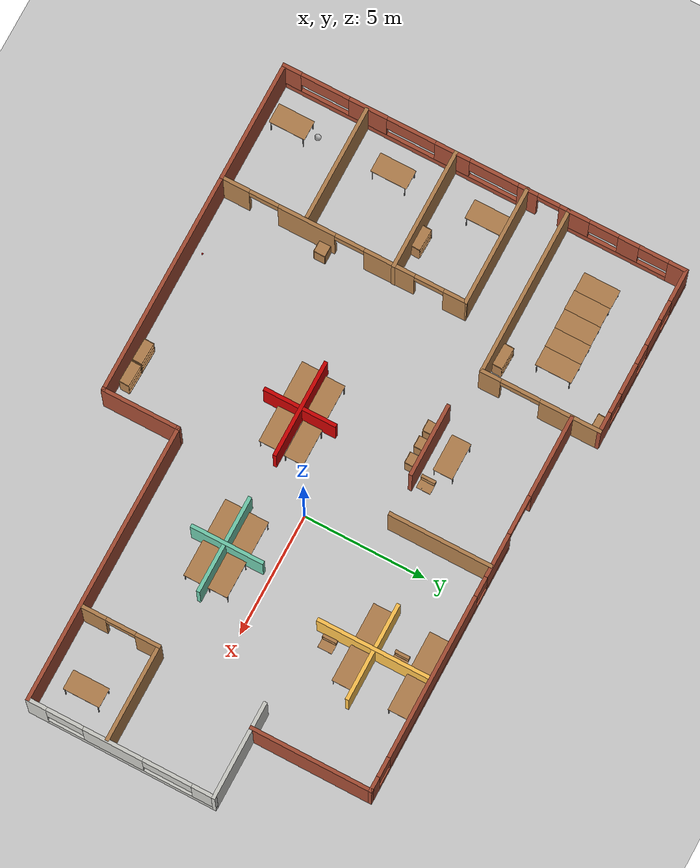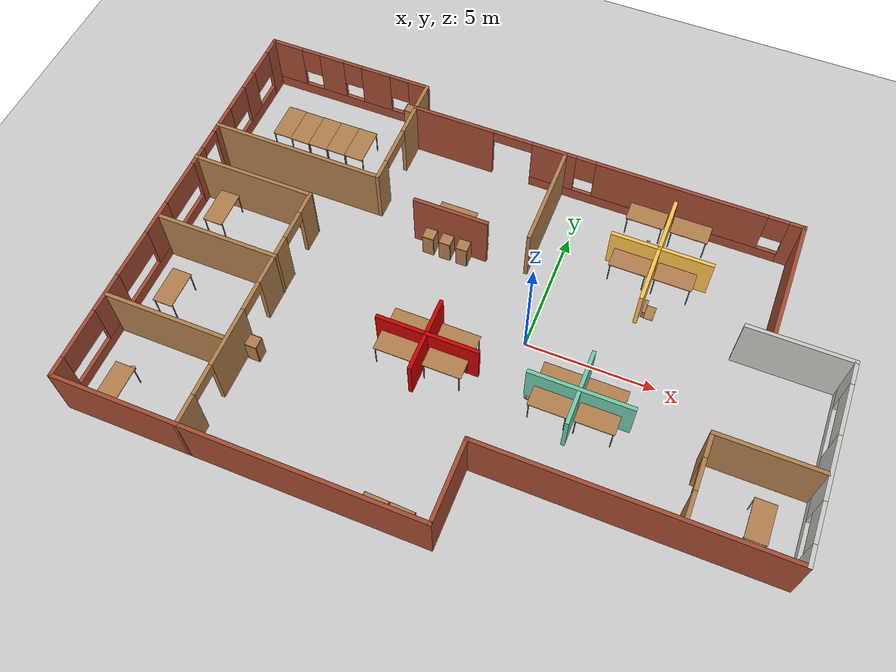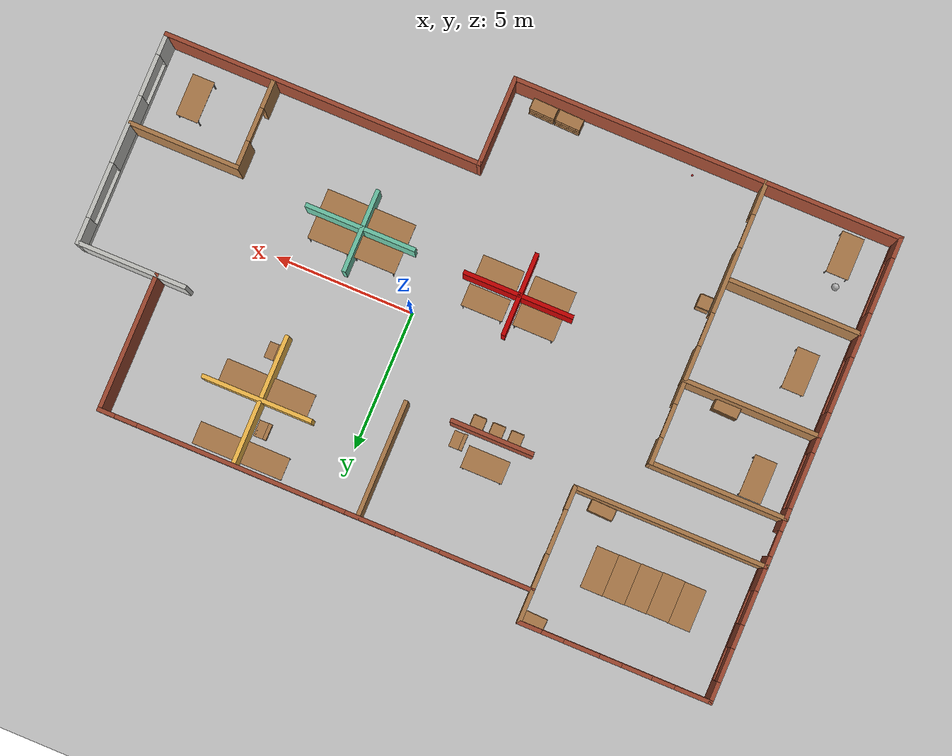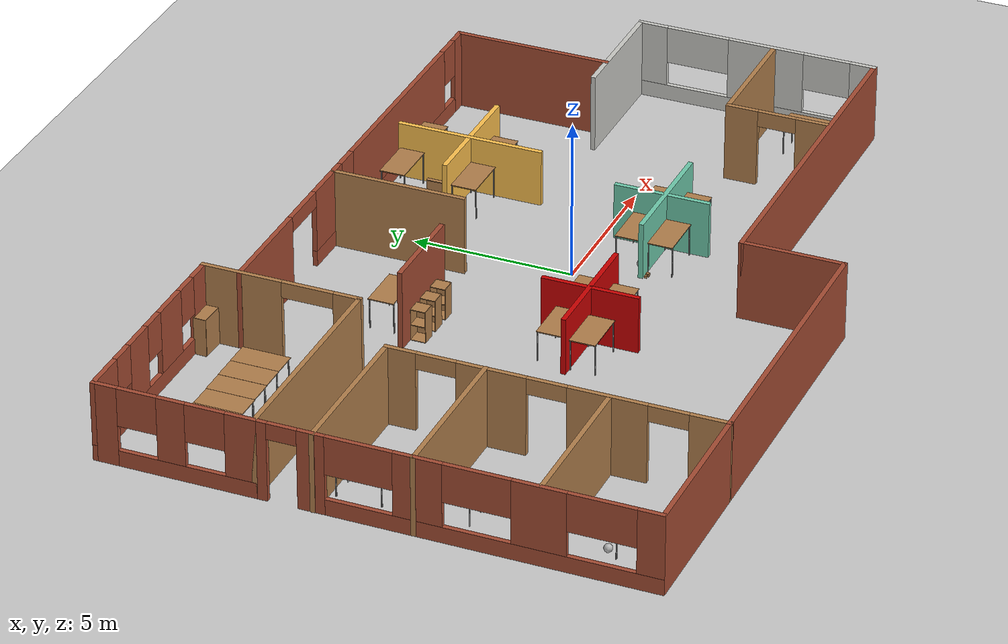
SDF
<sdf version="1.6">
 <world name="default">
  <light name="sun" type="directional">
   <pose>0 0 10 0 -0 0</pose>
   <diffuse>0.8 0.8 0.8 1</diffuse>
   <specular>0.2 0.2 0.2 1</specular>
   <attenuation>
    <range>1000</range>
    <constant>0.9</constant>
    <linear>0.01</linear>
    <quadratic>0.001</quadratic>
   </attenuation>
   <direction>-0.5 0.1 -0.9</direction>
   <spot><inner_angle>0</inner_angle><outer_angle>0</outer_angle><falloff>0</falloff></spot>
  </light>
  <model name="ground_plane">
   <static>1</static>
   <link name="link">
    <collision name="collision">
     <geometry><plane><normal>0 0 1</normal><size>100 100</size></plane></geometry>
     <surface>
      <contact><collide_bitmask>65535</collide_bitmask></contact>
      <friction><ode><mu>100</mu><mu2>50</mu2></ode></friction>
     </surface>
    </collision>
    <visual name="visual">
     <cast_shadows>0</cast_shadows>
     <geometry><plane><normal>0 0 1</normal><size>100 100</size></plane></geometry>
     <material>
      <script><uri>file://media/materials/scripts/gazebo.material</uri><name>Gazebo/Grey</name></script>
     </material>
    </visual>
   </link>
  </model>
  <gravity>0 0 -9.8</gravity>
  <magnetic_field>6e-06 2.3e-05 -4.2e-05</magnetic_field>
  <atmosphere type="adiabatic"/>
  <physics name="default_physics" default="0" type="ode">
   <max_step_size>0.001</max_step_size>
   <real_time_factor>1</real_time_factor>
   <real_time_update_rate>1000</real_time_update_rate>
  </physics>
  <scene><ambient>0.4 0.4 0.4 1</ambient><background>0.7 0.7 0.7 1</background><shadows>1</shadows></scene>
  <spherical_coordinates>
   <surface_model>EARTH_WGS84</surface_model>
   <latitude_deg>0</latitude_deg>
   <longitude_deg>0</longitude_deg>
   <elevation>0</elevation>
   <heading_deg>0</heading_deg>
  </spherical_coordinates>
  <model name="office">
   <pose>-1.5738 -0.08796 0 0 -0 0</pose>
   <link name="Wall_0">
    <pose>-12.6413 5.92507 0 0 -0 -1.5708</pose>
    <visual name="Wall_0_Visual_0">
     <pose>-2.10102 0 1.25 0 -0 0</pose>
     <geometry><box><size>0.79796 0.15 2.5</size></box></geometry>
     <material>
      <script><uri>file://media/materials/scripts/gazebo.material</uri><name>Gazebo/Bricks</name></script>
      <ambient>1 1 1 1</ambient>
     </material>
     <meta><layer>0</layer></meta>
    </visual>
    <collision name="Wall_0_Collision_0">
     <geometry><box><size>0.79796 0.15 2.5</size></box></geometry>
     <pose>-2.10102 0 1.25 0 -0 0</pose>
    </collision>
    <visual name="Wall_0_Visual_1">
     <pose>0.39898 0 0.25 0 -0 0</pose>
     <geometry><box><size>4.20204 0.15 0.5</size></box></geometry>
     <material>
      <script><uri>file://media/materials/scripts/gazebo.material</uri><name>Gazebo/Bricks</name></script>
      <ambient>1 1 1 1</ambient>
     </material>
     <meta><layer>0</layer></meta>
    </visual>
    <collision name="Wall_0_Collision_1">
     <geometry><box><size>4.20204 0.15 0.5</size></box></geometry>
     <pose>0.39898 0 0.25 0 -0 0</pose>
    </collision>
    <visual name="Wall_0_Visual_2">
     <pose>-0.076315 0 1.5 0 -0 0</pose>
     <geometry><box><size>0.851451 0.15 2</size></box></geometry>
     <material>
      <script><uri>file://media/materials/scripts/gazebo.material</uri><name>Gazebo/Bricks</name></script>
      <ambient>1 1 1 1</ambient>
     </material>
     <meta><layer>0</layer></meta>
    </visual>
    <collision name="Wall_0_Collision_2">
     <geometry><box><size>0.851451 0.15 2</size></box></geometry>
     <pose>-0.076315 0 1.5 0 -0 0</pose>
    </collision>
    <visual name="Wall_0_Visual_3">
     <pose>2.0247 0 1.5 0 -0 0</pose>
     <geometry><box><size>0.95059 0.15 2</size></box></geometry>
     <material>
      <script><uri>file://media/materials/scripts/gazebo.material</uri><name>Gazebo/Bricks</name></script>
      <ambient>1 1 1 1</ambient>
     </material>
     <meta><layer>0</layer></meta>
    </visual>
    <collision name="Wall_0_Collision_3">
     <geometry><box><size>0.95059 0.15 2</size></box></geometry>
     <pose>2.0247 0 1.5 0 -0 0</pose>
    </collision>
    <visual name="Wall_0_Visual_4">
     <pose>-1.10204 0 1.9 0 -0 0</pose>
     <geometry><box><size>1.2 0.15 1.2</size></box></geometry>
     <material>
      <script><uri>file://media/materials/scripts/gazebo.material</uri><name>Gazebo/Bricks</name></script>
      <ambient>1 1 1 1</ambient>
     </material>
     <meta><layer>0</layer></meta>
    </visual>
    <collision name="Wall_0_Collision_4">
     <geometry><box><size>1.2 0.15 1.2</size></box></geometry>
     <pose>-1.10204 0 1.9 0 -0 0</pose>
    </collision>
    <visual name="Wall_0_Visual_5">
     <pose>0.94941 0 1.9 0 -0 0</pose>
     <geometry><box><size>1.2 0.15 1.2</size></box></geometry>
     <material>
      <script><uri>file://media/materials/scripts/gazebo.material</uri><name>Gazebo/Bricks</name></script>
      <ambient>1 1 1 1</ambient>
     </material>
     <meta><layer>0</layer></meta>
    </visual>
    <collision name="Wall_0_Collision_5">
     <geometry><box><size>1.2 0.15 1.2</size></box></geometry>
     <pose>0.94941 0 1.9 0 -0 0</pose>
    </collision>
   </link>
   <link name="Wall_1">
    <collision name="Wall_1_Collision">
     <geometry><box><size>7 0.15 2.5</size></box></geometry>
     <pose>0 0 1.25 0 -0 0</pose>
    </collision>
    <visual name="Wall_1_Visual">
     <pose>0 0 1.25 0 -0 0</pose>
     <geometry><box><size>7 0.15 2.5</size></box></geometry>
     <material>
      <script><uri>file://media/materials/scripts/gazebo.material</uri><name>Gazebo/Wood</name></script>
      <ambient>1 1 1 1</ambient>
     </material>
     <meta><layer>0</layer></meta>
    </visual>
    <pose>-9.21631 3.50007 0 0 -0 0</pose>
   </link>
   <link name="Wall_12">
    <collision name="Wall_12_Collision">
     <geometry><box><size>4.75 0.15 2.5</size></box></geometry>
     <pose>0 0 1.25 0 -0 0</pose>
    </collision>
    <visual name="Wall_12_Visual">
     <pose>0 0 1.25 0 -0 0</pose>
     <geometry><box><size>4.75 0.15 2.5</size></box></geometry>
     <material>
      <script><uri>file://media/materials/scripts/gazebo.material</uri><name>Gazebo/Wood</name></script>
      <ambient>1 1 1 1</ambient>
     </material>
     <meta><layer>0</layer></meta>
    </visual>
    <pose>-10.2516 -4.8726 0 0 -0 0</pose>
   </link>
   <link name="Wall_19">
    <collision name="Wall_19_Collision">
     <geometry><box><size>5 0.15 2.5</size></box></geometry>
     <pose>0 0 1.25 0 -0 0</pose>
    </collision>
    <visual name="Wall_19_Visual">
     <pose>0 0 1.25 0 -0 0</pose>
     <geometry><box><size>5 0.15 2.5</size></box></geometry>
     <material>
      <script><uri>file://media/materials/scripts/gazebo.material</uri><name>Gazebo/Wood</name></script>
      <ambient>1 1 1 1</ambient>
     </material>
     <meta><layer>0</layer></meta>
    </visual>
    <pose>-10.2173 -1.19338 0 0 -0 0</pose>
   </link>
   <link name="Wall_2">
    <pose>-5.79131 5.92507 0 0 -0 1.5708</pose>
    <visual name="Wall_2_Visual_0">
     <pose>-2.06484 0 1.25 0 -0 0</pose>
     <geometry><box><size>0.870327 0.15 2.5</size></box></geometry>
     <material>
      <script><uri>file://media/materials/scripts/gazebo.material</uri><name>Gazebo/Wood</name></script>
      <ambient>1 1 1 1</ambient>
     </material>
     <meta><layer>0</layer></meta>
    </visual>
    <collision name="Wall_2_Collision_0">
     <geometry><box><size>0.870327 0.15 2.5</size></box></geometry>
     <pose>-2.06484 0 1.25 0 -0 0</pose>
    </collision>
    <visual name="Wall_2_Visual_1">
     <pose>1.23516 0 1.25 0 -0 0</pose>
     <geometry><box><size>2.52967 0.15 2.5</size></box></geometry>
     <material>
      <script><uri>file://media/materials/scripts/gazebo.material</uri><name>Gazebo/Wood</name></script>
      <ambient>1 1 1 1</ambient>
     </material>
     <meta><layer>0</layer></meta>
    </visual>
    <collision name="Wall_2_Collision_1">
     <geometry><box><size>2.52967 0.15 2.5</size></box></geometry>
     <pose>1.23516 0 1.25 0 -0 0</pose>
    </collision>
    <visual name="Wall_2_Visual_2">
     <pose>-0.829673 0 2.25 0 -0 0</pose>
     <geometry><box><size>1.6 0.15 0.5</size></box></geometry>
     <material>
      <script><uri>file://media/materials/scripts/gazebo.material</uri><name>Gazebo/Wood</name></script>
      <ambient>1 1 1 1</ambient>
     </material>
     <meta><layer>0</layer></meta>
    </visual>
    <collision name="Wall_2_Collision_2">
     <geometry><box><size>1.6 0.15 0.5</size></box></geometry>
     <pose>-0.829673 0 2.25 0 -0 0</pose>
    </collision>
   </link>
   <link name="Wall_21">
    <collision name="Wall_21_Collision">
     <geometry><box><size>9.25 0.15 2.5</size></box></geometry>
     <pose>0 0 1.25 0 -0 0</pose>
    </collision>
    <visual name="Wall_21_Visual">
     <pose>0 0 1.25 0 -0 0</pose>
     <geometry><box><size>9.25 0.15 2.5</size></box></geometry>
     <material>
      <script><uri>file://media/materials/scripts/gazebo.material</uri><name>Gazebo/Bricks</name></script>
      <ambient>1 1 1 1</ambient>
     </material>
     <meta><layer>0</layer></meta>
    </visual>
    <pose>-3.24131 -8.34993 0 0 -0 0</pose>
   </link>
   <link name="Wall_22">
    <collision name="Wall_22_Collision">
     <geometry><box><size>3.25 0.15 2.5</size></box></geometry>
     <pose>0 0 1.25 0 -0 0</pose>
    </collision>
    <visual name="Wall_22_Visual">
     <pose>0 0 1.25 0 -0 0</pose>
     <geometry><box><size>3.25 0.15 2.5</size></box></geometry>
     <material>
      <script><uri>file://media/materials/scripts/gazebo.material</uri><name>Gazebo/Bricks</name></script>
      <ambient>1 1 1 1</ambient>
     </material>
     <meta><layer>0</layer></meta>
    </visual>
    <pose>1.30869 -6.79992 0 0 -0 1.5708</pose>
   </link>
   <link name="Wall_23">
    <collision name="Wall_23_Collision">
     <geometry><box><size>11.5 0.15 2.5</size></box></geometry>
     <pose>0 0 1.25 0 -0 0</pose>
    </collision>
    <visual name="Wall_23_Visual">
     <pose>0 0 1.25 0 -0 0</pose>
     <geometry><box><size>11.5 0.15 2.5</size></box></geometry>
     <material>
      <script><uri>file://media/materials/scripts/gazebo.material</uri><name>Gazebo/Bricks</name></script>
      <ambient>1 1 1 1</ambient>
     </material>
     <meta><layer>0</layer></meta>
    </visual>
    <pose>6.98369 -5.24993 0 0 -0 0</pose>
   </link>
   <link name="Wall_24">
    <pose>12.6587 -1.44992 0 0 -0 1.5708</pose>
    <visual name="Wall_24_Visual_0">
     <pose>-3.45904 0 1.25 0 -0 0</pose>
     <geometry><box><size>0.831925 0.15 2.5</size></box></geometry>
     <material>
      <script><uri>file://media/materials/scripts/gazebo.material</uri><name>Gazebo/CeilingTiled</name></script>
      <ambient>1 1 1 1</ambient>
     </material>
     <meta><layer>0</layer></meta>
    </visual>
    <collision name="Wall_24_Collision_0">
     <geometry><box><size>0.831925 0.15 2.5</size></box></geometry>
     <pose>-3.45904 0 1.25 0 -0 0</pose>
    </collision>
    <visual name="Wall_24_Visual_1">
     <pose>0.415962 0 0.25 0 -0 0</pose>
     <geometry><box><size>6.91807 0.15 0.5</size></box></geometry>
     <material>
      <script><uri>file://media/materials/scripts/gazebo.material</uri><name>Gazebo/CeilingTiled</name></script>
      <ambient>1 1 1 1</ambient>
     </material>
     <meta><layer>0</layer></meta>
    </visual>
    <collision name="Wall_24_Collision_1">
     <geometry><box><size>6.91807 0.15 0.5</size></box></geometry>
     <pose>0.415962 0 0.25 0 -0 0</pose>
    </collision>
    <visual name="Wall_24_Visual_2">
     <pose>-0.320599 0 1.5 0 -0 0</pose>
     <geometry><box><size>2.44495 0.15 2</size></box></geometry>
     <material>
      <script><uri>file://media/materials/scripts/gazebo.material</uri><name>Gazebo/CeilingTiled</name></script>
      <ambient>1 1 1 1</ambient>
     </material>
     <meta><layer>0</layer></meta>
    </visual>
    <collision name="Wall_24_Collision_2">
     <geometry><box><size>2.44495 0.15 2</size></box></geometry>
     <pose>-0.320599 0 1.5 0 -0 0</pose>
    </collision>
    <visual name="Wall_24_Visual_3">
     <pose>3.38844 0 1.5 0 -0 0</pose>
     <geometry><box><size>0.973122 0.15 2</size></box></geometry>
     <material>
      <script><uri>file://media/materials/scripts/gazebo.material</uri><name>Gazebo/CeilingTiled</name></script>
      <ambient>1 1 1 1</ambient>
     </material>
     <meta><layer>0</layer></meta>
    </visual>
    <collision name="Wall_24_Collision_3">
     <geometry><box><size>0.973122 0.15 2</size></box></geometry>
     <pose>3.38844 0 1.5 0 -0 0</pose>
    </collision>
    <visual name="Wall_24_Visual_4">
     <pose>-2.29307 0 1.9 0 -0 0</pose>
     <geometry><box><size>1.5 0.15 1.2</size></box></geometry>
     <material>
      <script><uri>file://media/materials/scripts/gazebo.material</uri><name>Gazebo/CeilingTiled</name></script>
      <ambient>1 1 1 1</ambient>
     </material>
     <meta><layer>0</layer></meta>
    </visual>
    <collision name="Wall_24_Collision_4">
     <geometry><box><size>1.5 0.15 1.2</size></box></geometry>
     <pose>-2.29307 0 1.9 0 -0 0</pose>
    </collision>
    <visual name="Wall_24_Visual_5">
     <pose>1.90188 0 1.9 0 -0 0</pose>
     <geometry><box><size>2 0.15 1.2</size></box></geometry>
     <material>
      <script><uri>file://media/materials/scripts/gazebo.material</uri><name>Gazebo/CeilingTiled</name></script>
      <ambient>1 1 1 1</ambient>
     </material>
     <meta><layer>0</layer></meta>
    </visual>
    <collision name="Wall_24_Collision_5">
     <geometry><box><size>2 0.15 1.2</size></box></geometry>
     <pose>1.90188 0 1.9 0 -0 0</pose>
    </collision>
   </link>
   <link name="Wall_25">
    <collision name="Wall_25_Collision">
     <geometry><box><size>4 0.15 2.5</size></box></geometry>
     <pose>0 0 1.25 0 -0 0</pose>
    </collision>
    <visual name="Wall_25_Visual">
     <pose>0 0 1.25 0 -0 0</pose>
     <geometry><box><size>4 0.15 2.5</size></box></geometry>
     <material>
      <script><uri>file://media/materials/scripts/gazebo.material</uri><name>Gazebo/CeilingTiled</name></script>
      <ambient>1 1 1 1</ambient>
     </material>
     <meta><layer>0</layer></meta>
    </visual>
    <pose>10.7337 2.35007 0 0 -0 3.14159</pose>
   </link>
   <link name="Wall_27">
    <collision name="Wall_27_Collision">
     <geometry><box><size>4 0.15 2.5</size></box></geometry>
     <pose>0 0 1.25 0 -0 0</pose>
    </collision>
    <visual name="Wall_27_Visual">
     <pose>0 0 1.25 0 -0 0</pose>
     <geometry><box><size>4 0.15 2.5</size></box></geometry>
     <material>
      <script><uri>file://media/materials/scripts/gazebo.material</uri><name>Gazebo/Wood</name></script>
      <ambient>1 1 1 1</ambient>
     </material>
     <meta><layer>0</layer></meta>
    </visual>
    <pose>10.6699 -2.02159 0 0 -0 3.14159</pose>
   </link>
   <link name="Wall_28">
    <pose>8.74488 -3.57159 0 0 -0 -1.5708</pose>
    <visual name="Wall_28_Visual_0">
     <pose>-1.11107 0 1.25 0 -0 0</pose>
     <geometry><box><size>1.02786 0.15 2.5</size></box></geometry>
     <material>
      <script><uri>file://media/materials/scripts/gazebo.material</uri><name>Gazebo/Wood</name></script>
      <ambient>1 1 1 1</ambient>
     </material>
     <meta><layer>0</layer></meta>
    </visual>
    <collision name="Wall_28_Collision_0">
     <geometry><box><size>1.02786 0.15 2.5</size></box></geometry>
     <pose>-1.11107 0 1.25 0 -0 0</pose>
    </collision>
    <visual name="Wall_28_Visual_1">
     <pose>1.11393 0 1.25 0 -0 0</pose>
     <geometry><box><size>1.02214 0.15 2.5</size></box></geometry>
     <material>
      <script><uri>file://media/materials/scripts/gazebo.material</uri><name>Gazebo/Wood</name></script>
      <ambient>1 1 1 1</ambient>
     </material>
     <meta><layer>0</layer></meta>
    </visual>
    <collision name="Wall_28_Collision_1">
     <geometry><box><size>1.02214 0.15 2.5</size></box></geometry>
     <pose>1.11393 0 1.25 0 -0 0</pose>
    </collision>
    <visual name="Wall_28_Visual_2">
     <pose>0.002857 0 2.25 0 -0 0</pose>
     <geometry><box><size>1.2 0.15 0.5</size></box></geometry>
     <material>
      <script><uri>file://media/materials/scripts/gazebo.material</uri><name>Gazebo/Wood</name></script>
      <ambient>1 1 1 1</ambient>
     </material>
     <meta><layer>0</layer></meta>
    </visual>
    <collision name="Wall_28_Collision_2">
     <geometry><box><size>1.2 0.15 0.5</size></box></geometry>
     <pose>0.002857 0 2.25 0 -0 0</pose>
    </collision>
   </link>
   <link name="Wall_3">
    <pose>-9.21631 8.35008 0 0 -0 3.14159</pose>
    <visual name="Wall_3_Visual_0">
     <pose>-3.0632 0 1.25 0 -0 0</pose>
     <geometry><box><size>0.873598 0.15 2.5</size></box></geometry>
     <material>
      <script><uri>file://media/materials/scripts/gazebo.material</uri><name>Gazebo/Bricks</name></script>
      <ambient>1 1 1 1</ambient>
     </material>
     <meta><layer>0</layer></meta>
    </visual>
    <collision name="Wall_3_Collision_0">
     <geometry><box><size>0.873598 0.15 2.5</size></box></geometry>
     <pose>-3.0632 0 1.25 0 -0 0</pose>
    </collision>
    <visual name="Wall_3_Visual_1">
     <pose>0.436799 0 0.25 0 -0 0</pose>
     <geometry><box><size>6.1264 0.15 0.5</size></box></geometry>
     <material>
      <script><uri>file://media/materials/scripts/gazebo.material</uri><name>Gazebo/Bricks</name></script>
      <ambient>1 1 1 1</ambient>
     </material>
     <meta><layer>0</layer></meta>
    </visual>
    <collision name="Wall_3_Collision_1">
     <geometry><box><size>6.1264 0.15 0.5</size></box></geometry>
     <pose>0.436799 0 0.25 0 -0 0</pose>
    </collision>
    <visual name="Wall_3_Visual_2">
     <pose>-1.18753 0 1.5 0 -0 0</pose>
     <geometry><box><size>1.27775 0.15 2</size></box></geometry>
     <material>
      <script><uri>file://media/materials/scripts/gazebo.material</uri><name>Gazebo/Bricks</name></script>
      <ambient>1 1 1 1</ambient>
     </material>
     <meta><layer>0</layer></meta>
    </visual>
    <collision name="Wall_3_Collision_2">
     <geometry><box><size>1.27775 0.15 2</size></box></geometry>
     <pose>-1.18753 0 1.5 0 -0 0</pose>
    </collision>
    <visual name="Wall_3_Visual_3">
     <pose>0.791597 0 1.5 0 -0 0</pose>
     <geometry><box><size>1.0805 0.15 2</size></box></geometry>
     <material>
      <script><uri>file://media/materials/scripts/gazebo.material</uri><name>Gazebo/Bricks</name></script>
      <ambient>1 1 1 1</ambient>
     </material>
     <meta><layer>0</layer></meta>
    </visual>
    <collision name="Wall_3_Collision_3">
     <geometry><box><size>1.0805 0.15 2</size></box></geometry>
     <pose>0.791597 0 1.5 0 -0 0</pose>
    </collision>
    <visual name="Wall_3_Visual_4">
     <pose>2.81592 0 1.5 0 -0 0</pose>
     <geometry><box><size>1.36816 0.15 2</size></box></geometry>
     <material>
      <script><uri>file://media/materials/scripts/gazebo.material</uri><name>Gazebo/Bricks</name></script>
      <ambient>1 1 1 1</ambient>
     </material>
     <meta><layer>0</layer></meta>
    </visual>
    <collision name="Wall_3_Collision_4">
     <geometry><box><size>1.36816 0.15 2</size></box></geometry>
     <pose>2.81592 0 1.5 0 -0 0</pose>
    </collision>
    <visual name="Wall_3_Visual_5">
     <pose>-2.2264 0 1.9 0 -0 0</pose>
     <geometry><box><size>0.8 0.15 1.2</size></box></geometry>
     <material>
      <script><uri>file://media/materials/scripts/gazebo.material</uri><name>Gazebo/Bricks</name></script>
      <ambient>1 1 1 1</ambient>
     </material>
     <meta><layer>0</layer></meta>
    </visual>
    <collision name="Wall_3_Collision_5">
     <geometry><box><size>0.8 0.15 1.2</size></box></geometry>
     <pose>-2.2264 0 1.9 0 -0 0</pose>
    </collision>
    <visual name="Wall_3_Visual_6">
     <pose>-0.148651 0 1.9 0 -0 0</pose>
     <geometry><box><size>0.8 0.15 1.2</size></box></geometry>
     <material>
      <script><uri>file://media/materials/scripts/gazebo.material</uri><name>Gazebo/Bricks</name></script>
      <ambient>1 1 1 1</ambient>
     </material>
     <meta><layer>0</layer></meta>
    </visual>
    <collision name="Wall_3_Collision_6">
     <geometry><box><size>0.8 0.15 1.2</size></box></geometry>
     <pose>-0.148651 0 1.9 0 -0 0</pose>
    </collision>
    <visual name="Wall_3_Visual_7">
     <pose>1.73185 0 1.9 0 -0 0</pose>
     <geometry><box><size>0.8 0.15 1.2</size></box></geometry>
     <material>
      <script><uri>file://media/materials/scripts/gazebo.material</uri><name>Gazebo/Bricks</name></script>
      <ambient>1 1 1 1</ambient>
     </material>
     <meta><layer>0</layer></meta>
    </visual>
    <collision name="Wall_3_Collision_7">
     <geometry><box><size>0.8 0.15 1.2</size></box></geometry>
     <pose>1.73185 0 1.9 0 -0 0</pose>
    </collision>
   </link>
   <link name="Wall_30">
    <collision name="Wall_30_Collision">
     <geometry><box><size>5 0.15 2.5</size></box></geometry>
     <pose>0 0 1.25 0 -0 0</pose>
    </collision>
    <visual name="Wall_30_Visual">
     <pose>0 0 1.25 0 -0 0</pose>
     <geometry><box><size>5 0.15 2.5</size></box></geometry>
     <material>
      <script><uri>file://media/materials/scripts/gazebo.material</uri><name>Gazebo/Bricks</name></script>
      <ambient>1 1 1 1</ambient>
     </material>
     <meta><layer>0</layer></meta>
    </visual>
    <pose>9.80511 4.78099 0 0 -0 1.5708</pose>
   </link>
   <link name="Wall_31">
    <pose>2.00511 7.20599 0 0 -0 3.14159</pose>
    <visual name="Wall_31_Visual_0">
     <pose>-7.55649 0 1.25 0 -0 0</pose>
     <geometry><box><size>0.637024 0.15 2.5</size></box></geometry>
     <material>
      <script><uri>file://media/materials/scripts/gazebo.material</uri><name>Gazebo/Bricks</name></script>
      <ambient>1 1 1 1</ambient>
     </material>
     <meta><layer>0</layer></meta>
    </visual>
    <collision name="Wall_31_Collision_0">
     <geometry><box><size>0.637024 0.15 2.5</size></box></geometry>
     <pose>-7.55649 0 1.25 0 -0 0</pose>
    </collision>
    <visual name="Wall_31_Visual_1">
     <pose>6.16793 0 1.25 0 -0 0</pose>
     <geometry><box><size>3.41413 0.15 2.5</size></box></geometry>
     <material>
      <script><uri>file://media/materials/scripts/gazebo.material</uri><name>Gazebo/Bricks</name></script>
      <ambient>1 1 1 1</ambient>
     </material>
     <meta><layer>0</layer></meta>
    </visual>
    <collision name="Wall_31_Collision_1">
     <geometry><box><size>3.41413 0.15 2.5</size></box></geometry>
     <pose>6.16793 0 1.25 0 -0 0</pose>
    </collision>
    <visual name="Wall_31_Visual_2">
     <pose>-2.18855 0 0.25 0 -0 0</pose>
     <geometry><box><size>10.0988 0.15 0.5</size></box></geometry>
     <material>
      <script><uri>file://media/materials/scripts/gazebo.material</uri><name>Gazebo/Bricks</name></script>
      <ambient>1 1 1 1</ambient>
     </material>
     <meta><layer>0</layer></meta>
    </visual>
    <collision name="Wall_31_Collision_2">
     <geometry><box><size>10.0988 0.15 0.5</size></box></geometry>
     <pose>-2.18855 0 0.25 0 -0 0</pose>
    </collision>
    <visual name="Wall_31_Visual_3">
     <pose>-3.09013 0 1.5 0 -0 0</pose>
     <geometry><box><size>6.69569 0.15 2</size></box></geometry>
     <material>
      <script><uri>file://media/materials/scripts/gazebo.material</uri><name>Gazebo/Bricks</name></script>
      <ambient>1 1 1 1</ambient>
     </material>
     <meta><layer>0</layer></meta>
    </visual>
    <collision name="Wall_31_Collision_3">
     <geometry><box><size>6.69569 0.15 2</size></box></geometry>
     <pose>-3.09013 0 1.5 0 -0 0</pose>
    </collision>
    <visual name="Wall_31_Visual_4">
     <pose>1.95929 0 1.5 0 -0 0</pose>
     <geometry><box><size>1.80316 0.15 2</size></box></geometry>
     <material>
      <script><uri>file://media/materials/scripts/gazebo.material</uri><name>Gazebo/Bricks</name></script>
      <ambient>1 1 1 1</ambient>
     </material>
     <meta><layer>0</layer></meta>
    </visual>
    <collision name="Wall_31_Collision_4">
     <geometry><box><size>1.80316 0.15 2</size></box></geometry>
     <pose>1.95929 0 1.5 0 -0 0</pose>
    </collision>
    <visual name="Wall_31_Visual_5">
     <pose>-6.83798 0 1.9 0 -0 0</pose>
     <geometry><box><size>0.8 0.15 1.2</size></box></geometry>
     <material>
      <script><uri>file://media/materials/scripts/gazebo.material</uri><name>Gazebo/Bricks</name></script>
      <ambient>1 1 1 1</ambient>
     </material>
     <meta><layer>0</layer></meta>
    </visual>
    <collision name="Wall_31_Collision_5">
     <geometry><box><size>0.8 0.15 1.2</size></box></geometry>
     <pose>-6.83798 0 1.9 0 -0 0</pose>
    </collision>
    <visual name="Wall_31_Visual_6">
     <pose>0.657708 0 1.9 0 -0 0</pose>
     <geometry><box><size>0.8 0.15 1.2</size></box></geometry>
     <material>
      <script><uri>file://media/materials/scripts/gazebo.material</uri><name>Gazebo/Bricks</name></script>
      <ambient>1 1 1 1</ambient>
     </material>
     <meta><layer>0</layer></meta>
    </visual>
    <collision name="Wall_31_Collision_6">
     <geometry><box><size>0.8 0.15 1.2</size></box></geometry>
     <pose>0.657708 0 1.9 0 -0 0</pose>
    </collision>
    <visual name="Wall_31_Visual_7">
     <pose>3.66087 0 2.25 0 -0 0</pose>
     <geometry><box><size>1.6 0.15 0.5</size></box></geometry>
     <material>
      <script><uri>file://media/materials/scripts/gazebo.material</uri><name>Gazebo/Bricks</name></script>
      <ambient>1 1 1 1</ambient>
     </material>
     <meta><layer>0</layer></meta>
    </visual>
    <collision name="Wall_31_Collision_7">
     <geometry><box><size>1.6 0.15 0.5</size></box></geometry>
     <pose>3.66087 0 2.25 0 -0 0</pose>
    </collision>
   </link>
   <link name="Wall_33">
    <collision name="Wall_33_Collision">
     <geometry><box><size>4.25 0.15 2.5</size></box></geometry>
     <pose>0 0 1.25 0 -0 0</pose>
    </collision>
    <visual name="Wall_33_Visual">
     <pose>0 0 1.25 0 -0 0</pose>
     <geometry><box><size>4.25 0.15 2.5</size></box></geometry>
     <material>
      <script><uri>file://media/materials/scripts/gazebo.material</uri><name>Gazebo/Wood</name></script>
      <ambient>1 1 1 1</ambient>
     </material>
     <meta><layer>0</layer></meta>
    </visual>
    <pose>0.500764 5.12338 0 0 -0 -1.5708</pose>
   </link>
   <link name="Wall_35">
    <collision name="Wall_35_Collision">
     <geometry><box><size>4.75 0.15 1.8</size></box></geometry>
     <pose>0 0 0.9 0 -0 0</pose>
    </collision>
    <visual name="Wall_35_Visual">
     <pose>0 0 0.9 0 -0 0</pose>
     <geometry><box><size>4.75 0.15 1.8</size></box></geometry>
     <material>
      <script><uri>file://media/materials/scripts/gazebo.material</uri><name>Gazebo/Grey</name></script>
      <ambient>1 0.764706 0.305882 1</ambient>
     </material>
     <meta><layer>0</layer></meta>
    </visual>
    <pose>5.05557 4.85856 0 0 -0 -1.5708</pose>
   </link>
   <link name="Wall_37">
    <collision name="Wall_37_Collision">
     <geometry><box><size>4 0.15 1.8</size></box></geometry>
     <pose>0 0 0.9 0 -0 0</pose>
    </collision>
    <visual name="Wall_37_Visual">
     <pose>0 0 0.9 0 -0 0</pose>
     <geometry><box><size>4 0.15 1.8</size></box></geometry>
     <material>
      <script><uri>file://media/materials/scripts/gazebo.material</uri><name>Gazebo/Grey</name></script>
      <ambient>1 0.764706 0.305882 1</ambient>
     </material>
     <meta><layer>0</layer></meta>
    </visual>
    <pose>5.17957 4.83056 0 0 -0 0</pose>
   </link>
   <link name="Wall_39">
    <collision name="Wall_39_Collision">
     <geometry><box><size>3 0.15 2.5</size></box></geometry>
     <pose>0 0 1.25 0 -0 0</pose>
    </collision>
    <visual name="Wall_39_Visual">
     <pose>0 0 1.25 0 -0 0</pose>
     <geometry><box><size>3 0.15 2.5</size></box></geometry>
     <material>
      <script><uri>file://media/materials/scripts/gazebo.material</uri><name>Gazebo/Bricks</name></script>
      <ambient>1 1 1 1</ambient>
     </material>
     <meta><layer>0</layer></meta>
    </visual>
    <pose>-2.60246 3.02942 0 0 -0 3.14159</pose>
   </link>
   <link name="Wall_41">
    <collision name="Wall_41_Collision">
     <geometry><box><size>4 0.15 1.8</size></box></geometry>
     <pose>0 0 0.9 0 -0 0</pose>
    </collision>
    <visual name="Wall_41_Visual">
     <pose>0 0 0.9 0 -0 0</pose>
     <geometry><box><size>4 0.15 1.8</size></box></geometry>
     <material>
      <script><uri>file://media/materials/scripts/gazebo.material</uri><name>Gazebo/Grey</name></script>
      <ambient>0.8 0 0 1</ambient>
     </material>
     <meta><layer>0</layer></meta>
    </visual>
    <pose>-1.56643 -1.75744 0 0 -0 0</pose>
   </link>
   <link name="Wall_43">
    <collision name="Wall_43_Collision">
     <geometry><box><size>3 0.15 1.8</size></box></geometry>
     <pose>0 0 0.9 0 -0 0</pose>
    </collision>
    <visual name="Wall_43_Visual">
     <pose>0 0 0.9 0 -0 0</pose>
     <geometry><box><size>3 0.15 1.8</size></box></geometry>
     <material>
      <script><uri>file://media/materials/scripts/gazebo.material</uri><name>Gazebo/Grey</name></script>
      <ambient>0.8 0 0 1</ambient>
     </material>
     <meta><layer>0</layer></meta>
    </visual>
    <pose>-1.61128 -1.78879 0 0 -0 -1.5708</pose>
   </link>
   <link name="Wall_45">
    <collision name="Wall_45_Collision">
     <geometry><box><size>4 0.15 1.8</size></box></geometry>
     <pose>0 0 0.9 0 -0 0</pose>
    </collision>
    <visual name="Wall_45_Visual">
     <pose>0 0 0.9 0 -0 0</pose>
     <geometry><box><size>4 0.15 1.8</size></box></geometry>
     <material>
      <script><uri>file://media/materials/scripts/gazebo.material</uri><name>Gazebo/Grey</name></script>
      <ambient>0.435294 0.796078 0.67451 1</ambient>
     </material>
     <meta><layer>0</layer></meta>
    </visual>
    <pose>4.20657 -1.80944 0 0 -0 0</pose>
   </link>
   <link name="Wall_47">
    <collision name="Wall_47_Collision">
     <geometry><box><size>3 0.15 1.8</size></box></geometry>
     <pose>0 0 0.9 0 -0 0</pose>
    </collision>
    <visual name="Wall_47_Visual">
     <pose>0 0 0.9 0 -0 0</pose>
     <geometry><box><size>3 0.15 1.8</size></box></geometry>
     <material>
      <script><uri>file://media/materials/scripts/gazebo.material</uri><name>Gazebo/Grey</name></script>
      <ambient>0.435294 0.796078 0.67451 1</ambient>
     </material>
     <meta><layer>0</layer></meta>
    </visual>
    <pose>4.14857 -1.70944 0 0 -0 -1.5708</pose>
   </link>
   <link name="Wall_5">
    <pose>-12.6413 -2.42492 0 0 -0 -1.5708</pose>
    <visual name="Wall_5_Visual_0">
     <pose>-5.7769 0 1.25 0 -0 0</pose>
     <geometry><box><size>0.446198 0.15 2.5</size></box></geometry>
     <material>
      <script><uri>file://media/materials/scripts/gazebo.material</uri><name>Gazebo/Bricks</name></script>
      <ambient>1 1 1 1</ambient>
     </material>
     <meta><layer>0</layer></meta>
    </visual>
    <collision name="Wall_5_Collision_0">
     <geometry><box><size>0.446198 0.15 2.5</size></box></geometry>
     <pose>-5.7769 0 1.25 0 -0 0</pose>
    </collision>
    <visual name="Wall_5_Visual_1">
     <pose>-4.24561 0 1.25 0 -0 0</pose>
     <geometry><box><size>0.816375 0.15 2.5</size></box></geometry>
     <material>
      <script><uri>file://media/materials/scripts/gazebo.material</uri><name>Gazebo/Bricks</name></script>
      <ambient>1 1 1 1</ambient>
     </material>
     <meta><layer>0</layer></meta>
    </visual>
    <collision name="Wall_5_Collision_1">
     <geometry><box><size>0.816375 0.15 2.5</size></box></geometry>
     <pose>-4.24561 0 1.25 0 -0 0</pose>
    </collision>
    <visual name="Wall_5_Visual_2">
     <pose>1.08129 0 0.25 0 -0 0</pose>
     <geometry><box><size>9.83743 0.15 0.5</size></box></geometry>
     <material>
      <script><uri>file://media/materials/scripts/gazebo.material</uri><name>Gazebo/Bricks</name></script>
      <ambient>1 1 1 1</ambient>
     </material>
     <meta><layer>0</layer></meta>
    </visual>
    <collision name="Wall_5_Collision_2">
     <geometry><box><size>9.83743 0.15 0.5</size></box></geometry>
     <pose>1.08129 0 0.25 0 -0 0</pose>
    </collision>
    <visual name="Wall_5_Visual_3">
     <pose>-1.11473 0 1.5 0 -0 0</pose>
     <geometry><box><size>1.44538 0.15 2</size></box></geometry>
     <material>
      <script><uri>file://media/materials/scripts/gazebo.material</uri><name>Gazebo/Bricks</name></script>
      <ambient>1 1 1 1</ambient>
     </material>
     <meta><layer>0</layer></meta>
    </visual>
    <collision name="Wall_5_Collision_3">
     <geometry><box><size>1.44538 0.15 2</size></box></geometry>
     <pose>-1.11473 0 1.5 0 -0 0</pose>
    </collision>
    <visual name="Wall_5_Visual_4">
     <pose>2.40298 0 1.5 0 -0 0</pose>
     <geometry><box><size>1.59004 0.15 2</size></box></geometry>
     <material>
      <script><uri>file://media/materials/scripts/gazebo.material</uri><name>Gazebo/Bricks</name></script>
      <ambient>1 1 1 1</ambient>
     </material>
     <meta><layer>0</layer></meta>
    </visual>
    <collision name="Wall_5_Collision_4">
     <geometry><box><size>1.59004 0.15 2</size></box></geometry>
     <pose>2.40298 0 1.5 0 -0 0</pose>
    </collision>
    <visual name="Wall_5_Visual_5">
     <pose>5.599 0 1.5 0 -0 0</pose>
     <geometry><box><size>0.802003 0.15 2</size></box></geometry>
     <material>
      <script><uri>file://media/materials/scripts/gazebo.material</uri><name>Gazebo/Bricks</name></script>
      <ambient>1 1 1 1</ambient>
     </material>
     <meta><layer>0</layer></meta>
    </visual>
    <collision name="Wall_5_Collision_5">
     <geometry><box><size>0.802003 0.15 2</size></box></geometry>
     <pose>5.599 0 1.5 0 -0 0</pose>
    </collision>
    <visual name="Wall_5_Visual_6">
     <pose>-2.83743 0 1.9 0 -0 0</pose>
     <geometry><box><size>2 0.15 1.2</size></box></geometry>
     <material>
      <script><uri>file://media/materials/scripts/gazebo.material</uri><name>Gazebo/Bricks</name></script>
      <ambient>1 1 1 1</ambient>
     </material>
     <meta><layer>0</layer></meta>
    </visual>
    <collision name="Wall_5_Collision_6">
     <geometry><box><size>2 0.15 1.2</size></box></geometry>
     <pose>-2.83743 0 1.9 0 -0 0</pose>
    </collision>
    <visual name="Wall_5_Visual_7">
     <pose>0.607958 0 1.9 0 -0 0</pose>
     <geometry><box><size>2 0.15 1.2</size></box></geometry>
     <material>
      <script><uri>file://media/materials/scripts/gazebo.material</uri><name>Gazebo/Bricks</name></script>
      <ambient>1 1 1 1</ambient>
     </material>
     <meta><layer>0</layer></meta>
    </visual>
    <collision name="Wall_5_Collision_7">
     <geometry><box><size>2 0.15 1.2</size></box></geometry>
     <pose>0.607958 0 1.9 0 -0 0</pose>
    </collision>
    <visual name="Wall_5_Visual_8">
     <pose>4.198 0 1.9 0 -0 0</pose>
     <geometry><box><size>2 0.15 1.2</size></box></geometry>
     <material>
      <script><uri>file://media/materials/scripts/gazebo.material</uri><name>Gazebo/Bricks</name></script>
      <ambient>1 1 1 1</ambient>
     </material>
     <meta><layer>0</layer></meta>
    </visual>
    <collision name="Wall_5_Collision_8">
     <geometry><box><size>2 0.15 1.2</size></box></geometry>
     <pose>4.198 0 1.9 0 -0 0</pose>
    </collision>
    <visual name="Wall_5_Visual_9">
     <pose>-5.1038 0 2.25 0 -0 0</pose>
     <geometry><box><size>0.9 0.15 0.5</size></box></geometry>
     <material>
      <script><uri>file://media/materials/scripts/gazebo.material</uri><name>Gazebo/Bricks</name></script>
      <ambient>1 1 1 1</ambient>
     </material>
     <meta><layer>0</layer></meta>
    </visual>
    <collision name="Wall_5_Collision_9">
     <geometry><box><size>0.9 0.15 0.5</size></box></geometry>
     <pose>-5.1038 0 2.25 0 -0 0</pose>
    </collision>
   </link>
   <link name="Wall_6">
    <collision name="Wall_6_Collision">
     <geometry><box><size>5 0.15 2.5</size></box></geometry>
     <pose>0 0 1.25 0 -0 0</pose>
    </collision>
    <visual name="Wall_6_Visual">
     <pose>0 0 1.25 0 -0 0</pose>
     <geometry><box><size>5 0.15 2.5</size></box></geometry>
     <material>
      <script><uri>file://media/materials/scripts/gazebo.material</uri><name>Gazebo/Bricks</name></script>
      <ambient>1 1 1 1</ambient>
     </material>
     <meta><layer>0</layer></meta>
    </visual>
    <pose>-10.2163 -8.34993 0 0 -0 0</pose>
   </link>
   <link name="Wall_7">
    <pose>-7.8 -3.28797 0 0 -0 1.57251</pose>
    <visual name="Wall_7_Visual_0">
     <pose>-4.52035 0 1.25 0 -0 0</pose>
     <geometry><box><size>1.23327 0.15 2.5</size></box></geometry>
     <material>
      <script><uri>file://media/materials/scripts/gazebo.material</uri><name>Gazebo/Wood</name></script>
      <ambient>0.921569 0.807843 0.615686 1</ambient>
     </material>
     <meta><layer>0</layer></meta>
    </visual>
    <collision name="Wall_7_Collision_0">
     <geometry><box><size>1.23327 0.15 2.5</size></box></geometry>
     <pose>-4.52035 0 1.25 0 -0 0</pose>
    </collision>
    <visual name="Wall_7_Visual_1">
     <pose>-1.52121 0 1.25 0 -0 0</pose>
     <geometry><box><size>2.365 0.15 2.5</size></box></geometry>
     <material>
      <script><uri>file://media/materials/scripts/gazebo.material</uri><name>Gazebo/Wood</name></script>
      <ambient>0.921569 0.807843 0.615686 1</ambient>
     </material>
     <meta><layer>0</layer></meta>
    </visual>
    <collision name="Wall_7_Collision_1">
     <geometry><box><size>2.365 0.15 2.5</size></box></geometry>
     <pose>-1.52121 0 1.25 0 -0 0</pose>
    </collision>
    <visual name="Wall_7_Visual_2">
     <pose>1.90894 0 1.25 0 -0 0</pose>
     <geometry><box><size>2.09531 0.15 2.5</size></box></geometry>
     <material>
      <script><uri>file://media/materials/scripts/gazebo.material</uri><name>Gazebo/Wood</name></script>
      <ambient>0.921569 0.807843 0.615686 1</ambient>
     </material>
     <meta><layer>0</layer></meta>
    </visual>
    <collision name="Wall_7_Collision_2">
     <geometry><box><size>2.09531 0.15 2.5</size></box></geometry>
     <pose>1.90894 0 1.25 0 -0 0</pose>
    </collision>
    <visual name="Wall_7_Visual_3">
     <pose>4.64679 0 1.25 0 -0 0</pose>
     <geometry><box><size>0.980386 0.15 2.5</size></box></geometry>
     <material>
      <script><uri>file://media/materials/scripts/gazebo.material</uri><name>Gazebo/Wood</name></script>
      <ambient>0.921569 0.807843 0.615686 1</ambient>
     </material>
     <meta><layer>0</layer></meta>
    </visual>
    <collision name="Wall_7_Collision_3">
     <geometry><box><size>0.980386 0.15 2.5</size></box></geometry>
     <pose>4.64679 0 1.25 0 -0 0</pose>
    </collision>
    <visual name="Wall_7_Visual_4">
     <pose>-3.30371 0 2.25 0 -0 0</pose>
     <geometry><box><size>1.2 0.15 0.5</size></box></geometry>
     <material>
      <script><uri>file://media/materials/scripts/gazebo.material</uri><name>Gazebo/Wood</name></script>
      <ambient>0.921569 0.807843 0.615686 1</ambient>
     </material>
     <meta><layer>0</layer></meta>
    </visual>
    <collision name="Wall_7_Collision_4">
     <geometry><box><size>1.2 0.15 0.5</size></box></geometry>
     <pose>-3.30371 0 2.25 0 -0 0</pose>
    </collision>
    <visual name="Wall_7_Visual_5">
     <pose>0.26129 0 2.25 0 -0 0</pose>
     <geometry><box><size>1.2 0.15 0.5</size></box></geometry>
     <material>
      <script><uri>file://media/materials/scripts/gazebo.material</uri><name>Gazebo/Wood</name></script>
      <ambient>0.921569 0.807843 0.615686 1</ambient>
     </material>
     <meta><layer>0</layer></meta>
    </visual>
    <collision name="Wall_7_Collision_5">
     <geometry><box><size>1.2 0.15 0.5</size></box></geometry>
     <pose>0.26129 0 2.25 0 -0 0</pose>
    </collision>
    <visual name="Wall_7_Visual_6">
     <pose>3.5566 0 2.25 0 -0 0</pose>
     <geometry><box><size>1.2 0.15 0.5</size></box></geometry>
     <material>
      <script><uri>file://media/materials/scripts/gazebo.material</uri><name>Gazebo/Wood</name></script>
      <ambient>0.921569 0.807843 0.615686 1</ambient>
     </material>
     <meta><layer>0</layer></meta>
    </visual>
    <collision name="Wall_7_Collision_6">
     <geometry><box><size>1.2 0.15 0.5</size></box></geometry>
     <pose>3.5566 0 2.25 0 -0 0</pose>
    </collision>
   </link>
   <link name="Wall_8">
    <collision name="Wall_8_Collision">
     <geometry><box><size>5 0.15 2.5</size></box></geometry>
     <pose>0 0 1.25 0 -0 0</pose>
    </collision>
    <visual name="Wall_8_Visual">
     <pose>0 0 1.25 0 -0 0</pose>
     <geometry><box><size>5 0.15 2.5</size></box></geometry>
     <material>
      <script><uri>file://media/materials/scripts/gazebo.material</uri><name>Gazebo/Wood</name></script>
      <ambient>1 1 1 1</ambient>
     </material>
     <meta><layer>0</layer></meta>
    </visual>
    <pose>-10.2337 1.77399 0 0 -0 3.14159</pose>
   </link>
   <static>1</static>
  </model>
  <model name="table">
   <static>1</static>
   <link name="link">
    <collision name="surface">
     <pose>0 0 1 0 -0 0</pose>
     <geometry><box><size>1.5 0.8 0.03</size></box></geometry>
     <surface><friction><ode><mu>0.6</mu><mu2>0.6</mu2></ode></friction></surface>
    </collision>
    <visual name="visual1">
     <pose>0 0 1 0 -0 0</pose>
     <geometry><box><size>1.5 0.8 0.03</size></box></geometry>
     <material>
      <script><uri>file://media/materials/scripts/gazebo.material</uri><name>Gazebo/Wood</name></script>
     </material>
    </visual>
    <collision name="front_left_leg">
     <pose>0.68 0.38 0.5 0 -0 0</pose>
     <geometry><cylinder><radius>0.02</radius><length>1</length></cylinder></geometry>
    </collision>
    <visual name="front_left_leg">
     <pose>0.68 0.38 0.5 0 -0 0</pose>
     <geometry><cylinder><radius>0.02</radius><length>1</length></cylinder></geometry>
     <material>
      <script><uri>file://media/materials/scripts/gazebo.material</uri><name>Gazebo/Grey</name></script>
     </material>
    </visual>
    <collision name="front_right_leg">
     <pose>0.68 -0.38 0.5 0 -0 0</pose>
     <geometry><cylinder><radius>0.02</radius><length>1</length></cylinder></geometry>
    </collision>
    <visual name="front_right_leg">
     <pose>0.68 -0.38 0.5 0 -0 0</pose>
     <geometry><cylinder><radius>0.02</radius><length>1</length></cylinder></geometry>
     <material>
      <script><uri>file://media/materials/scripts/gazebo.material</uri><name>Gazebo/Grey</name></script>
     </material>
    </visual>
    <collision name="back_right_leg">
     <pose>-0.68 -0.38 0.5 0 -0 0</pose>
     <geometry><cylinder><radius>0.02</radius><length>1</length></cylinder></geometry>
    </collision>
    <visual name="back_right_leg">
     <pose>-0.68 -0.38 0.5 0 -0 0</pose>
     <geometry><cylinder><radius>0.02</radius><length>1</length></cylinder></geometry>
     <material>
      <script><uri>file://media/materials/scripts/gazebo.material</uri><name>Gazebo/Grey</name></script>
     </material>
    </visual>
    <collision name="back_left_leg">
     <pose>-0.68 0.38 0.5 0 -0 0</pose>
     <geometry><cylinder><radius>0.02</radius><length>1</length></cylinder></geometry>
    </collision>
    <visual name="back_left_leg">
     <pose>-0.68 0.38 0.5 0 -0 0</pose>
     <geometry><cylinder><radius>0.02</radius><length>1</length></cylinder></geometry>
     <material>
      <script><uri>file://media/materials/scripts/gazebo.material</uri><name>Gazebo/Grey</name></script>
     </material>
    </visual>
   </link>
   <pose>-4.15428 -2.32364 0 0 -0 0</pose>
  </model>
  <model name="table_0">
   <static>1</static>
   <link name="link">
    <collision name="surface">
     <pose>0 0 1 0 -0 0</pose>
     <geometry><box><size>1.5 0.8 0.03</size></box></geometry>
     <surface><friction><ode><mu>0.6</mu><mu2>0.6</mu2></ode></friction></surface>
    </collision>
    <visual name="visual1">
     <pose>0 0 1 0 -0 0</pose>
     <geometry><box><size>1.5 0.8 0.03</size></box></geometry>
     <material>
      <script><uri>file://media/materials/scripts/gazebo.material</uri><name>Gazebo/Wood</name></script>
     </material>
    </visual>
    <collision name="front_left_leg">
     <pose>0.68 0.38 0.5 0 -0 0</pose>
     <geometry><cylinder><radius>0.02</radius><length>1</length></cylinder></geometry>
    </collision>
    <visual name="front_left_leg">
     <pose>0.68 0.38 0.5 0 -0 0</pose>
     <geometry><cylinder><radius>0.02</radius><length>1</length></cylinder></geometry>
     <material>
      <script><uri>file://media/materials/scripts/gazebo.material</uri><name>Gazebo/Grey</name></script>
     </material>
    </visual>
    <collision name="front_right_leg">
     <pose>0.68 -0.38 0.5 0 -0 0</pose>
     <geometry><cylinder><radius>0.02</radius><length>1</length></cylinder></geometry>
    </collision>
    <visual name="front_right_leg">
     <pose>0.68 -0.38 0.5 0 -0 0</pose>
     <geometry><cylinder><radius>0.02</radius><length>1</length></cylinder></geometry>
     <material>
      <script><uri>file://media/materials/scripts/gazebo.material</uri><name>Gazebo/Grey</name></script>
     </material>
    </visual>
    <collision name="back_right_leg">
     <pose>-0.68 -0.38 0.5 0 -0 0</pose>
     <geometry><cylinder><radius>0.02</radius><length>1</length></cylinder></geometry>
    </collision>
    <visual name="back_right_leg">
     <pose>-0.68 -0.38 0.5 0 -0 0</pose>
     <geometry><cylinder><radius>0.02</radius><length>1</length></cylinder></geometry>
     <material>
      <script><uri>file://media/materials/scripts/gazebo.material</uri><name>Gazebo/Grey</name></script>
     </material>
    </visual>
    <collision name="back_left_leg">
     <pose>-0.68 0.38 0.5 0 -0 0</pose>
     <geometry><cylinder><radius>0.02</radius><length>1</length></cylinder></geometry>
    </collision>
    <visual name="back_left_leg">
     <pose>-0.68 0.38 0.5 0 -0 0</pose>
     <geometry><cylinder><radius>0.02</radius><length>1</length></cylinder></geometry>
     <material>
      <script><uri>file://media/materials/scripts/gazebo.material</uri><name>Gazebo/Grey</name></script>
     </material>
    </visual>
   </link>
   <pose>-2.26331 -2.3073 0 0 -0 0</pose>
  </model>
  <model name="table_1">
   <static>1</static>
   <link name="link">
    <collision name="surface">
     <pose>0 0 1 0 -0 0</pose>
     <geometry><box><size>1.5 0.8 0.03</size></box></geometry>
     <surface><friction><ode><mu>0.6</mu><mu2>0.6</mu2></ode></friction></surface>
    </collision>
    <visual name="visual1">
     <pose>0 0 1 0 -0 0</pose>
     <geometry><box><size>1.5 0.8 0.03</size></box></geometry>
     <material>
      <script><uri>file://media/materials/scripts/gazebo.material</uri><name>Gazebo/Wood</name></script>
     </material>
    </visual>
    <collision name="front_left_leg">
     <pose>0.68 0.38 0.5 0 -0 0</pose>
     <geometry><cylinder><radius>0.02</radius><length>1</length></cylinder></geometry>
    </collision>
    <visual name="front_left_leg">
     <pose>0.68 0.38 0.5 0 -0 0</pose>
     <geometry><cylinder><radius>0.02</radius><length>1</length></cylinder></geometry>
     <material>
      <script><uri>file://media/materials/scripts/gazebo.material</uri><name>Gazebo/Grey</name></script>
     </material>
    </visual>
    <collision name="front_right_leg">
     <pose>0.68 -0.38 0.5 0 -0 0</pose>
     <geometry><cylinder><radius>0.02</radius><length>1</length></cylinder></geometry>
    </collision>
    <visual name="front_right_leg">
     <pose>0.68 -0.38 0.5 0 -0 0</pose>
     <geometry><cylinder><radius>0.02</radius><length>1</length></cylinder></geometry>
     <material>
      <script><uri>file://media/materials/scripts/gazebo.material</uri><name>Gazebo/Grey</name></script>
     </material>
    </visual>
    <collision name="back_right_leg">
     <pose>-0.68 -0.38 0.5 0 -0 0</pose>
     <geometry><cylinder><radius>0.02</radius><length>1</length></cylinder></geometry>
    </collision>
    <visual name="back_right_leg">
     <pose>-0.68 -0.38 0.5 0 -0 0</pose>
     <geometry><cylinder><radius>0.02</radius><length>1</length></cylinder></geometry>
     <material>
      <script><uri>file://media/materials/scripts/gazebo.material</uri><name>Gazebo/Grey</name></script>
     </material>
    </visual>
    <collision name="back_left_leg">
     <pose>-0.68 0.38 0.5 0 -0 0</pose>
     <geometry><cylinder><radius>0.02</radius><length>1</length></cylinder></geometry>
    </collision>
    <visual name="back_left_leg">
     <pose>-0.68 0.38 0.5 0 -0 0</pose>
     <geometry><cylinder><radius>0.02</radius><length>1</length></cylinder></geometry>
     <material>
      <script><uri>file://media/materials/scripts/gazebo.material</uri><name>Gazebo/Grey</name></script>
     </material>
    </visual>
   </link>
   <pose>-4.07153 -1.28187 0 0 -0 0</pose>
  </model>
  <model name="table_2">
   <static>1</static>
   <link name="link">
    <collision name="surface">
     <pose>0 0 1 0 -0 0</pose>
     <geometry><box><size>1.5 0.8 0.03</size></box></geometry>
     <surface><friction><ode><mu>0.6</mu><mu2>0.6</mu2></ode></friction></surface>
    </collision>
    <visual name="visual1">
     <pose>0 0 1 0 -0 0</pose>
     <geometry><box><size>1.5 0.8 0.03</size></box></geometry>
     <material>
      <script><uri>file://media/materials/scripts/gazebo.material</uri><name>Gazebo/Wood</name></script>
     </material>
    </visual>
    <collision name="front_left_leg">
     <pose>0.68 0.38 0.5 0 -0 0</pose>
     <geometry><cylinder><radius>0.02</radius><length>1</length></cylinder></geometry>
    </collision>
    <visual name="front_left_leg">
     <pose>0.68 0.38 0.5 0 -0 0</pose>
     <geometry><cylinder><radius>0.02</radius><length>1</length></cylinder></geometry>
     <material>
      <script><uri>file://media/materials/scripts/gazebo.material</uri><name>Gazebo/Grey</name></script>
     </material>
    </visual>
    <collision name="front_right_leg">
     <pose>0.68 -0.38 0.5 0 -0 0</pose>
     <geometry><cylinder><radius>0.02</radius><length>1</length></cylinder></geometry>
    </collision>
    <visual name="front_right_leg">
     <pose>0.68 -0.38 0.5 0 -0 0</pose>
     <geometry><cylinder><radius>0.02</radius><length>1</length></cylinder></geometry>
     <material>
      <script><uri>file://media/materials/scripts/gazebo.material</uri><name>Gazebo/Grey</name></script>
     </material>
    </visual>
    <collision name="back_right_leg">
     <pose>-0.68 -0.38 0.5 0 -0 0</pose>
     <geometry><cylinder><radius>0.02</radius><length>1</length></cylinder></geometry>
    </collision>
    <visual name="back_right_leg">
     <pose>-0.68 -0.38 0.5 0 -0 0</pose>
     <geometry><cylinder><radius>0.02</radius><length>1</length></cylinder></geometry>
     <material>
      <script><uri>file://media/materials/scripts/gazebo.material</uri><name>Gazebo/Grey</name></script>
     </material>
    </visual>
    <collision name="back_left_leg">
     <pose>-0.68 0.38 0.5 0 -0 0</pose>
     <geometry><cylinder><radius>0.02</radius><length>1</length></cylinder></geometry>
    </collision>
    <visual name="back_left_leg">
     <pose>-0.68 0.38 0.5 0 -0 0</pose>
     <geometry><cylinder><radius>0.02</radius><length>1</length></cylinder></geometry>
     <material>
      <script><uri>file://media/materials/scripts/gazebo.material</uri><name>Gazebo/Grey</name></script>
     </material>
    </visual>
   </link>
   <pose>-2.20724 -1.23414 0 0 -0 0</pose>
  </model>
  <model name="table_3">
   <static>1</static>
   <link name="link">
    <collision name="surface">
     <pose>0 0 1 0 -0 0</pose>
     <geometry><box><size>1.5 0.8 0.03</size></box></geometry>
     <surface><friction><ode><mu>0.6</mu><mu2>0.6</mu2></ode></friction></surface>
    </collision>
    <visual name="visual1">
     <pose>0 0 1 0 -0 0</pose>
     <geometry><box><size>1.5 0.8 0.03</size></box></geometry>
     <material>
      <script><uri>file://media/materials/scripts/gazebo.material</uri><name>Gazebo/Wood</name></script>
     </material>
    </visual>
    <collision name="front_left_leg">
     <pose>0.68 0.38 0.5 0 -0 0</pose>
     <geometry><cylinder><radius>0.02</radius><length>1</length></cylinder></geometry>
    </collision>
    <visual name="front_left_leg">
     <pose>0.68 0.38 0.5 0 -0 0</pose>
     <geometry><cylinder><radius>0.02</radius><length>1</length></cylinder></geometry>
     <material>
      <script><uri>file://media/materials/scripts/gazebo.material</uri><name>Gazebo/Grey</name></script>
     </material>
    </visual>
    <collision name="front_right_leg">
     <pose>0.68 -0.38 0.5 0 -0 0</pose>
     <geometry><cylinder><radius>0.02</radius><length>1</length></cylinder></geometry>
    </collision>
    <visual name="front_right_leg">
     <pose>0.68 -0.38 0.5 0 -0 0</pose>
     <geometry><cylinder><radius>0.02</radius><length>1</length></cylinder></geometry>
     <material>
      <script><uri>file://media/materials/scripts/gazebo.material</uri><name>Gazebo/Grey</name></script>
     </material>
    </visual>
    <collision name="back_right_leg">
     <pose>-0.68 -0.38 0.5 0 -0 0</pose>
     <geometry><cylinder><radius>0.02</radius><length>1</length></cylinder></geometry>
    </collision>
    <visual name="back_right_leg">
     <pose>-0.68 -0.38 0.5 0 -0 0</pose>
     <geometry><cylinder><radius>0.02</radius><length>1</length></cylinder></geometry>
     <material>
      <script><uri>file://media/materials/scripts/gazebo.material</uri><name>Gazebo/Grey</name></script>
     </material>
    </visual>
    <collision name="back_left_leg">
     <pose>-0.68 0.38 0.5 0 -0 0</pose>
     <geometry><cylinder><radius>0.02</radius><length>1</length></cylinder></geometry>
    </collision>
    <visual name="back_left_leg">
     <pose>-0.68 0.38 0.5 0 -0 0</pose>
     <geometry><cylinder><radius>0.02</radius><length>1</length></cylinder></geometry>
     <material>
      <script><uri>file://media/materials/scripts/gazebo.material</uri><name>Gazebo/Grey</name></script>
     </material>
    </visual>
   </link>
   <pose>1.75922 -1.33689 0 0 -0 0</pose>
  </model>
  <model name="table_4">
   <static>1</static>
   <link name="link">
    <collision name="surface">
     <pose>0 0 1 0 -0 0</pose>
     <geometry><box><size>1.5 0.8 0.03</size></box></geometry>
     <surface><friction><ode><mu>0.6</mu><mu2>0.6</mu2></ode></friction></surface>
    </collision>
    <visual name="visual1">
     <pose>0 0 1 0 -0 0</pose>
     <geometry><box><size>1.5 0.8 0.03</size></box></geometry>
     <material>
      <script><uri>file://media/materials/scripts/gazebo.material</uri><name>Gazebo/Wood</name></script>
     </material>
    </visual>
    <collision name="front_left_leg">
     <pose>0.68 0.38 0.5 0 -0 0</pose>
     <geometry><cylinder><radius>0.02</radius><length>1</length></cylinder></geometry>
    </collision>
    <visual name="front_left_leg">
     <pose>0.68 0.38 0.5 0 -0 0</pose>
     <geometry><cylinder><radius>0.02</radius><length>1</length></cylinder></geometry>
     <material>
      <script><uri>file://media/materials/scripts/gazebo.material</uri><name>Gazebo/Grey</name></script>
     </material>
    </visual>
    <collision name="front_right_leg">
     <pose>0.68 -0.38 0.5 0 -0 0</pose>
     <geometry><cylinder><radius>0.02</radius><length>1</length></cylinder></geometry>
    </collision>
    <visual name="front_right_leg">
     <pose>0.68 -0.38 0.5 0 -0 0</pose>
     <geometry><cylinder><radius>0.02</radius><length>1</length></cylinder></geometry>
     <material>
      <script><uri>file://media/materials/scripts/gazebo.material</uri><name>Gazebo/Grey</name></script>
     </material>
    </visual>
    <collision name="back_right_leg">
     <pose>-0.68 -0.38 0.5 0 -0 0</pose>
     <geometry><cylinder><radius>0.02</radius><length>1</length></cylinder></geometry>
    </collision>
    <visual name="back_right_leg">
     <pose>-0.68 -0.38 0.5 0 -0 0</pose>
     <geometry><cylinder><radius>0.02</radius><length>1</length></cylinder></geometry>
     <material>
      <script><uri>file://media/materials/scripts/gazebo.material</uri><name>Gazebo/Grey</name></script>
     </material>
    </visual>
    <collision name="back_left_leg">
     <pose>-0.68 0.38 0.5 0 -0 0</pose>
     <geometry><cylinder><radius>0.02</radius><length>1</length></cylinder></geometry>
    </collision>
    <visual name="back_left_leg">
     <pose>-0.68 0.38 0.5 0 -0 0</pose>
     <geometry><cylinder><radius>0.02</radius><length>1</length></cylinder></geometry>
     <material>
      <script><uri>file://media/materials/scripts/gazebo.material</uri><name>Gazebo/Grey</name></script>
     </material>
    </visual>
   </link>
   <pose>3.45333 -2.3478 0 0 -0 0</pose>
  </model>
  <model name="table_5">
   <static>1</static>
   <link name="link">
    <collision name="surface">
     <pose>0 0 1 0 -0 0</pose>
     <geometry><box><size>1.5 0.8 0.03</size></box></geometry>
     <surface><friction><ode><mu>0.6</mu><mu2>0.6</mu2></ode></friction></surface>
    </collision>
    <visual name="visual1">
     <pose>0 0 1 0 -0 0</pose>
     <geometry><box><size>1.5 0.8 0.03</size></box></geometry>
     <material>
      <script><uri>file://media/materials/scripts/gazebo.material</uri><name>Gazebo/Wood</name></script>
     </material>
    </visual>
    <collision name="front_left_leg">
     <pose>0.68 0.38 0.5 0 -0 0</pose>
     <geometry><cylinder><radius>0.02</radius><length>1</length></cylinder></geometry>
    </collision>
    <visual name="front_left_leg">
     <pose>0.68 0.38 0.5 0 -0 0</pose>
     <geometry><cylinder><radius>0.02</radius><length>1</length></cylinder></geometry>
     <material>
      <script><uri>file://media/materials/scripts/gazebo.material</uri><name>Gazebo/Grey</name></script>
     </material>
    </visual>
    <collision name="front_right_leg">
     <pose>0.68 -0.38 0.5 0 -0 0</pose>
     <geometry><cylinder><radius>0.02</radius><length>1</length></cylinder></geometry>
    </collision>
    <visual name="front_right_leg">
     <pose>0.68 -0.38 0.5 0 -0 0</pose>
     <geometry><cylinder><radius>0.02</radius><length>1</length></cylinder></geometry>
     <material>
      <script><uri>file://media/materials/scripts/gazebo.material</uri><name>Gazebo/Grey</name></script>
     </material>
    </visual>
    <collision name="back_right_leg">
     <pose>-0.68 -0.38 0.5 0 -0 0</pose>
     <geometry><cylinder><radius>0.02</radius><length>1</length></cylinder></geometry>
    </collision>
    <visual name="back_right_leg">
     <pose>-0.68 -0.38 0.5 0 -0 0</pose>
     <geometry><cylinder><radius>0.02</radius><length>1</length></cylinder></geometry>
     <material>
      <script><uri>file://media/materials/scripts/gazebo.material</uri><name>Gazebo/Grey</name></script>
     </material>
    </visual>
    <collision name="back_left_leg">
     <pose>-0.68 0.38 0.5 0 -0 0</pose>
     <geometry><cylinder><radius>0.02</radius><length>1</length></cylinder></geometry>
    </collision>
    <visual name="back_left_leg">
     <pose>-0.68 0.38 0.5 0 -0 0</pose>
     <geometry><cylinder><radius>0.02</radius><length>1</length></cylinder></geometry>
     <material>
      <script><uri>file://media/materials/scripts/gazebo.material</uri><name>Gazebo/Grey</name></script>
     </material>
    </visual>
   </link>
   <pose>1.72828 -2.35191 0 0 -0 0</pose>
  </model>
  <model name="table_6">
   <static>1</static>
   <link name="link">
    <collision name="surface">
     <pose>0 0 1 0 -0 0</pose>
     <geometry><box><size>1.5 0.8 0.03</size></box></geometry>
     <surface><friction><ode><mu>0.6</mu><mu2>0.6</mu2></ode></friction></surface>
    </collision>
    <visual name="visual1">
     <pose>0 0 1 0 -0 0</pose>
     <geometry><box><size>1.5 0.8 0.03</size></box></geometry>
     <material>
      <script><uri>file://media/materials/scripts/gazebo.material</uri><name>Gazebo/Wood</name></script>
     </material>
    </visual>
    <collision name="front_left_leg">
     <pose>0.68 0.38 0.5 0 -0 0</pose>
     <geometry><cylinder><radius>0.02</radius><length>1</length></cylinder></geometry>
    </collision>
    <visual name="front_left_leg">
     <pose>0.68 0.38 0.5 0 -0 0</pose>
     <geometry><cylinder><radius>0.02</radius><length>1</length></cylinder></geometry>
     <material>
      <script><uri>file://media/materials/scripts/gazebo.material</uri><name>Gazebo/Grey</name></script>
     </material>
    </visual>
    <collision name="front_right_leg">
     <pose>0.68 -0.38 0.5 0 -0 0</pose>
     <geometry><cylinder><radius>0.02</radius><length>1</length></cylinder></geometry>
    </collision>
    <visual name="front_right_leg">
     <pose>0.68 -0.38 0.5 0 -0 0</pose>
     <geometry><cylinder><radius>0.02</radius><length>1</length></cylinder></geometry>
     <material>
      <script><uri>file://media/materials/scripts/gazebo.material</uri><name>Gazebo/Grey</name></script>
     </material>
    </visual>
    <collision name="back_right_leg">
     <pose>-0.68 -0.38 0.5 0 -0 0</pose>
     <geometry><cylinder><radius>0.02</radius><length>1</length></cylinder></geometry>
    </collision>
    <visual name="back_right_leg">
     <pose>-0.68 -0.38 0.5 0 -0 0</pose>
     <geometry><cylinder><radius>0.02</radius><length>1</length></cylinder></geometry>
     <material>
      <script><uri>file://media/materials/scripts/gazebo.material</uri><name>Gazebo/Grey</name></script>
     </material>
    </visual>
    <collision name="back_left_leg">
     <pose>-0.68 0.38 0.5 0 -0 0</pose>
     <geometry><cylinder><radius>0.02</radius><length>1</length></cylinder></geometry>
    </collision>
    <visual name="back_left_leg">
     <pose>-0.68 0.38 0.5 0 -0 0</pose>
     <geometry><cylinder><radius>0.02</radius><length>1</length></cylinder></geometry>
     <material>
      <script><uri>file://media/materials/scripts/gazebo.material</uri><name>Gazebo/Grey</name></script>
     </material>
    </visual>
   </link>
   <pose>3.45573 -1.34424 0 0 -0 0</pose>
  </model>
  <model name="table_7">
   <static>1</static>
   <link name="link">
    <collision name="surface">
     <pose>0 0 1 0 -0 0</pose>
     <geometry><box><size>1.5 0.8 0.03</size></box></geometry>
     <surface><friction><ode><mu>0.6</mu><mu2>0.6</mu2></ode></friction></surface>
    </collision>
    <visual name="visual1">
     <pose>0 0 1 0 -0 0</pose>
     <geometry><box><size>1.5 0.8 0.03</size></box></geometry>
     <material>
      <script><uri>file://media/materials/scripts/gazebo.material</uri><name>Gazebo/Wood</name></script>
     </material>
    </visual>
    <collision name="front_left_leg">
     <pose>0.68 0.38 0.5 0 -0 0</pose>
     <geometry><cylinder><radius>0.02</radius><length>1</length></cylinder></geometry>
    </collision>
    <visual name="front_left_leg">
     <pose>0.68 0.38 0.5 0 -0 0</pose>
     <geometry><cylinder><radius>0.02</radius><length>1</length></cylinder></geometry>
     <material>
      <script><uri>file://media/materials/scripts/gazebo.material</uri><name>Gazebo/Grey</name></script>
     </material>
    </visual>
    <collision name="front_right_leg">
     <pose>0.68 -0.38 0.5 0 -0 0</pose>
     <geometry><cylinder><radius>0.02</radius><length>1</length></cylinder></geometry>
    </collision>
    <visual name="front_right_leg">
     <pose>0.68 -0.38 0.5 0 -0 0</pose>
     <geometry><cylinder><radius>0.02</radius><length>1</length></cylinder></geometry>
     <material>
      <script><uri>file://media/materials/scripts/gazebo.material</uri><name>Gazebo/Grey</name></script>
     </material>
    </visual>
    <collision name="back_right_leg">
     <pose>-0.68 -0.38 0.5 0 -0 0</pose>
     <geometry><cylinder><radius>0.02</radius><length>1</length></cylinder></geometry>
    </collision>
    <visual name="back_right_leg">
     <pose>-0.68 -0.38 0.5 0 -0 0</pose>
     <geometry><cylinder><radius>0.02</radius><length>1</length></cylinder></geometry>
     <material>
      <script><uri>file://media/materials/scripts/gazebo.material</uri><name>Gazebo/Grey</name></script>
     </material>
    </visual>
    <collision name="back_left_leg">
     <pose>-0.68 0.38 0.5 0 -0 0</pose>
     <geometry><cylinder><radius>0.02</radius><length>1</length></cylinder></geometry>
    </collision>
    <visual name="back_left_leg">
     <pose>-0.68 0.38 0.5 0 -0 0</pose>
     <geometry><cylinder><radius>0.02</radius><length>1</length></cylinder></geometry>
     <material>
      <script><uri>file://media/materials/scripts/gazebo.material</uri><name>Gazebo/Grey</name></script>
     </material>
    </visual>
   </link>
   <pose>4.34773 6.5506 0 0 -0 0</pose>
  </model>
  <model name="table_8">
   <static>1</static>
   <link name="link">
    <collision name="surface">
     <pose>0 0 1 0 -0 0</pose>
     <geometry><box><size>1.5 0.8 0.03</size></box></geometry>
     <surface><friction><ode><mu>0.6</mu><mu2>0.6</mu2></ode></friction></surface>
    </collision>
    <visual name="visual1">
     <pose>0 0 1 0 -0 0</pose>
     <geometry><box><size>1.5 0.8 0.03</size></box></geometry>
     <material>
      <script><uri>file://media/materials/scripts/gazebo.material</uri><name>Gazebo/Wood</name></script>
     </material>
    </visual>
    <collision name="front_left_leg">
     <pose>0.68 0.38 0.5 0 -0 0</pose>
     <geometry><cylinder><radius>0.02</radius><length>1</length></cylinder></geometry>
    </collision>
    <visual name="front_left_leg">
     <pose>0.68 0.38 0.5 0 -0 0</pose>
     <geometry><cylinder><radius>0.02</radius><length>1</length></cylinder></geometry>
     <material>
      <script><uri>file://media/materials/scripts/gazebo.material</uri><name>Gazebo/Grey</name></script>
     </material>
    </visual>
    <collision name="front_right_leg">
     <pose>0.68 -0.38 0.5 0 -0 0</pose>
     <geometry><cylinder><radius>0.02</radius><length>1</length></cylinder></geometry>
    </collision>
    <visual name="front_right_leg">
     <pose>0.68 -0.38 0.5 0 -0 0</pose>
     <geometry><cylinder><radius>0.02</radius><length>1</length></cylinder></geometry>
     <material>
      <script><uri>file://media/materials/scripts/gazebo.material</uri><name>Gazebo/Grey</name></script>
     </material>
    </visual>
    <collision name="back_right_leg">
     <pose>-0.68 -0.38 0.5 0 -0 0</pose>
     <geometry><cylinder><radius>0.02</radius><length>1</length></cylinder></geometry>
    </collision>
    <visual name="back_right_leg">
     <pose>-0.68 -0.38 0.5 0 -0 0</pose>
     <geometry><cylinder><radius>0.02</radius><length>1</length></cylinder></geometry>
     <material>
      <script><uri>file://media/materials/scripts/gazebo.material</uri><name>Gazebo/Grey</name></script>
     </material>
    </visual>
    <collision name="back_left_leg">
     <pose>-0.68 0.38 0.5 0 -0 0</pose>
     <geometry><cylinder><radius>0.02</radius><length>1</length></cylinder></geometry>
    </collision>
    <visual name="back_left_leg">
     <pose>-0.68 0.38 0.5 0 -0 0</pose>
     <geometry><cylinder><radius>0.02</radius><length>1</length></cylinder></geometry>
     <material>
      <script><uri>file://media/materials/scripts/gazebo.material</uri><name>Gazebo/Grey</name></script>
     </material>
    </visual>
   </link>
   <pose>4.35157 4.25195 0 0 -0 0</pose>
  </model>
  <model name="table_9">
   <static>1</static>
   <link name="link">
    <collision name="surface">
     <pose>0 0 1 0 -0 0</pose>
     <geometry><box><size>1.5 0.8 0.03</size></box></geometry>
     <surface><friction><ode><mu>0.6</mu><mu2>0.6</mu2></ode></friction></surface>
    </collision>
    <visual name="visual1">
     <pose>0 0 1 0 -0 0</pose>
     <geometry><box><size>1.5 0.8 0.03</size></box></geometry>
     <material>
      <script><uri>file://media/materials/scripts/gazebo.material</uri><name>Gazebo/Wood</name></script>
     </material>
    </visual>
    <collision name="front_left_leg">
     <pose>0.68 0.38 0.5 0 -0 0</pose>
     <geometry><cylinder><radius>0.02</radius><length>1</length></cylinder></geometry>
    </collision>
    <visual name="front_left_leg">
     <pose>0.68 0.38 0.5 0 -0 0</pose>
     <geometry><cylinder><radius>0.02</radius><length>1</length></cylinder></geometry>
     <material>
      <script><uri>file://media/materials/scripts/gazebo.material</uri><name>Gazebo/Grey</name></script>
     </material>
    </visual>
    <collision name="front_right_leg">
     <pose>0.68 -0.38 0.5 0 -0 0</pose>
     <geometry><cylinder><radius>0.02</radius><length>1</length></cylinder></geometry>
    </collision>
    <visual name="front_right_leg">
     <pose>0.68 -0.38 0.5 0 -0 0</pose>
     <geometry><cylinder><radius>0.02</radius><length>1</length></cylinder></geometry>
     <material>
      <script><uri>file://media/materials/scripts/gazebo.material</uri><name>Gazebo/Grey</name></script>
     </material>
    </visual>
    <collision name="back_right_leg">
     <pose>-0.68 -0.38 0.5 0 -0 0</pose>
     <geometry><cylinder><radius>0.02</radius><length>1</length></cylinder></geometry>
    </collision>
    <visual name="back_right_leg">
     <pose>-0.68 -0.38 0.5 0 -0 0</pose>
     <geometry><cylinder><radius>0.02</radius><length>1</length></cylinder></geometry>
     <material>
      <script><uri>file://media/materials/scripts/gazebo.material</uri><name>Gazebo/Grey</name></script>
     </material>
    </visual>
    <collision name="back_left_leg">
     <pose>-0.68 0.38 0.5 0 -0 0</pose>
     <geometry><cylinder><radius>0.02</radius><length>1</length></cylinder></geometry>
    </collision>
    <visual name="back_left_leg">
     <pose>-0.68 0.38 0.5 0 -0 0</pose>
     <geometry><cylinder><radius>0.02</radius><length>1</length></cylinder></geometry>
     <material>
      <script><uri>file://media/materials/scripts/gazebo.material</uri><name>Gazebo/Grey</name></script>
     </material>
    </visual>
   </link>
   <pose>2.5895 6.55508 0 0 -0 0</pose>
  </model>
  <model name="table_10">
   <static>1</static>
   <link name="link">
    <collision name="surface">
     <pose>0 0 1 0 -0 0</pose>
     <geometry><box><size>1.5 0.8 0.03</size></box></geometry>
     <surface><friction><ode><mu>0.6</mu><mu2>0.6</mu2></ode></friction></surface>
    </collision>
    <visual name="visual1">
     <pose>0 0 1 0 -0 0</pose>
     <geometry><box><size>1.5 0.8 0.03</size></box></geometry>
     <material>
      <script><uri>file://media/materials/scripts/gazebo.material</uri><name>Gazebo/Wood</name></script>
     </material>
    </visual>
    <collision name="front_left_leg">
     <pose>0.68 0.38 0.5 0 -0 0</pose>
     <geometry><cylinder><radius>0.02</radius><length>1</length></cylinder></geometry>
    </collision>
    <visual name="front_left_leg">
     <pose>0.68 0.38 0.5 0 -0 0</pose>
     <geometry><cylinder><radius>0.02</radius><length>1</length></cylinder></geometry>
     <material>
      <script><uri>file://media/materials/scripts/gazebo.material</uri><name>Gazebo/Grey</name></script>
     </material>
    </visual>
    <collision name="front_right_leg">
     <pose>0.68 -0.38 0.5 0 -0 0</pose>
     <geometry><cylinder><radius>0.02</radius><length>1</length></cylinder></geometry>
    </collision>
    <visual name="front_right_leg">
     <pose>0.68 -0.38 0.5 0 -0 0</pose>
     <geometry><cylinder><radius>0.02</radius><length>1</length></cylinder></geometry>
     <material>
      <script><uri>file://media/materials/scripts/gazebo.material</uri><name>Gazebo/Grey</name></script>
     </material>
    </visual>
    <collision name="back_right_leg">
     <pose>-0.68 -0.38 0.5 0 -0 0</pose>
     <geometry><cylinder><radius>0.02</radius><length>1</length></cylinder></geometry>
    </collision>
    <visual name="back_right_leg">
     <pose>-0.68 -0.38 0.5 0 -0 0</pose>
     <geometry><cylinder><radius>0.02</radius><length>1</length></cylinder></geometry>
     <material>
      <script><uri>file://media/materials/scripts/gazebo.material</uri><name>Gazebo/Grey</name></script>
     </material>
    </visual>
    <collision name="back_left_leg">
     <pose>-0.68 0.38 0.5 0 -0 0</pose>
     <geometry><cylinder><radius>0.02</radius><length>1</length></cylinder></geometry>
    </collision>
    <visual name="back_left_leg">
     <pose>-0.68 0.38 0.5 0 -0 0</pose>
     <geometry><cylinder><radius>0.02</radius><length>1</length></cylinder></geometry>
     <material>
      <script><uri>file://media/materials/scripts/gazebo.material</uri><name>Gazebo/Grey</name></script>
     </material>
    </visual>
   </link>
   <pose>2.61379 4.25407 0 0 -0 0</pose>
  </model>
  <model name="table_11">
   <static>1</static>
   <link name="link">
    <collision name="surface">
     <pose>0 0 1 0 -0 0</pose>
     <geometry><box><size>1.5 0.8 0.03</size></box></geometry>
     <surface><friction><ode><mu>0.6</mu><mu2>0.6</mu2></ode></friction></surface>
    </collision>
    <visual name="visual1">
     <pose>0 0 1 0 -0 0</pose>
     <geometry><box><size>1.5 0.8 0.03</size></box></geometry>
     <material>
      <script><uri>file://media/materials/scripts/gazebo.material</uri><name>Gazebo/Wood</name></script>
     </material>
    </visual>
    <collision name="front_left_leg">
     <pose>0.68 0.38 0.5 0 -0 0</pose>
     <geometry><cylinder><radius>0.02</radius><length>1</length></cylinder></geometry>
    </collision>
    <visual name="front_left_leg">
     <pose>0.68 0.38 0.5 0 -0 0</pose>
     <geometry><cylinder><radius>0.02</radius><length>1</length></cylinder></geometry>
     <material>
      <script><uri>file://media/materials/scripts/gazebo.material</uri><name>Gazebo/Grey</name></script>
     </material>
    </visual>
    <collision name="front_right_leg">
     <pose>0.68 -0.38 0.5 0 -0 0</pose>
     <geometry><cylinder><radius>0.02</radius><length>1</length></cylinder></geometry>
    </collision>
    <visual name="front_right_leg">
     <pose>0.68 -0.38 0.5 0 -0 0</pose>
     <geometry><cylinder><radius>0.02</radius><length>1</length></cylinder></geometry>
     <material>
      <script><uri>file://media/materials/scripts/gazebo.material</uri><name>Gazebo/Grey</name></script>
     </material>
    </visual>
    <collision name="back_right_leg">
     <pose>-0.68 -0.38 0.5 0 -0 0</pose>
     <geometry><cylinder><radius>0.02</radius><length>1</length></cylinder></geometry>
    </collision>
    <visual name="back_right_leg">
     <pose>-0.68 -0.38 0.5 0 -0 0</pose>
     <geometry><cylinder><radius>0.02</radius><length>1</length></cylinder></geometry>
     <material>
      <script><uri>file://media/materials/scripts/gazebo.material</uri><name>Gazebo/Grey</name></script>
     </material>
    </visual>
    <collision name="back_left_leg">
     <pose>-0.68 0.38 0.5 0 -0 0</pose>
     <geometry><cylinder><radius>0.02</radius><length>1</length></cylinder></geometry>
    </collision>
    <visual name="back_left_leg">
     <pose>-0.68 0.38 0.5 0 -0 0</pose>
     <geometry><cylinder><radius>0.02</radius><length>1</length></cylinder></geometry>
     <material>
      <script><uri>file://media/materials/scripts/gazebo.material</uri><name>Gazebo/Grey</name></script>
     </material>
    </visual>
   </link>
   <pose>9.55904 -3.8559 0 0 0 -1.57014</pose>
  </model>
  <model name="table_12">
   <static>1</static>
   <link name="link">
    <collision name="surface">
     <pose>0 0 1 0 -0 0</pose>
     <geometry><box><size>1.5 0.8 0.03</size></box></geometry>
     <surface><friction><ode><mu>0.6</mu><mu2>0.6</mu2></ode></friction></surface>
    </collision>
    <visual name="visual1">
     <pose>0 0 1 0 -0 0</pose>
     <geometry><box><size>1.5 0.8 0.03</size></box></geometry>
     <material>
      <script><uri>file://media/materials/scripts/gazebo.material</uri><name>Gazebo/Wood</name></script>
     </material>
    </visual>
    <collision name="front_left_leg">
     <pose>0.68 0.38 0.5 0 -0 0</pose>
     <geometry><cylinder><radius>0.02</radius><length>1</length></cylinder></geometry>
    </collision>
    <visual name="front_left_leg">
     <pose>0.68 0.38 0.5 0 -0 0</pose>
     <geometry><cylinder><radius>0.02</radius><length>1</length></cylinder></geometry>
     <material>
      <script><uri>file://media/materials/scripts/gazebo.material</uri><name>Gazebo/Grey</name></script>
     </material>
    </visual>
    <collision name="front_right_leg">
     <pose>0.68 -0.38 0.5 0 -0 0</pose>
     <geometry><cylinder><radius>0.02</radius><length>1</length></cylinder></geometry>
    </collision>
    <visual name="front_right_leg">
     <pose>0.68 -0.38 0.5 0 -0 0</pose>
     <geometry><cylinder><radius>0.02</radius><length>1</length></cylinder></geometry>
     <material>
      <script><uri>file://media/materials/scripts/gazebo.material</uri><name>Gazebo/Grey</name></script>
     </material>
    </visual>
    <collision name="back_right_leg">
     <pose>-0.68 -0.38 0.5 0 -0 0</pose>
     <geometry><cylinder><radius>0.02</radius><length>1</length></cylinder></geometry>
    </collision>
    <visual name="back_right_leg">
     <pose>-0.68 -0.38 0.5 0 -0 0</pose>
     <geometry><cylinder><radius>0.02</radius><length>1</length></cylinder></geometry>
     <material>
      <script><uri>file://media/materials/scripts/gazebo.material</uri><name>Gazebo/Grey</name></script>
     </material>
    </visual>
    <collision name="back_left_leg">
     <pose>-0.68 0.38 0.5 0 -0 0</pose>
     <geometry><cylinder><radius>0.02</radius><length>1</length></cylinder></geometry>
    </collision>
    <visual name="back_left_leg">
     <pose>-0.68 0.38 0.5 0 -0 0</pose>
     <geometry><cylinder><radius>0.02</radius><length>1</length></cylinder></geometry>
     <material>
      <script><uri>file://media/materials/scripts/gazebo.material</uri><name>Gazebo/Grey</name></script>
     </material>
    </visual>
   </link>
   <pose>-4.30223 3.82653 0 0 -0 0</pose>
  </model>
  <model name="table_13">
   <static>1</static>
   <link name="link">
    <collision name="surface">
     <pose>0 0 1 0 -0 0</pose>
     <geometry><box><size>1.5 0.8 0.03</size></box></geometry>
     <surface><friction><ode><mu>0.6</mu><mu2>0.6</mu2></ode></friction></surface>
    </collision>
    <visual name="visual1">
     <pose>0 0 1 0 -0 0</pose>
     <geometry><box><size>1.5 0.8 0.03</size></box></geometry>
     <material>
      <script><uri>file://media/materials/scripts/gazebo.material</uri><name>Gazebo/Wood</name></script>
     </material>
    </visual>
    <collision name="front_left_leg">
     <pose>0.68 0.38 0.5 0 -0 0</pose>
     <geometry><cylinder><radius>0.02</radius><length>1</length></cylinder></geometry>
    </collision>
    <visual name="front_left_leg">
     <pose>0.68 0.38 0.5 0 -0 0</pose>
     <geometry><cylinder><radius>0.02</radius><length>1</length></cylinder></geometry>
     <material>
      <script><uri>file://media/materials/scripts/gazebo.material</uri><name>Gazebo/Grey</name></script>
     </material>
    </visual>
    <collision name="front_right_leg">
     <pose>0.68 -0.38 0.5 0 -0 0</pose>
     <geometry><cylinder><radius>0.02</radius><length>1</length></cylinder></geometry>
    </collision>
    <visual name="front_right_leg">
     <pose>0.68 -0.38 0.5 0 -0 0</pose>
     <geometry><cylinder><radius>0.02</radius><length>1</length></cylinder></geometry>
     <material>
      <script><uri>file://media/materials/scripts/gazebo.material</uri><name>Gazebo/Grey</name></script>
     </material>
    </visual>
    <collision name="back_right_leg">
     <pose>-0.68 -0.38 0.5 0 -0 0</pose>
     <geometry><cylinder><radius>0.02</radius><length>1</length></cylinder></geometry>
    </collision>
    <visual name="back_right_leg">
     <pose>-0.68 -0.38 0.5 0 -0 0</pose>
     <geometry><cylinder><radius>0.02</radius><length>1</length></cylinder></geometry>
     <material>
      <script><uri>file://media/materials/scripts/gazebo.material</uri><name>Gazebo/Grey</name></script>
     </material>
    </visual>
    <collision name="back_left_leg">
     <pose>-0.68 0.38 0.5 0 -0 0</pose>
     <geometry><cylinder><radius>0.02</radius><length>1</length></cylinder></geometry>
    </collision>
    <visual name="back_left_leg">
     <pose>-0.68 0.38 0.5 0 -0 0</pose>
     <geometry><cylinder><radius>0.02</radius><length>1</length></cylinder></geometry>
     <material>
      <script><uri>file://media/materials/scripts/gazebo.material</uri><name>Gazebo/Grey</name></script>
     </material>
    </visual>
   </link>
   <pose>-12.95 0.751836 0.002095 -0.000489 -1e-06 -1.57229</pose>
  </model>
  <model name="table_13_clone">
   <static>1</static>
   <link name="link">
    <collision name="surface">
     <pose>0 0 1 0 -0 0</pose>
     <geometry><box><size>1.5 0.8 0.03</size></box></geometry>
     <surface><friction><ode><mu>0.6</mu><mu2>0.6</mu2></ode></friction></surface>
    </collision>
    <visual name="visual1">
     <pose>0 0 1 0 -0 0</pose>
     <geometry><box><size>1.5 0.8 0.03</size></box></geometry>
     <material>
      <script><uri>file://media/materials/scripts/gazebo.material</uri><name>Gazebo/Wood</name></script>
     </material>
    </visual>
    <collision name="front_left_leg">
     <pose>0.68 0.38 0.5 0 -0 0</pose>
     <geometry><cylinder><radius>0.02</radius><length>1</length></cylinder></geometry>
    </collision>
    <visual name="front_left_leg">
     <pose>0.68 0.38 0.5 0 -0 0</pose>
     <geometry><cylinder><radius>0.02</radius><length>1</length></cylinder></geometry>
     <material>
      <script><uri>file://media/materials/scripts/gazebo.material</uri><name>Gazebo/Grey</name></script>
     </material>
    </visual>
    <collision name="front_right_leg">
     <pose>0.68 -0.38 0.5 0 -0 0</pose>
     <geometry><cylinder><radius>0.02</radius><length>1</length></cylinder></geometry>
    </collision>
    <visual name="front_right_leg">
     <pose>0.68 -0.38 0.5 0 -0 0</pose>
     <geometry><cylinder><radius>0.02</radius><length>1</length></cylinder></geometry>
     <material>
      <script><uri>file://media/materials/scripts/gazebo.material</uri><name>Gazebo/Grey</name></script>
     </material>
    </visual>
    <collision name="back_right_leg">
     <pose>-0.68 -0.38 0.5 0 -0 0</pose>
     <geometry><cylinder><radius>0.02</radius><length>1</length></cylinder></geometry>
    </collision>
    <visual name="back_right_leg">
     <pose>-0.68 -0.38 0.5 0 -0 0</pose>
     <geometry><cylinder><radius>0.02</radius><length>1</length></cylinder></geometry>
     <material>
      <script><uri>file://media/materials/scripts/gazebo.material</uri><name>Gazebo/Grey</name></script>
     </material>
    </visual>
    <collision name="back_left_leg">
     <pose>-0.68 0.38 0.5 0 -0 0</pose>
     <geometry><cylinder><radius>0.02</radius><length>1</length></cylinder></geometry>
    </collision>
    <visual name="back_left_leg">
     <pose>-0.68 0.38 0.5 0 -0 0</pose>
     <geometry><cylinder><radius>0.02</radius><length>1</length></cylinder></geometry>
     <material>
      <script><uri>file://media/materials/scripts/gazebo.material</uri><name>Gazebo/Grey</name></script>
     </material>
    </visual>
   </link>
   <pose>-12.8952 -3.16682 0.002109 -0.000489 -1e-06 -1.57229</pose>
  </model>
  <model name="table_13_clone_clone">
   <static>1</static>
   <link name="link">
    <collision name="surface">
     <pose>0 0 1 0 -0 0</pose>
     <geometry><box><size>1.5 0.8 0.03</size></box></geometry>
     <surface><friction><ode><mu>0.6</mu><mu2>0.6</mu2></ode></friction></surface>
    </collision>
    <visual name="visual1">
     <pose>0 0 1 0 -0 0</pose>
     <geometry><box><size>1.5 0.8 0.03</size></box></geometry>
     <material>
      <script><uri>file://media/materials/scripts/gazebo.material</uri><name>Gazebo/Wood</name></script>
     </material>
    </visual>
    <collision name="front_left_leg">
     <pose>0.68 0.38 0.5 0 -0 0</pose>
     <geometry><cylinder><radius>0.02</radius><length>1</length></cylinder></geometry>
    </collision>
    <visual name="front_left_leg">
     <pose>0.68 0.38 0.5 0 -0 0</pose>
     <geometry><cylinder><radius>0.02</radius><length>1</length></cylinder></geometry>
     <material>
      <script><uri>file://media/materials/scripts/gazebo.material</uri><name>Gazebo/Grey</name></script>
     </material>
    </visual>
    <collision name="front_right_leg">
     <pose>0.68 -0.38 0.5 0 -0 0</pose>
     <geometry><cylinder><radius>0.02</radius><length>1</length></cylinder></geometry>
    </collision>
    <visual name="front_right_leg">
     <pose>0.68 -0.38 0.5 0 -0 0</pose>
     <geometry><cylinder><radius>0.02</radius><length>1</length></cylinder></geometry>
     <material>
      <script><uri>file://media/materials/scripts/gazebo.material</uri><name>Gazebo/Grey</name></script>
     </material>
    </visual>
    <collision name="back_right_leg">
     <pose>-0.68 -0.38 0.5 0 -0 0</pose>
     <geometry><cylinder><radius>0.02</radius><length>1</length></cylinder></geometry>
    </collision>
    <visual name="back_right_leg">
     <pose>-0.68 -0.38 0.5 0 -0 0</pose>
     <geometry><cylinder><radius>0.02</radius><length>1</length></cylinder></geometry>
     <material>
      <script><uri>file://media/materials/scripts/gazebo.material</uri><name>Gazebo/Grey</name></script>
     </material>
    </visual>
    <collision name="back_left_leg">
     <pose>-0.68 0.38 0.5 0 -0 0</pose>
     <geometry><cylinder><radius>0.02</radius><length>1</length></cylinder></geometry>
    </collision>
    <visual name="back_left_leg">
     <pose>-0.68 0.38 0.5 0 -0 0</pose>
     <geometry><cylinder><radius>0.02</radius><length>1</length></cylinder></geometry>
     <material>
      <script><uri>file://media/materials/scripts/gazebo.material</uri><name>Gazebo/Grey</name></script>
     </material>
    </visual>
   </link>
   <pose>-12.8005 -7.38463 0.002058 -0.000489 -1e-06 -1.57229</pose>
  </model>
  <model name="bookshelf">
   <static>1</static>
   <link name="link">
    <inertial><mass>1</mass></inertial>
    <collision name="back">
     <pose>0 0.005 0.6 0 -0 0</pose>
     <geometry><box><size>0.9 0.01 1.2</size></box></geometry>
    </collision>
    <visual name="visual1">
     <pose>0 0.005 0.6 0 -0 0</pose>
     <geometry><box><size>0.9 0.01 1.2</size></box></geometry>
     <material>
      <script><uri>file://media/materials/scripts/gazebo.material</uri><name>Gazebo/Wood</name></script>
     </material>
    </visual>
    <collision name="left_side">
     <pose>0.45 -0.195 0.6 0 -0 0</pose>
     <geometry><box><size>0.02 0.4 1.2</size></box></geometry>
    </collision>
    <visual name="visual2">
     <pose>0.45 -0.195 0.6 0 -0 0</pose>
     <geometry><box><size>0.02 0.4 1.2</size></box></geometry>
     <material>
      <script><uri>file://media/materials/scripts/gazebo.material</uri><name>Gazebo/Wood</name></script>
     </material>
    </visual>
    <collision name="right_side">
     <pose>-0.45 -0.195 0.6 0 -0 0</pose>
     <geometry><box><size>0.02 0.4 1.2</size></box></geometry>
    </collision>
    <visual name="visual3">
     <pose>-0.45 -0.195 0.6 0 -0 0</pose>
     <geometry><box><size>0.02 0.4 1.2</size></box></geometry>
     <material>
      <script><uri>file://media/materials/scripts/gazebo.material</uri><name>Gazebo/Wood</name></script>
     </material>
    </visual>
    <collision name="bottom">
     <pose>0 -0.195 0.03 0 -0 0</pose>
     <geometry><box><size>0.88 0.4 0.06</size></box></geometry>
    </collision>
    <visual name="visual4">
     <pose>0 -0.195 0.03 0 -0 0</pose>
     <geometry><box><size>0.88 0.4 0.06</size></box></geometry>
     <material>
      <script><uri>file://media/materials/scripts/gazebo.material</uri><name>Gazebo/Wood</name></script>
     </material>
    </visual>
    <collision name="top">
     <pose>0 -0.195 1.19 0 -0 0</pose>
     <geometry><box><size>0.88 0.4 0.02</size></box></geometry>
    </collision>
    <visual name="visual5">
     <pose>0 -0.195 1.19 0 -0 0</pose>
     <geometry><box><size>0.88 0.4 0.02</size></box></geometry>
     <material>
      <script><uri>file://media/materials/scripts/gazebo.material</uri><name>Gazebo/Wood</name></script>
     </material>
    </visual>
    <collision name="low_shelf">
     <pose>0 -0.195 0.43 0 -0 0</pose>
     <geometry><box><size>0.88 0.4 0.02</size></box></geometry>
    </collision>
    <visual name="visual6">
     <pose>0 -0.195 0.43 0 -0 0</pose>
     <geometry><box><size>0.88 0.4 0.02</size></box></geometry>
     <material>
      <script><uri>file://media/materials/scripts/gazebo.material</uri><name>Gazebo/Wood</name></script>
     </material>
    </visual>
    <collision name="high_shelf">
     <pose>0 -0.195 0.8 0 -0 0</pose>
     <geometry><box><size>0.88 0.4 0.02</size></box></geometry>
    </collision>
    <visual name="visual7">
     <pose>0 -0.195 0.8 0 -0 0</pose>
     <geometry><box><size>0.88 0.4 0.02</size></box></geometry>
     <material>
      <script><uri>file://media/materials/scripts/gazebo.material</uri><name>Gazebo/Wood</name></script>
     </material>
    </visual>
   </link>
   <pose>-1.50191 -8.25029 0 0 -0 3.11086</pose>
  </model>
  <model name="bookshelf_clone">
   <static>1</static>
   <link name="link">
    <inertial><mass>1</mass></inertial>
    <collision name="back">
     <pose>0 0.005 0.6 0 -0 0</pose>
     <geometry><box><size>0.9 0.01 1.2</size></box></geometry>
    </collision>
    <visual name="visual1">
     <pose>0 0.005 0.6 0 -0 0</pose>
     <geometry><box><size>0.9 0.01 1.2</size></box></geometry>
     <material>
      <script><uri>file://media/materials/scripts/gazebo.material</uri><name>Gazebo/Wood</name></script>
     </material>
    </visual>
    <collision name="left_side">
     <pose>0.45 -0.195 0.6 0 -0 0</pose>
     <geometry><box><size>0.02 0.4 1.2</size></box></geometry>
    </collision>
    <visual name="visual2">
     <pose>0.45 -0.195 0.6 0 -0 0</pose>
     <geometry><box><size>0.02 0.4 1.2</size></box></geometry>
     <material>
      <script><uri>file://media/materials/scripts/gazebo.material</uri><name>Gazebo/Wood</name></script>
     </material>
    </visual>
    <collision name="right_side">
     <pose>-0.45 -0.195 0.6 0 -0 0</pose>
     <geometry><box><size>0.02 0.4 1.2</size></box></geometry>
    </collision>
    <visual name="visual3">
     <pose>-0.45 -0.195 0.6 0 -0 0</pose>
     <geometry><box><size>0.02 0.4 1.2</size></box></geometry>
     <material>
      <script><uri>file://media/materials/scripts/gazebo.material</uri><name>Gazebo/Wood</name></script>
     </material>
    </visual>
    <collision name="bottom">
     <pose>0 -0.195 0.03 0 -0 0</pose>
     <geometry><box><size>0.88 0.4 0.06</size></box></geometry>
    </collision>
    <visual name="visual4">
     <pose>0 -0.195 0.03 0 -0 0</pose>
     <geometry><box><size>0.88 0.4 0.06</size></box></geometry>
     <material>
      <script><uri>file://media/materials/scripts/gazebo.material</uri><name>Gazebo/Wood</name></script>
     </material>
    </visual>
    <collision name="top">
     <pose>0 -0.195 1.19 0 -0 0</pose>
     <geometry><box><size>0.88 0.4 0.02</size></box></geometry>
    </collision>
    <visual name="visual5">
     <pose>0 -0.195 1.19 0 -0 0</pose>
     <geometry><box><size>0.88 0.4 0.02</size></box></geometry>
     <material>
      <script><uri>file://media/materials/scripts/gazebo.material</uri><name>Gazebo/Wood</name></script>
     </material>
    </visual>
    <collision name="low_shelf">
     <pose>0 -0.195 0.43 0 -0 0</pose>
     <geometry><box><size>0.88 0.4 0.02</size></box></geometry>
    </collision>
    <visual name="visual6">
     <pose>0 -0.195 0.43 0 -0 0</pose>
     <geometry><box><size>0.88 0.4 0.02</size></box></geometry>
     <material>
      <script><uri>file://media/materials/scripts/gazebo.material</uri><name>Gazebo/Wood</name></script>
     </material>
    </visual>
    <collision name="high_shelf">
     <pose>0 -0.195 0.8 0 -0 0</pose>
     <geometry><box><size>0.88 0.4 0.02</size></box></geometry>
    </collision>
    <visual name="visual7">
     <pose>0 -0.195 0.8 0 -0 0</pose>
     <geometry><box><size>0.88 0.4 0.02</size></box></geometry>
     <material>
      <script><uri>file://media/materials/scripts/gazebo.material</uri><name>Gazebo/Wood</name></script>
     </material>
    </visual>
   </link>
   <pose>-2.45227 -8.22563 0 0 -0 3.11086</pose>
  </model>
  <model name="table_13_clone_0">
   <static>1</static>
   <link name="link">
    <collision name="surface">
     <pose>0 0 1 0 -0 0</pose>
     <geometry><box><size>1.5 0.8 0.03</size></box></geometry>
     <surface><friction><ode><mu>0.6</mu><mu2>0.6</mu2></ode></friction></surface>
    </collision>
    <visual name="visual1">
     <pose>0 0 1 0 -0 0</pose>
     <geometry><box><size>1.5 0.8 0.03</size></box></geometry>
     <material>
      <script><uri>file://media/materials/scripts/gazebo.material</uri><name>Gazebo/Wood</name></script>
     </material>
    </visual>
    <collision name="front_left_leg">
     <pose>0.68 0.38 0.5 0 -0 0</pose>
     <geometry><cylinder><radius>0.02</radius><length>1</length></cylinder></geometry>
    </collision>
    <visual name="front_left_leg">
     <pose>0.68 0.38 0.5 0 -0 0</pose>
     <geometry><cylinder><radius>0.02</radius><length>1</length></cylinder></geometry>
     <material>
      <script><uri>file://media/materials/scripts/gazebo.material</uri><name>Gazebo/Grey</name></script>
     </material>
    </visual>
    <collision name="front_right_leg">
     <pose>0.68 -0.38 0.5 0 -0 0</pose>
     <geometry><cylinder><radius>0.02</radius><length>1</length></cylinder></geometry>
    </collision>
    <visual name="front_right_leg">
     <pose>0.68 -0.38 0.5 0 -0 0</pose>
     <geometry><cylinder><radius>0.02</radius><length>1</length></cylinder></geometry>
     <material>
      <script><uri>file://media/materials/scripts/gazebo.material</uri><name>Gazebo/Grey</name></script>
     </material>
    </visual>
    <collision name="back_right_leg">
     <pose>-0.68 -0.38 0.5 0 -0 0</pose>
     <geometry><cylinder><radius>0.02</radius><length>1</length></cylinder></geometry>
    </collision>
    <visual name="back_right_leg">
     <pose>-0.68 -0.38 0.5 0 -0 0</pose>
     <geometry><cylinder><radius>0.02</radius><length>1</length></cylinder></geometry>
     <material>
      <script><uri>file://media/materials/scripts/gazebo.material</uri><name>Gazebo/Grey</name></script>
     </material>
    </visual>
    <collision name="back_left_leg">
     <pose>-0.68 0.38 0.5 0 -0 0</pose>
     <geometry><cylinder><radius>0.02</radius><length>1</length></cylinder></geometry>
    </collision>
    <visual name="back_left_leg">
     <pose>-0.68 0.38 0.5 0 -0 0</pose>
     <geometry><cylinder><radius>0.02</radius><length>1</length></cylinder></geometry>
     <material>
      <script><uri>file://media/materials/scripts/gazebo.material</uri><name>Gazebo/Grey</name></script>
     </material>
    </visual>
   </link>
   <pose>-12.3756 5.62057 0.002096 -0.000489 -1e-06 -1.57229</pose>
  </model>
  <model name="table_13_clone_1">
   <static>1</static>
   <link name="link">
    <collision name="surface">
     <pose>0 0 1 0 -0 0</pose>
     <geometry><box><size>1.5 0.8 0.03</size></box></geometry>
     <surface><friction><ode><mu>0.6</mu><mu2>0.6</mu2></ode></friction></surface>
    </collision>
    <visual name="visual1">
     <pose>0 0 1 0 -0 0</pose>
     <geometry><box><size>1.5 0.8 0.03</size></box></geometry>
     <material>
      <script><uri>file://media/materials/scripts/gazebo.material</uri><name>Gazebo/Wood</name></script>
     </material>
    </visual>
    <collision name="front_left_leg">
     <pose>0.68 0.38 0.5 0 -0 0</pose>
     <geometry><cylinder><radius>0.02</radius><length>1</length></cylinder></geometry>
    </collision>
    <visual name="front_left_leg">
     <pose>0.68 0.38 0.5 0 -0 0</pose>
     <geometry><cylinder><radius>0.02</radius><length>1</length></cylinder></geometry>
     <material>
      <script><uri>file://media/materials/scripts/gazebo.material</uri><name>Gazebo/Grey</name></script>
     </material>
    </visual>
    <collision name="front_right_leg">
     <pose>0.68 -0.38 0.5 0 -0 0</pose>
     <geometry><cylinder><radius>0.02</radius><length>1</length></cylinder></geometry>
    </collision>
    <visual name="front_right_leg">
     <pose>0.68 -0.38 0.5 0 -0 0</pose>
     <geometry><cylinder><radius>0.02</radius><length>1</length></cylinder></geometry>
     <material>
      <script><uri>file://media/materials/scripts/gazebo.material</uri><name>Gazebo/Grey</name></script>
     </material>
    </visual>
    <collision name="back_right_leg">
     <pose>-0.68 -0.38 0.5 0 -0 0</pose>
     <geometry><cylinder><radius>0.02</radius><length>1</length></cylinder></geometry>
    </collision>
    <visual name="back_right_leg">
     <pose>-0.68 -0.38 0.5 0 -0 0</pose>
     <geometry><cylinder><radius>0.02</radius><length>1</length></cylinder></geometry>
     <material>
      <script><uri>file://media/materials/scripts/gazebo.material</uri><name>Gazebo/Grey</name></script>
     </material>
    </visual>
    <collision name="back_left_leg">
     <pose>-0.68 0.38 0.5 0 -0 0</pose>
     <geometry><cylinder><radius>0.02</radius><length>1</length></cylinder></geometry>
    </collision>
    <visual name="back_left_leg">
     <pose>-0.68 0.38 0.5 0 -0 0</pose>
     <geometry><cylinder><radius>0.02</radius><length>1</length></cylinder></geometry>
     <material>
      <script><uri>file://media/materials/scripts/gazebo.material</uri><name>Gazebo/Grey</name></script>
     </material>
    </visual>
   </link>
   <pose>-11.5994 5.60858 0.002096 -0.000489 -1e-06 -1.57229</pose>
  </model>
  <model name="table_13_clone_2">
   <static>1</static>
   <link name="link">
    <collision name="surface">
     <pose>0 0 1 0 -0 0</pose>
     <geometry><box><size>1.5 0.8 0.03</size></box></geometry>
     <surface><friction><ode><mu>0.6</mu><mu2>0.6</mu2></ode></friction></surface>
    </collision>
    <visual name="visual1">
     <pose>0 0 1 0 -0 0</pose>
     <geometry><box><size>1.5 0.8 0.03</size></box></geometry>
     <material>
      <script><uri>file://media/materials/scripts/gazebo.material</uri><name>Gazebo/Wood</name></script>
     </material>
    </visual>
    <collision name="front_left_leg">
     <pose>0.68 0.38 0.5 0 -0 0</pose>
     <geometry><cylinder><radius>0.02</radius><length>1</length></cylinder></geometry>
    </collision>
    <visual name="front_left_leg">
     <pose>0.68 0.38 0.5 0 -0 0</pose>
     <geometry><cylinder><radius>0.02</radius><length>1</length></cylinder></geometry>
     <material>
      <script><uri>file://media/materials/scripts/gazebo.material</uri><name>Gazebo/Grey</name></script>
     </material>
    </visual>
    <collision name="front_right_leg">
     <pose>0.68 -0.38 0.5 0 -0 0</pose>
     <geometry><cylinder><radius>0.02</radius><length>1</length></cylinder></geometry>
    </collision>
    <visual name="front_right_leg">
     <pose>0.68 -0.38 0.5 0 -0 0</pose>
     <geometry><cylinder><radius>0.02</radius><length>1</length></cylinder></geometry>
     <material>
      <script><uri>file://media/materials/scripts/gazebo.material</uri><name>Gazebo/Grey</name></script>
     </material>
    </visual>
    <collision name="back_right_leg">
     <pose>-0.68 -0.38 0.5 0 -0 0</pose>
     <geometry><cylinder><radius>0.02</radius><length>1</length></cylinder></geometry>
    </collision>
    <visual name="back_right_leg">
     <pose>-0.68 -0.38 0.5 0 -0 0</pose>
     <geometry><cylinder><radius>0.02</radius><length>1</length></cylinder></geometry>
     <material>
      <script><uri>file://media/materials/scripts/gazebo.material</uri><name>Gazebo/Grey</name></script>
     </material>
    </visual>
    <collision name="back_left_leg">
     <pose>-0.68 0.38 0.5 0 -0 0</pose>
     <geometry><cylinder><radius>0.02</radius><length>1</length></cylinder></geometry>
    </collision>
    <visual name="back_left_leg">
     <pose>-0.68 0.38 0.5 0 -0 0</pose>
     <geometry><cylinder><radius>0.02</radius><length>1</length></cylinder></geometry>
     <material>
      <script><uri>file://media/materials/scripts/gazebo.material</uri><name>Gazebo/Grey</name></script>
     </material>
    </visual>
   </link>
   <pose>-10.7992 5.62021 0.002096 -0.000489 -1e-06 -1.57229</pose>
  </model>
  <model name="table_13_clone_3">
   <static>1</static>
   <link name="link">
    <collision name="surface">
     <pose>0 0 1 0 -0 0</pose>
     <geometry><box><size>1.5 0.8 0.03</size></box></geometry>
     <surface><friction><ode><mu>0.6</mu><mu2>0.6</mu2></ode></friction></surface>
    </collision>
    <visual name="visual1">
     <pose>0 0 1 0 -0 0</pose>
     <geometry><box><size>1.5 0.8 0.03</size></box></geometry>
     <material>
      <script><uri>file://media/materials/scripts/gazebo.material</uri><name>Gazebo/Wood</name></script>
     </material>
    </visual>
    <collision name="front_left_leg">
     <pose>0.68 0.38 0.5 0 -0 0</pose>
     <geometry><cylinder><radius>0.02</radius><length>1</length></cylinder></geometry>
    </collision>
    <visual name="front_left_leg">
     <pose>0.68 0.38 0.5 0 -0 0</pose>
     <geometry><cylinder><radius>0.02</radius><length>1</length></cylinder></geometry>
     <material>
      <script><uri>file://media/materials/scripts/gazebo.material</uri><name>Gazebo/Grey</name></script>
     </material>
    </visual>
    <collision name="front_right_leg">
     <pose>0.68 -0.38 0.5 0 -0 0</pose>
     <geometry><cylinder><radius>0.02</radius><length>1</length></cylinder></geometry>
    </collision>
    <visual name="front_right_leg">
     <pose>0.68 -0.38 0.5 0 -0 0</pose>
     <geometry><cylinder><radius>0.02</radius><length>1</length></cylinder></geometry>
     <material>
      <script><uri>file://media/materials/scripts/gazebo.material</uri><name>Gazebo/Grey</name></script>
     </material>
    </visual>
    <collision name="back_right_leg">
     <pose>-0.68 -0.38 0.5 0 -0 0</pose>
     <geometry><cylinder><radius>0.02</radius><length>1</length></cylinder></geometry>
    </collision>
    <visual name="back_right_leg">
     <pose>-0.68 -0.38 0.5 0 -0 0</pose>
     <geometry><cylinder><radius>0.02</radius><length>1</length></cylinder></geometry>
     <material>
      <script><uri>file://media/materials/scripts/gazebo.material</uri><name>Gazebo/Grey</name></script>
     </material>
    </visual>
    <collision name="back_left_leg">
     <pose>-0.68 0.38 0.5 0 -0 0</pose>
     <geometry><cylinder><radius>0.02</radius><length>1</length></cylinder></geometry>
    </collision>
    <visual name="back_left_leg">
     <pose>-0.68 0.38 0.5 0 -0 0</pose>
     <geometry><cylinder><radius>0.02</radius><length>1</length></cylinder></geometry>
     <material>
      <script><uri>file://media/materials/scripts/gazebo.material</uri><name>Gazebo/Grey</name></script>
     </material>
    </visual>
   </link>
   <pose>-10.005 5.63035 0.002096 -0.000489 -1e-06 -1.57229</pose>
  </model>
  <model name="table_13_clone_4">
   <static>1</static>
   <link name="link">
    <collision name="surface">
     <pose>0 0 1 0 -0 0</pose>
     <geometry><box><size>1.5 0.8 0.03</size></box></geometry>
     <surface><friction><ode><mu>0.6</mu><mu2>0.6</mu2></ode></friction></surface>
    </collision>
    <visual name="visual1">
     <pose>0 0 1 0 -0 0</pose>
     <geometry><box><size>1.5 0.8 0.03</size></box></geometry>
     <material>
      <script><uri>file://media/materials/scripts/gazebo.material</uri><name>Gazebo/Wood</name></script>
     </material>
    </visual>
    <collision name="front_left_leg">
     <pose>0.68 0.38 0.5 0 -0 0</pose>
     <geometry><cylinder><radius>0.02</radius><length>1</length></cylinder></geometry>
    </collision>
    <visual name="front_left_leg">
     <pose>0.68 0.38 0.5 0 -0 0</pose>
     <geometry><cylinder><radius>0.02</radius><length>1</length></cylinder></geometry>
     <material>
      <script><uri>file://media/materials/scripts/gazebo.material</uri><name>Gazebo/Grey</name></script>
     </material>
    </visual>
    <collision name="front_right_leg">
     <pose>0.68 -0.38 0.5 0 -0 0</pose>
     <geometry><cylinder><radius>0.02</radius><length>1</length></cylinder></geometry>
    </collision>
    <visual name="front_right_leg">
     <pose>0.68 -0.38 0.5 0 -0 0</pose>
     <geometry><cylinder><radius>0.02</radius><length>1</length></cylinder></geometry>
     <material>
      <script><uri>file://media/materials/scripts/gazebo.material</uri><name>Gazebo/Grey</name></script>
     </material>
    </visual>
    <collision name="back_right_leg">
     <pose>-0.68 -0.38 0.5 0 -0 0</pose>
     <geometry><cylinder><radius>0.02</radius><length>1</length></cylinder></geometry>
    </collision>
    <visual name="back_right_leg">
     <pose>-0.68 -0.38 0.5 0 -0 0</pose>
     <geometry><cylinder><radius>0.02</radius><length>1</length></cylinder></geometry>
     <material>
      <script><uri>file://media/materials/scripts/gazebo.material</uri><name>Gazebo/Grey</name></script>
     </material>
    </visual>
    <collision name="back_left_leg">
     <pose>-0.68 0.38 0.5 0 -0 0</pose>
     <geometry><cylinder><radius>0.02</radius><length>1</length></cylinder></geometry>
    </collision>
    <visual name="back_left_leg">
     <pose>-0.68 0.38 0.5 0 -0 0</pose>
     <geometry><cylinder><radius>0.02</radius><length>1</length></cylinder></geometry>
     <material>
      <script><uri>file://media/materials/scripts/gazebo.material</uri><name>Gazebo/Grey</name></script>
     </material>
    </visual>
   </link>
   <pose>-9.2126 5.63744 0.002102 -0.000489 -1e-06 -1.57229</pose>
  </model>
  <model name="cabinet">
   <static>1</static>
   <link name="cabinet_bottom_plate">
    <inertial>
     <pose>0 0 -1 0 -0 0</pose>
     <inertia><ixx>2.05</ixx><ixy>0</ixy><ixz>0</ixz><iyy>2.05</iyy><iyz>0</iyz><izz>2.05</izz></inertia>
     <mass>25</mass>
    </inertial>
    <collision name="cabinet_bottom_plate_geom">
     <pose>0 0 0.01 0 -0 0</pose>
     <geometry><box><size>0.45 0.45 0.02</size></box></geometry>
    </collision>
    <visual name="cabinet_bottom_plate_geom_visual">
     <pose>0 0 0.01 0 -0 0</pose>
     <geometry><box><size>0.45 0.45 0.02</size></box></geometry>
     <material>
      <script><uri>file://media/materials/scripts/gazebo.material</uri><name>Gazebo/Wood</name></script>
     </material>
    </visual>
    <collision name="cabinet_bottom_plate_geom_cabinet_back_plate">
     <pose>0.235 0 0.51 0 -0 0</pose>
     <geometry><box><size>0.02 0.45 1.02</size></box></geometry>
    </collision>
    <visual name="cabinet_bottom_plate_geom_cabinet_back_plate_visual">
     <pose>0.235 0 0.51 0 -0 0</pose>
     <geometry><box><size>0.02 0.45 1.02</size></box></geometry>
     <material>
      <script><uri>file://media/materials/scripts/gazebo.material</uri><name>Gazebo/Wood</name></script>
     </material>
    </visual>
    <collision name="cabinet_bottom_plate_geom_cabinet_left_plate">
     <pose>0 0.235 0.51 0 -0 0</pose>
     <geometry><box><size>0.45 0.02 1.02</size></box></geometry>
    </collision>
    <visual name="cabinet_bottom_plate_geom_cabinet_left_plate_visual">
     <pose>0 0.235 0.51 0 -0 0</pose>
     <geometry><box><size>0.45 0.02 1.02</size></box></geometry>
     <material>
      <script><uri>file://media/materials/scripts/gazebo.material</uri><name>Gazebo/Wood</name></script>
     </material>
    </visual>
    <collision name="cabinet_bottom_plate_geom_cabinet_middle_plate">
     <pose>0 0 0.51 0 -0 0</pose>
     <geometry><box><size>0.45 0.45 0.02</size></box></geometry>
    </collision>
    <visual name="cabinet_bottom_plate_geom_cabinet_middle_plate_visual">
     <pose>0 0 0.51 0 -0 0</pose>
     <geometry><box><size>0.45 0.45 0.02</size></box></geometry>
     <material>
      <script><uri>file://media/materials/scripts/gazebo.material</uri><name>Gazebo/Wood</name></script>
     </material>
    </visual>
    <collision name="cabinet_bottom_plate_geom_cabinet_right_plate">
     <pose>0 -0.235 0.51 0 -0 0</pose>
     <geometry><box><size>0.45 0.02 1.02</size></box></geometry>
    </collision>
    <visual name="cabinet_bottom_plate_geom_cabinet_right_plate_visual">
     <pose>0 -0.235 0.51 0 -0 0</pose>
     <geometry><box><size>0.45 0.02 1.02</size></box></geometry>
     <material>
      <script><uri>file://media/materials/scripts/gazebo.material</uri><name>Gazebo/Wood</name></script>
     </material>
    </visual>
    <collision name="cabinet_bottom_plate_geom_cabinet_top_plate">
     <pose>0 0 1.01 0 -0 0</pose>
     <geometry><box><size>0.45 0.45 0.02</size></box></geometry>
    </collision>
    <visual name="cabinet_bottom_plate_geom_cabinet_top_plate_visual">
     <pose>0 0 1.01 0 -0 0</pose>
     <geometry><box><size>0.45 0.45 0.02</size></box></geometry>
     <material>
      <script><uri>file://media/materials/scripts/gazebo.material</uri><name>Gazebo/Wood</name></script>
     </material>
    </visual>
   </link>
   <pose>-9.0323 -4.08857 0 0 -0 0</pose>
  </model>
  <model name="cricket_ball">
   <link name="link">
    <pose>0 0 0.0375 0 -0 0</pose>
    <inertial>
     <mass>0.1467</mass>
     <inertia>
      <ixx>8.25187e-05</ixx>
      <ixy>0</ixy>
      <ixz>0</ixz>
      <iyy>8.25187e-05</iyy>
      <iyz>0</iyz>
      <izz>8.25187e-05</izz>
     </inertia>
    </inertial>
    <collision name="collision">
     <geometry><sphere><radius>0.0375</radius></sphere></geometry>
     <surface>
      <contact>
       <poissons_ratio>0.347</poissons_ratio>
       <elastic_modulus>8.8e+09</elastic_modulus>
       <ode><kp>100000</kp><kd>100</kd><max_vel>100</max_vel><min_depth>0.001</min_depth></ode>
      </contact>
      <friction>
       <torsional>
        <coefficient>1</coefficient>
        <use_patch_radius>0</use_patch_radius>
        <surface_radius>0.01</surface_radius>
       </torsional>
      </friction>
     </surface>
    </collision>
    <visual name="visual">
     <geometry><sphere><radius>0.0375</radius></sphere></geometry>
     <material>
      <script><uri>file://media/materials/scripts/gazebo.material</uri><name>Gazebo/Red</name></script>
     </material>
    </visual>
    <velocity_decay><linear>0</linear><angular>0.005</angular></velocity_decay>
   </link>
   <pose>-6.99618 -8.05005 -0.001014 0 -0 0</pose>
  </model>
  <model name="wood_cube_10cm">
   <link name="link">
    <pose>0 0 0.05 0 -0 0</pose>
    <inertial>
     <mass>0.5167</mass>
     <inertia>
      <ixx>0.000861167</ixx>
      <ixy>0</ixy>
      <ixz>0</ixz>
      <iyy>0.000861167</iyy>
      <iyz>0</iyz>
      <izz>0.000861167</izz>
     </inertia>
    </inertial>
    <collision name="collision">
     <geometry><box><size>0.1 0.1 0.1</size></box></geometry>
     <surface>
      <contact>
       <poissons_ratio>0.347</poissons_ratio>
       <elastic_modulus>8.8e+09</elastic_modulus>
       <ode><kp>100000</kp><kd>100</kd><max_vel>100</max_vel><min_depth>0.001</min_depth></ode>
      </contact>
      <friction>
       <torsional>
        <coefficient>1</coefficient>
        <use_patch_radius>0</use_patch_radius>
        <surface_radius>0.01</surface_radius>
       </torsional>
      </friction>
     </surface>
    </collision>
    <visual name="visual">
     <geometry><box><size>0.1 0.1 0.1</size></box></geometry>
     <material>
      <script><uri>file://media/materials/scripts/gazebo.material</uri><name>Gazebo/Wood</name></script>
     </material>
    </visual>
   </link>
   <pose>0.827016 -2.05958 -0.001013 0 0 -1.7e-05</pose>
  </model>
  <model name="wood_cube_7_5cm">
   <link name="link">
    <pose>0 0 0.0375 0 -0 0</pose>
    <inertial>
     <mass>0.2249</mass>
     <inertia>
      <ixx>0.000210844</ixx>
      <ixy>0</ixy>
      <ixz>0</ixz>
      <iyy>0.000210844</iyy>
      <iyz>0</iyz>
      <izz>0.000210844</izz>
     </inertia>
    </inertial>
    <collision name="collision">
     <geometry><box><size>0.075 0.075 0.075</size></box></geometry>
     <surface>
      <contact>
       <poissons_ratio>0.347</poissons_ratio>
       <elastic_modulus>8.8e+09</elastic_modulus>
       <ode><kp>100000</kp><kd>100</kd><max_vel>100</max_vel><min_depth>0.001</min_depth></ode>
      </contact>
      <friction>
       <torsional>
        <coefficient>1</coefficient>
        <use_patch_radius>0</use_patch_radius>
        <surface_radius>0.01</surface_radius>
       </torsional>
      </friction>
     </surface>
    </collision>
    <visual name="visual">
     <geometry><box><size>0.075 0.075 0.075</size></box></geometry>
     <material>
      <script><uri>file://media/materials/scripts/gazebo.material</uri><name>Gazebo/Wood</name></script>
     </material>
    </visual>
   </link>
   <pose>0.713817 -2.04369 -0.001005 0 -0 0</pose>
  </model>
  <model name="frc2016_ball">
   <pose>1.22446 -1.69444 0.12675 1.23782 0.926993 2.90894</pose>
   <link name="link">
    <inertial>
     <mass>0.213</mass>
     <inertia>
      <ixx>0.00322667</ixx>
      <ixy>0</ixy>
      <ixz>0</ixz>
      <iyy>0.00322667</iyy>
      <iyz>0</iyz>
      <izz>0.00322667</izz>
     </inertia>
    </inertial>
    <visual name="visual"><geometry><sphere><radius>0.127</radius></sphere></geometry></visual>
    <collision name="collision">
     <geometry><sphere><radius>0.127</radius></sphere></geometry>
     <surface>
      <bounce><restitution_coefficient>0.15937</restitution_coefficient><threshold>0</threshold></bounce>
      <contact><ode><max_vel>100</max_vel><min_depth>0.001</min_depth></ode></contact>
     </surface>
    </collision>
   </link>
  </model>
  <model name="frc2016_ball_0">
   <pose>-12.9462 -6.37501 0.127 0 -0 0</pose>
   <link name="link">
    <inertial>
     <mass>0.213</mass>
     <inertia>
      <ixx>0.00322667</ixx>
      <ixy>0</ixy>
      <ixz>0</ixz>
      <iyy>0.00322667</iyy>
      <iyz>0</iyz>
      <izz>0.00322667</izz>
     </inertia>
    </inertial>
    <visual name="visual"><geometry><sphere><radius>0.127</radius></sphere></geometry></visual>
    <collision name="collision">
     <geometry><sphere><radius>0.127</radius></sphere></geometry>
     <surface>
      <bounce><restitution_coefficient>0.15937</restitution_coefficient><threshold>0</threshold></bounce>
      <contact><ode><max_vel>100</max_vel><min_depth>0.001</min_depth></ode></contact>
     </surface>
    </collision>
   </link>
  </model>
  <model name="wooden_case_metal_peg">
   <link name="wooden_case::base">
    <pose>0 0 0.024 0 -0 0</pose>
    <inertial>
     <pose>-0.022184 0 0.171592 0 -0 0</pose>
     <mass>3.96264</mass>
     <inertia>
      <ixx>0.213536</ixx>
      <ixy>0</ixy>
      <ixz>0.000779377</ixz>
      <iyy>0.0708943</iyy>
      <iyz>0</iyz>
      <izz>0.154604</izz>
     </inertia>
    </inertial>
    <collision name="collision_back">
     <pose>-0.053975 0 0.1778 0 -0 0</pose>
     <geometry><box><size>0.01905 0.5461 0.3175</size></box></geometry>
     <surface>
      <contact>
       <poissons_ratio>0.347</poissons_ratio>
       <elastic_modulus>8.8e+09</elastic_modulus>
       <ode><kp>100000</kp><kd>100</kd><max_vel>100</max_vel><min_depth>0.001</min_depth></ode>
      </contact>
      <friction>
       <torsional>
        <coefficient>1</coefficient>
        <use_patch_radius>0</use_patch_radius>
        <surface_radius>0.01</surface_radius>
       </torsional>
      </friction>
     </surface>
    </collision>
    <visual name="visual_back">
     <pose>-0.053975 0 0.1778 0 -0 0</pose>
     <geometry><box><size>0.01905 0.5461 0.3175</size></box></geometry>
     <material>
      <script><uri>file://media/materials/scripts/gazebo.material</uri><name>Gazebo/Wood</name></script>
     </material>
    </visual>
    <collision name="collision_bottom">
     <pose>0 0 0.009525 0 -0 0</pose>
     <geometry><box><size>0.127 0.5842 0.01905</size></box></geometry>
     <surface>
      <contact>
       <poissons_ratio>0.347</poissons_ratio>
       <elastic_modulus>8.8e+09</elastic_modulus>
       <ode><kp>100000</kp><kd>100</kd><max_vel>100</max_vel><min_depth>0.001</min_depth></ode>
      </contact>
      <friction>
       <torsional>
        <coefficient>1</coefficient>
        <use_patch_radius>0</use_patch_radius>
        <surface_radius>0.01</surface_radius>
       </torsional>
      </friction>
     </surface>
    </collision>
    <visual name="visual_bottom">
     <pose>0 0 0.009525 0 -0 0</pose>
     <geometry><box><size>0.127 0.5842 0.01905</size></box></geometry>
     <material>
      <script><uri>file://media/materials/scripts/gazebo.material</uri><name>Gazebo/Wood</name></script>
     </material>
    </visual>
    <collision name="collision_top">
     <pose>0 0 0.346075 0 -0 0</pose>
     <geometry><box><size>0.127 0.5842 0.01905</size></box></geometry>
     <surface>
      <contact>
       <poissons_ratio>0.347</poissons_ratio>
       <elastic_modulus>8.8e+09</elastic_modulus>
       <ode><kp>100000</kp><kd>100</kd><max_vel>100</max_vel><min_depth>0.001</min_depth></ode>
      </contact>
      <friction>
       <torsional>
        <coefficient>1</coefficient>
        <use_patch_radius>0</use_patch_radius>
        <surface_radius>0.01</surface_radius>
       </torsional>
      </friction>
     </surface>
    </collision>
    <visual name="visual_top">
     <pose>0 0 0.346075 0 -0 0</pose>
     <geometry><box><size>0.127 0.5842 0.01905</size></box></geometry>
     <material>
      <script><uri>file://media/materials/scripts/gazebo.material</uri><name>Gazebo/Wood</name></script>
     </material>
    </visual>
    <collision name="collision_left">
     <pose>0 -0.282575 0.1778 0 -0 0</pose>
     <geometry><box><size>0.127 0.01905 0.3175</size></box></geometry>
     <surface>
      <contact>
       <poissons_ratio>0.347</poissons_ratio>
       <elastic_modulus>8.8e+09</elastic_modulus>
       <ode><kp>100000</kp><kd>100</kd><max_vel>100</max_vel><min_depth>0.001</min_depth></ode>
      </contact>
      <friction>
       <torsional>
        <coefficient>1</coefficient>
        <use_patch_radius>0</use_patch_radius>
        <surface_radius>0.01</surface_radius>
       </torsional>
      </friction>
     </surface>
    </collision>
    <visual name="visual_left">
     <pose>0 -0.282575 0.1778 0 -0 0</pose>
     <geometry><box><size>0.127 0.01905 0.3175</size></box></geometry>
     <material>
      <script><uri>file://media/materials/scripts/gazebo.material</uri><name>Gazebo/Wood</name></script>
     </material>
    </visual>
    <collision name="collision_right">
     <pose>0 0.282575 0.1778 0 -0 0</pose>
     <geometry><box><size>0.127 0.01905 0.3175</size></box></geometry>
     <surface>
      <contact>
       <poissons_ratio>0.347</poissons_ratio>
       <elastic_modulus>8.8e+09</elastic_modulus>
       <ode><kp>100000</kp><kd>100</kd><max_vel>100</max_vel><min_depth>0.001</min_depth></ode>
      </contact>
      <friction>
       <torsional>
        <coefficient>1</coefficient>
        <use_patch_radius>0</use_patch_radius>
        <surface_radius>0.01</surface_radius>
       </torsional>
      </friction>
     </surface>
    </collision>
    <visual name="visual_right">
     <pose>0 0.282575 0.1778 0 -0 0</pose>
     <geometry><box><size>0.127 0.01905 0.3175</size></box></geometry>
     <material>
      <script><uri>file://media/materials/scripts/gazebo.material</uri><name>Gazebo/Wood</name></script>
     </material>
    </visual>
    <collision name="collision_block_left">
     <pose>0.0095 -0.2151 -0.012 0 -0 0</pose>
     <geometry><box><size>0.108 0.05 0.024</size></box></geometry>
     <surface>
      <contact>
       <poissons_ratio>0.347</poissons_ratio>
       <elastic_modulus>8.8e+09</elastic_modulus>
       <ode><kp>100000</kp><kd>100</kd><max_vel>100</max_vel><min_depth>0.001</min_depth></ode>
      </contact>
      <friction>
       <torsional>
        <coefficient>1</coefficient>
        <use_patch_radius>0</use_patch_radius>
        <surface_radius>0.01</surface_radius>
       </torsional>
      </friction>
     </surface>
    </collision>
    <visual name="visual_block_left">
     <pose>0.0095 -0.2151 -0.012 0 -0 0</pose>
     <geometry><box><size>0.108 0.05 0.024</size></box></geometry>
     <material>
      <script><uri>file://media/materials/scripts/gazebo.material</uri><name>Gazebo/Wood</name></script>
     </material>
    </visual>
    <collision name="collision_block_right">
     <pose>0.0095 0.2151 -0.012 0 -0 0</pose>
     <geometry><box><size>0.108 0.05 0.024</size></box></geometry>
     <surface>
      <contact>
       <poissons_ratio>0.347</poissons_ratio>
       <elastic_modulus>8.8e+09</elastic_modulus>
       <ode><kp>100000</kp><kd>100</kd><max_vel>100</max_vel><min_depth>0.001</min_depth></ode>
      </contact>
      <friction>
       <torsional>
        <coefficient>1</coefficient>
        <use_patch_radius>0</use_patch_radius>
        <surface_radius>0.01</surface_radius>
       </torsional>
      </friction>
     </surface>
    </collision>
    <visual name="visual_block_right">
     <pose>0.0095 0.2151 -0.012 0 -0 0</pose>
     <geometry><box><size>0.108 0.05 0.024</size></box></geometry>
     <material>
      <script><uri>file://media/materials/scripts/gazebo.material</uri><name>Gazebo/Wood</name></script>
     </material>
    </visual>
   </link>
   <link name="wooden_case::lid">
    <pose>0.243775 0 0.009525 0 -0 0</pose>
    <inertial>
     <mass>1.97874</mass>
     <inertia>
      <ixx>0.0563367</ixx>
      <ixy>0</ixy>
      <ixz>0</ixz>
      <iyy>0.020911</iyy>
      <iyz>0</iyz>
      <izz>0.0771281</izz>
     </inertia>
    </inertial>
    <collision name="collision">
     <geometry><box><size>0.3556 0.5842 0.01905</size></box></geometry>
     <surface>
      <contact>
       <poissons_ratio>0.347</poissons_ratio>
       <elastic_modulus>8.8e+09</elastic_modulus>
       <ode><kp>100000</kp><kd>100</kd><max_vel>100</max_vel><min_depth>0.001</min_depth></ode>
      </contact>
      <friction>
       <torsional>
        <coefficient>1</coefficient>
        <use_patch_radius>0</use_patch_radius>
        <surface_radius>0.01</surface_radius>
       </torsional>
      </friction>
     </surface>
    </collision>
    <visual name="visual">
     <geometry><box><size>0.3556 0.5842 0.01905</size></box></geometry>
     <material>
      <script><uri>file://media/materials/scripts/gazebo.material</uri><name>Gazebo/Wood</name></script>
     </material>
    </visual>
    <visual name="tee_nut_1">
     <pose>0.122 -0.216 0 0 -0 0</pose>
     <geometry><cylinder><radius>0.00635</radius><length>0.0192405</length></cylinder></geometry>
     <material>
      <script><uri>file://media/materials/scripts/gazebo.material</uri><name>Gazebo/Grey</name></script>
     </material>
    </visual>
    <visual name="tee_nut_2">
     <pose>0.122 -0.088 0 0 -0 0</pose>
     <geometry><cylinder><radius>0.00635</radius><length>0.0192405</length></cylinder></geometry>
     <material>
      <script><uri>file://media/materials/scripts/gazebo.material</uri><name>Gazebo/Grey</name></script>
     </material>
    </visual>
    <visual name="tee_nut_3">
     <pose>0.122 0.088 0 0 -0 0</pose>
     <geometry><cylinder><radius>0.00635</radius><length>0.0192405</length></cylinder></geometry>
     <material>
      <script><uri>file://media/materials/scripts/gazebo.material</uri><name>Gazebo/Grey</name></script>
     </material>
    </visual>
    <visual name="tee_nut_4">
     <pose>0.122 0.216 0 0 -0 0</pose>
     <geometry><cylinder><radius>0.00635</radius><length>0.0192405</length></cylinder></geometry>
     <material>
      <script><uri>file://media/materials/scripts/gazebo.material</uri><name>Gazebo/Grey</name></script>
     </material>
    </visual>
   </link>
   <joint name="wooden_case::lid_hinge" type="revolute">
    <pose>-0.1778 0 0.01905 0 -0 0</pose>
    <parent>wooden_case::base</parent>
    <child>wooden_case::lid</child>
    <axis>
     <xyz>0 1 0</xyz>
     <limit><upper>0.523599</upper><lower>-1.5708</lower></limit>
     <use_parent_model_frame>0</use_parent_model_frame>
     <dynamics><spring_reference>0</spring_reference><spring_stiffness>0</spring_stiffness></dynamics>
    </axis>
   </joint>
   <link name="peg::link">
    <pose>0.365774 0.216 0.05005 0 -0 0</pose>
    <inertial>
     <mass>0.0121</mass>
     <inertia>
      <ixx>3.90898e-06</ixx>
      <ixy>0</ixy>
      <ixz>0</ixz>
      <iyy>3.90898e-06</iyy>
      <iyz>0</iyz>
      <izz>6.58845e-08</izz>
     </inertia>
    </inertial>
    <collision name="collision">
     <geometry><cylinder><radius>0.0033</radius><length>0.062</length></cylinder></geometry>
     <surface>
      <contact>
       <poissons_ratio>0.305</poissons_ratio>
       <elastic_modulus>2e+11</elastic_modulus>
       <ode><kp>100000</kp><kd>100</kd><max_vel>100</max_vel><min_depth>0.001</min_depth></ode>
      </contact>
      <friction>
       <torsional>
        <coefficient>1</coefficient>
        <use_patch_radius>0</use_patch_radius>
        <surface_radius>0.01</surface_radius>
       </torsional>
      </friction>
     </surface>
    </collision>
    <visual name="visual">
     <geometry><cylinder><radius>0.0033</radius><length>0.062</length></cylinder></geometry>
     <material>
      <script><uri>file://media/materials/scripts/gazebo.material</uri><name>Gazebo/Grey</name></script>
     </material>
    </visual>
   </link>
   <joint name="case_peg" type="revolute">
    <child>peg::link</child>
    <parent>wooden_case::lid</parent>
    <axis>
     <xyz>0 0 1</xyz>
     <limit><upper>0</upper><lower>0</lower></limit>
     <use_parent_model_frame>0</use_parent_model_frame>
     <dynamics><spring_reference>0</spring_reference><spring_stiffness>0</spring_stiffness></dynamics>
    </axis>
   </joint>
   <pose>-3.30085 3.38994 -0.001057 0 -0.000428 1e-06</pose>
  </model>
  <model name="bookshelf_clone_clone">
   <static>1</static>
   <link name="link">
    <inertial><mass>1</mass></inertial>
    <collision name="back">
     <pose>0 0.005 0.6 0 -0 0</pose>
     <geometry><box><size>0.9 0.01 1.2</size></box></geometry>
    </collision>
    <visual name="visual1">
     <pose>0 0.005 0.6 0 -0 0</pose>
     <geometry><box><size>0.9 0.01 1.2</size></box></geometry>
     <material>
      <script><uri>file://media/materials/scripts/gazebo.material</uri><name>Gazebo/Wood</name></script>
     </material>
    </visual>
    <collision name="left_side">
     <pose>0.45 -0.195 0.6 0 -0 0</pose>
     <geometry><box><size>0.02 0.4 1.2</size></box></geometry>
    </collision>
    <visual name="visual2">
     <pose>0.45 -0.195 0.6 0 -0 0</pose>
     <geometry><box><size>0.02 0.4 1.2</size></box></geometry>
     <material>
      <script><uri>file://media/materials/scripts/gazebo.material</uri><name>Gazebo/Wood</name></script>
     </material>
    </visual>
    <collision name="right_side">
     <pose>-0.45 -0.195 0.6 0 -0 0</pose>
     <geometry><box><size>0.02 0.4 1.2</size></box></geometry>
    </collision>
    <visual name="visual3">
     <pose>-0.45 -0.195 0.6 0 -0 0</pose>
     <geometry><box><size>0.02 0.4 1.2</size></box></geometry>
     <material>
      <script><uri>file://media/materials/scripts/gazebo.material</uri><name>Gazebo/Wood</name></script>
     </material>
    </visual>
    <collision name="bottom">
     <pose>0 -0.195 0.03 0 -0 0</pose>
     <geometry><box><size>0.88 0.4 0.06</size></box></geometry>
    </collision>
    <visual name="visual4">
     <pose>0 -0.195 0.03 0 -0 0</pose>
     <geometry><box><size>0.88 0.4 0.06</size></box></geometry>
     <material>
      <script><uri>file://media/materials/scripts/gazebo.material</uri><name>Gazebo/Wood</name></script>
     </material>
    </visual>
    <collision name="top">
     <pose>0 -0.195 1.19 0 -0 0</pose>
     <geometry><box><size>0.88 0.4 0.02</size></box></geometry>
    </collision>
    <visual name="visual5">
     <pose>0 -0.195 1.19 0 -0 0</pose>
     <geometry><box><size>0.88 0.4 0.02</size></box></geometry>
     <material>
      <script><uri>file://media/materials/scripts/gazebo.material</uri><name>Gazebo/Wood</name></script>
     </material>
    </visual>
    <collision name="low_shelf">
     <pose>0 -0.195 0.43 0 -0 0</pose>
     <geometry><box><size>0.88 0.4 0.02</size></box></geometry>
    </collision>
    <visual name="visual6">
     <pose>0 -0.195 0.43 0 -0 0</pose>
     <geometry><box><size>0.88 0.4 0.02</size></box></geometry>
     <material>
      <script><uri>file://media/materials/scripts/gazebo.material</uri><name>Gazebo/Wood</name></script>
     </material>
    </visual>
    <collision name="high_shelf">
     <pose>0 -0.195 0.8 0 -0 0</pose>
     <geometry><box><size>0.88 0.4 0.02</size></box></geometry>
    </collision>
    <visual name="visual7">
     <pose>0 -0.195 0.8 0 -0 0</pose>
     <geometry><box><size>0.88 0.4 0.02</size></box></geometry>
     <material>
      <script><uri>file://media/materials/scripts/gazebo.material</uri><name>Gazebo/Wood</name></script>
     </material>
    </visual>
   </link>
   <pose>-11.0771 -1.24225 0 0 -0 3.11086</pose>
  </model>
  <model name="bookshelf_clone_clone_0">
   <static>1</static>
   <link name="link">
    <inertial><mass>1</mass></inertial>
    <collision name="back">
     <pose>0 0.005 0.6 0 -0 0</pose>
     <geometry><box><size>0.9 0.01 1.2</size></box></geometry>
    </collision>
    <visual name="visual1">
     <pose>0 0.005 0.6 0 -0 0</pose>
     <geometry><box><size>0.9 0.01 1.2</size></box></geometry>
     <material>
      <script><uri>file://media/materials/scripts/gazebo.material</uri><name>Gazebo/Wood</name></script>
     </material>
    </visual>
    <collision name="left_side">
     <pose>0.45 -0.195 0.6 0 -0 0</pose>
     <geometry><box><size>0.02 0.4 1.2</size></box></geometry>
    </collision>
    <visual name="visual2">
     <pose>0.45 -0.195 0.6 0 -0 0</pose>
     <geometry><box><size>0.02 0.4 1.2</size></box></geometry>
     <material>
      <script><uri>file://media/materials/scripts/gazebo.material</uri><name>Gazebo/Wood</name></script>
     </material>
    </visual>
    <collision name="right_side">
     <pose>-0.45 -0.195 0.6 0 -0 0</pose>
     <geometry><box><size>0.02 0.4 1.2</size></box></geometry>
    </collision>
    <visual name="visual3">
     <pose>-0.45 -0.195 0.6 0 -0 0</pose>
     <geometry><box><size>0.02 0.4 1.2</size></box></geometry>
     <material>
      <script><uri>file://media/materials/scripts/gazebo.material</uri><name>Gazebo/Wood</name></script>
     </material>
    </visual>
    <collision name="bottom">
     <pose>0 -0.195 0.03 0 -0 0</pose>
     <geometry><box><size>0.88 0.4 0.06</size></box></geometry>
    </collision>
    <visual name="visual4">
     <pose>0 -0.195 0.03 0 -0 0</pose>
     <geometry><box><size>0.88 0.4 0.06</size></box></geometry>
     <material>
      <script><uri>file://media/materials/scripts/gazebo.material</uri><name>Gazebo/Wood</name></script>
     </material>
    </visual>
    <collision name="top">
     <pose>0 -0.195 1.19 0 -0 0</pose>
     <geometry><box><size>0.88 0.4 0.02</size></box></geometry>
    </collision>
    <visual name="visual5">
     <pose>0 -0.195 1.19 0 -0 0</pose>
     <geometry><box><size>0.88 0.4 0.02</size></box></geometry>
     <material>
      <script><uri>file://media/materials/scripts/gazebo.material</uri><name>Gazebo/Wood</name></script>
     </material>
    </visual>
    <collision name="low_shelf">
     <pose>0 -0.195 0.43 0 -0 0</pose>
     <geometry><box><size>0.88 0.4 0.02</size></box></geometry>
    </collision>
    <visual name="visual6">
     <pose>0 -0.195 0.43 0 -0 0</pose>
     <geometry><box><size>0.88 0.4 0.02</size></box></geometry>
     <material>
      <script><uri>file://media/materials/scripts/gazebo.material</uri><name>Gazebo/Wood</name></script>
     </material>
    </visual>
    <collision name="high_shelf">
     <pose>0 -0.195 0.8 0 -0 0</pose>
     <geometry><box><size>0.88 0.4 0.02</size></box></geometry>
    </collision>
    <visual name="visual7">
     <pose>0 -0.195 0.8 0 -0 0</pose>
     <geometry><box><size>0.88 0.4 0.02</size></box></geometry>
     <material>
      <script><uri>file://media/materials/scripts/gazebo.material</uri><name>Gazebo/Wood</name></script>
     </material>
    </visual>
   </link>
   <pose>-7.77643 7.81342 0 0 -0 3.11086</pose>
  </model>
  <model name="bookshelf_clone_clone_1">
   <static>1</static>
   <link name="link">
    <inertial><mass>1</mass></inertial>
    <collision name="back">
     <pose>0 0.005 0.6 0 -0 0</pose>
     <geometry><box><size>0.9 0.01 1.2</size></box></geometry>
    </collision>
    <visual name="visual1">
     <pose>0 0.005 0.6 0 -0 0</pose>
     <geometry><box><size>0.9 0.01 1.2</size></box></geometry>
     <material>
      <script><uri>file://media/materials/scripts/gazebo.material</uri><name>Gazebo/Wood</name></script>
     </material>
    </visual>
    <collision name="left_side">
     <pose>0.45 -0.195 0.6 0 -0 0</pose>
     <geometry><box><size>0.02 0.4 1.2</size></box></geometry>
    </collision>
    <visual name="visual2">
     <pose>0.45 -0.195 0.6 0 -0 0</pose>
     <geometry><box><size>0.02 0.4 1.2</size></box></geometry>
     <material>
      <script><uri>file://media/materials/scripts/gazebo.material</uri><name>Gazebo/Wood</name></script>
     </material>
    </visual>
    <collision name="right_side">
     <pose>-0.45 -0.195 0.6 0 -0 0</pose>
     <geometry><box><size>0.02 0.4 1.2</size></box></geometry>
    </collision>
    <visual name="visual3">
     <pose>-0.45 -0.195 0.6 0 -0 0</pose>
     <geometry><box><size>0.02 0.4 1.2</size></box></geometry>
     <material>
      <script><uri>file://media/materials/scripts/gazebo.material</uri><name>Gazebo/Wood</name></script>
     </material>
    </visual>
    <collision name="bottom">
     <pose>0 -0.195 0.03 0 -0 0</pose>
     <geometry><box><size>0.88 0.4 0.06</size></box></geometry>
    </collision>
    <visual name="visual4">
     <pose>0 -0.195 0.03 0 -0 0</pose>
     <geometry><box><size>0.88 0.4 0.06</size></box></geometry>
     <material>
      <script><uri>file://media/materials/scripts/gazebo.material</uri><name>Gazebo/Wood</name></script>
     </material>
    </visual>
    <collision name="top">
     <pose>0 -0.195 1.19 0 -0 0</pose>
     <geometry><box><size>0.88 0.4 0.02</size></box></geometry>
    </collision>
    <visual name="visual5">
     <pose>0 -0.195 1.19 0 -0 0</pose>
     <geometry><box><size>0.88 0.4 0.02</size></box></geometry>
     <material>
      <script><uri>file://media/materials/scripts/gazebo.material</uri><name>Gazebo/Wood</name></script>
     </material>
    </visual>
    <collision name="low_shelf">
     <pose>0 -0.195 0.43 0 -0 0</pose>
     <geometry><box><size>0.88 0.4 0.02</size></box></geometry>
    </collision>
    <visual name="visual6">
     <pose>0 -0.195 0.43 0 -0 0</pose>
     <geometry><box><size>0.88 0.4 0.02</size></box></geometry>
     <material>
      <script><uri>file://media/materials/scripts/gazebo.material</uri><name>Gazebo/Wood</name></script>
     </material>
    </visual>
    <collision name="high_shelf">
     <pose>0 -0.195 0.8 0 -0 0</pose>
     <geometry><box><size>0.88 0.4 0.02</size></box></geometry>
    </collision>
    <visual name="visual7">
     <pose>0 -0.195 0.8 0 -0 0</pose>
     <geometry><box><size>0.88 0.4 0.02</size></box></geometry>
     <material>
      <script><uri>file://media/materials/scripts/gazebo.material</uri><name>Gazebo/Wood</name></script>
     </material>
    </visual>
   </link>
   <pose>-8.51233 3.53181 0 0 -0 3.11086</pose>
  </model>
  <model name="cabinet_0">
   <static>1</static>
   <link name="cabinet_bottom_plate">
    <inertial>
     <pose>0 0 -1 0 -0 0</pose>
     <inertia><ixx>2.05</ixx><ixy>0</ixy><ixz>0</ixz><iyy>2.05</iyy><iyz>0</iyz><izz>2.05</izz></inertia>
     <mass>25</mass>
    </inertial>
    <collision name="cabinet_bottom_plate_geom">
     <pose>0 0 0.01 0 -0 0</pose>
     <geometry><box><size>0.45 0.45 0.02</size></box></geometry>
    </collision>
    <visual name="cabinet_bottom_plate_geom_visual">
     <pose>0 0 0.01 0 -0 0</pose>
     <geometry><box><size>0.45 0.45 0.02</size></box></geometry>
     <material>
      <script><uri>file://media/materials/scripts/gazebo.material</uri><name>Gazebo/Wood</name></script>
     </material>
    </visual>
    <collision name="cabinet_bottom_plate_geom_cabinet_back_plate">
     <pose>0.235 0 0.51 0 -0 0</pose>
     <geometry><box><size>0.02 0.45 1.02</size></box></geometry>
    </collision>
    <visual name="cabinet_bottom_plate_geom_cabinet_back_plate_visual">
     <pose>0.235 0 0.51 0 -0 0</pose>
     <geometry><box><size>0.02 0.45 1.02</size></box></geometry>
     <material>
      <script><uri>file://media/materials/scripts/gazebo.material</uri><name>Gazebo/Wood</name></script>
     </material>
    </visual>
    <collision name="cabinet_bottom_plate_geom_cabinet_left_plate">
     <pose>0 0.235 0.51 0 -0 0</pose>
     <geometry><box><size>0.45 0.02 1.02</size></box></geometry>
    </collision>
    <visual name="cabinet_bottom_plate_geom_cabinet_left_plate_visual">
     <pose>0 0.235 0.51 0 -0 0</pose>
     <geometry><box><size>0.45 0.02 1.02</size></box></geometry>
     <material>
      <script><uri>file://media/materials/scripts/gazebo.material</uri><name>Gazebo/Wood</name></script>
     </material>
    </visual>
    <collision name="cabinet_bottom_plate_geom_cabinet_middle_plate">
     <pose>0 0 0.51 0 -0 0</pose>
     <geometry><box><size>0.45 0.45 0.02</size></box></geometry>
    </collision>
    <visual name="cabinet_bottom_plate_geom_cabinet_middle_plate_visual">
     <pose>0 0 0.51 0 -0 0</pose>
     <geometry><box><size>0.45 0.45 0.02</size></box></geometry>
     <material>
      <script><uri>file://media/materials/scripts/gazebo.material</uri><name>Gazebo/Wood</name></script>
     </material>
    </visual>
    <collision name="cabinet_bottom_plate_geom_cabinet_right_plate">
     <pose>0 -0.235 0.51 0 -0 0</pose>
     <geometry><box><size>0.45 0.02 1.02</size></box></geometry>
    </collision>
    <visual name="cabinet_bottom_plate_geom_cabinet_right_plate_visual">
     <pose>0 -0.235 0.51 0 -0 0</pose>
     <geometry><box><size>0.45 0.02 1.02</size></box></geometry>
     <material>
      <script><uri>file://media/materials/scripts/gazebo.material</uri><name>Gazebo/Wood</name></script>
     </material>
    </visual>
    <collision name="cabinet_bottom_plate_geom_cabinet_top_plate">
     <pose>0 0 1.01 0 -0 0</pose>
     <geometry><box><size>0.45 0.45 0.02</size></box></geometry>
    </collision>
    <visual name="cabinet_bottom_plate_geom_cabinet_top_plate_visual">
     <pose>0 0 1.01 0 -0 0</pose>
     <geometry><box><size>0.45 0.45 0.02</size></box></geometry>
     <material>
      <script><uri>file://media/materials/scripts/gazebo.material</uri><name>Gazebo/Wood</name></script>
     </material>
    </visual>
   </link>
   <pose>-4.91291 2.63586 0 0 -0 0</pose>
  </model>
  <model name="cabinet_1">
   <static>1</static>
   <link name="cabinet_bottom_plate">
    <inertial>
     <pose>0 0 -1 0 -0 0</pose>
     <inertia><ixx>2.05</ixx><ixy>0</ixy><ixz>0</ixz><iyy>2.05</iyy><iyz>0</iyz><izz>2.05</izz></inertia>
     <mass>25</mass>
    </inertial>
    <collision name="cabinet_bottom_plate_geom">
     <pose>0 0 0.01 0 -0 0</pose>
     <geometry><box><size>0.45 0.45 0.02</size></box></geometry>
    </collision>
    <visual name="cabinet_bottom_plate_geom_visual">
     <pose>0 0 0.01 0 -0 0</pose>
     <geometry><box><size>0.45 0.45 0.02</size></box></geometry>
     <material>
      <script><uri>file://media/materials/scripts/gazebo.material</uri><name>Gazebo/Wood</name></script>
     </material>
    </visual>
    <collision name="cabinet_bottom_plate_geom_cabinet_back_plate">
     <pose>0.235 0 0.51 0 -0 0</pose>
     <geometry><box><size>0.02 0.45 1.02</size></box></geometry>
    </collision>
    <visual name="cabinet_bottom_plate_geom_cabinet_back_plate_visual">
     <pose>0.235 0 0.51 0 -0 0</pose>
     <geometry><box><size>0.02 0.45 1.02</size></box></geometry>
     <material>
      <script><uri>file://media/materials/scripts/gazebo.material</uri><name>Gazebo/Wood</name></script>
     </material>
    </visual>
    <collision name="cabinet_bottom_plate_geom_cabinet_left_plate">
     <pose>0 0.235 0.51 0 -0 0</pose>
     <geometry><box><size>0.45 0.02 1.02</size></box></geometry>
    </collision>
    <visual name="cabinet_bottom_plate_geom_cabinet_left_plate_visual">
     <pose>0 0.235 0.51 0 -0 0</pose>
     <geometry><box><size>0.45 0.02 1.02</size></box></geometry>
     <material>
      <script><uri>file://media/materials/scripts/gazebo.material</uri><name>Gazebo/Wood</name></script>
     </material>
    </visual>
    <collision name="cabinet_bottom_plate_geom_cabinet_middle_plate">
     <pose>0 0 0.51 0 -0 0</pose>
     <geometry><box><size>0.45 0.45 0.02</size></box></geometry>
    </collision>
    <visual name="cabinet_bottom_plate_geom_cabinet_middle_plate_visual">
     <pose>0 0 0.51 0 -0 0</pose>
     <geometry><box><size>0.45 0.45 0.02</size></box></geometry>
     <material>
      <script><uri>file://media/materials/scripts/gazebo.material</uri><name>Gazebo/Wood</name></script>
     </material>
    </visual>
    <collision name="cabinet_bottom_plate_geom_cabinet_right_plate">
     <pose>0 -0.235 0.51 0 -0 0</pose>
     <geometry><box><size>0.45 0.02 1.02</size></box></geometry>
    </collision>
    <visual name="cabinet_bottom_plate_geom_cabinet_right_plate_visual">
     <pose>0 -0.235 0.51 0 -0 0</pose>
     <geometry><box><size>0.45 0.02 1.02</size></box></geometry>
     <material>
      <script><uri>file://media/materials/scripts/gazebo.material</uri><name>Gazebo/Wood</name></script>
     </material>
    </visual>
    <collision name="cabinet_bottom_plate_geom_cabinet_top_plate">
     <pose>0 0 1.01 0 -0 0</pose>
     <geometry><box><size>0.45 0.45 0.02</size></box></geometry>
    </collision>
    <visual name="cabinet_bottom_plate_geom_cabinet_top_plate_visual">
     <pose>0 0 1.01 0 -0 0</pose>
     <geometry><box><size>0.45 0.45 0.02</size></box></geometry>
     <material>
      <script><uri>file://media/materials/scripts/gazebo.material</uri><name>Gazebo/Wood</name></script>
     </material>
    </visual>
   </link>
   <pose>-4.23135 2.63042 0 0 -0 0</pose>
  </model>
  <model name="cabinet_2">
   <static>1</static>
   <link name="cabinet_bottom_plate">
    <inertial>
     <pose>0 0 -1 0 -0 0</pose>
     <inertia><ixx>2.05</ixx><ixy>0</ixy><ixz>0</ixz><iyy>2.05</iyy><iyz>0</iyz><izz>2.05</izz></inertia>
     <mass>25</mass>
    </inertial>
    <collision name="cabinet_bottom_plate_geom">
     <pose>0 0 0.01 0 -0 0</pose>
     <geometry><box><size>0.45 0.45 0.02</size></box></geometry>
    </collision>
    <visual name="cabinet_bottom_plate_geom_visual">
     <pose>0 0 0.01 0 -0 0</pose>
     <geometry><box><size>0.45 0.45 0.02</size></box></geometry>
     <material>
      <script><uri>file://media/materials/scripts/gazebo.material</uri><name>Gazebo/Wood</name></script>
     </material>
    </visual>
    <collision name="cabinet_bottom_plate_geom_cabinet_back_plate">
     <pose>0.235 0 0.51 0 -0 0</pose>
     <geometry><box><size>0.02 0.45 1.02</size></box></geometry>
    </collision>
    <visual name="cabinet_bottom_plate_geom_cabinet_back_plate_visual">
     <pose>0.235 0 0.51 0 -0 0</pose>
     <geometry><box><size>0.02 0.45 1.02</size></box></geometry>
     <material>
      <script><uri>file://media/materials/scripts/gazebo.material</uri><name>Gazebo/Wood</name></script>
     </material>
    </visual>
    <collision name="cabinet_bottom_plate_geom_cabinet_left_plate">
     <pose>0 0.235 0.51 0 -0 0</pose>
     <geometry><box><size>0.45 0.02 1.02</size></box></geometry>
    </collision>
    <visual name="cabinet_bottom_plate_geom_cabinet_left_plate_visual">
     <pose>0 0.235 0.51 0 -0 0</pose>
     <geometry><box><size>0.45 0.02 1.02</size></box></geometry>
     <material>
      <script><uri>file://media/materials/scripts/gazebo.material</uri><name>Gazebo/Wood</name></script>
     </material>
    </visual>
    <collision name="cabinet_bottom_plate_geom_cabinet_middle_plate">
     <pose>0 0 0.51 0 -0 0</pose>
     <geometry><box><size>0.45 0.45 0.02</size></box></geometry>
    </collision>
    <visual name="cabinet_bottom_plate_geom_cabinet_middle_plate_visual">
     <pose>0 0 0.51 0 -0 0</pose>
     <geometry><box><size>0.45 0.45 0.02</size></box></geometry>
     <material>
      <script><uri>file://media/materials/scripts/gazebo.material</uri><name>Gazebo/Wood</name></script>
     </material>
    </visual>
    <collision name="cabinet_bottom_plate_geom_cabinet_right_plate">
     <pose>0 -0.235 0.51 0 -0 0</pose>
     <geometry><box><size>0.45 0.02 1.02</size></box></geometry>
    </collision>
    <visual name="cabinet_bottom_plate_geom_cabinet_right_plate_visual">
     <pose>0 -0.235 0.51 0 -0 0</pose>
     <geometry><box><size>0.45 0.02 1.02</size></box></geometry>
     <material>
      <script><uri>file://media/materials/scripts/gazebo.material</uri><name>Gazebo/Wood</name></script>
     </material>
    </visual>
    <collision name="cabinet_bottom_plate_geom_cabinet_top_plate">
     <pose>0 0 1.01 0 -0 0</pose>
     <geometry><box><size>0.45 0.45 0.02</size></box></geometry>
    </collision>
    <visual name="cabinet_bottom_plate_geom_cabinet_top_plate_visual">
     <pose>0 0 1.01 0 -0 0</pose>
     <geometry><box><size>0.45 0.45 0.02</size></box></geometry>
     <material>
      <script><uri>file://media/materials/scripts/gazebo.material</uri><name>Gazebo/Wood</name></script>
     </material>
    </visual>
   </link>
   <pose>-3.53502 2.62136 0 0 -0 0</pose>
  </model>
  <model name="wooden_case">
   <link name="base">
    <pose>0 0 0.024 0 -0 0</pose>
    <inertial>
     <pose>-0.022184 0 0.171592 0 -0 0</pose>
     <mass>3.96264</mass>
     <inertia>
      <ixx>0.213536</ixx>
      <ixy>0</ixy>
      <ixz>0.000779377</ixz>
      <iyy>0.0708943</iyy>
      <iyz>0</iyz>
      <izz>0.154604</izz>
     </inertia>
    </inertial>
    <collision name="collision_back">
     <pose>-0.053975 0 0.1778 0 -0 0</pose>
     <geometry><box><size>0.01905 0.5461 0.3175</size></box></geometry>
     <surface>
      <contact>
       <poissons_ratio>0.347</poissons_ratio>
       <elastic_modulus>8.8e+09</elastic_modulus>
       <ode><kp>100000</kp><kd>100</kd><max_vel>100</max_vel><min_depth>0.001</min_depth></ode>
      </contact>
      <friction>
       <torsional>
        <coefficient>1</coefficient>
        <use_patch_radius>0</use_patch_radius>
        <surface_radius>0.01</surface_radius>
       </torsional>
      </friction>
     </surface>
    </collision>
    <visual name="visual_back">
     <pose>-0.053975 0 0.1778 0 -0 0</pose>
     <geometry><box><size>0.01905 0.5461 0.3175</size></box></geometry>
     <material>
      <script><uri>file://media/materials/scripts/gazebo.material</uri><name>Gazebo/Wood</name></script>
     </material>
    </visual>
    <collision name="collision_bottom">
     <pose>0 0 0.009525 0 -0 0</pose>
     <geometry><box><size>0.127 0.5842 0.01905</size></box></geometry>
     <surface>
      <contact>
       <poissons_ratio>0.347</poissons_ratio>
       <elastic_modulus>8.8e+09</elastic_modulus>
       <ode><kp>100000</kp><kd>100</kd><max_vel>100</max_vel><min_depth>0.001</min_depth></ode>
      </contact>
      <friction>
       <torsional>
        <coefficient>1</coefficient>
        <use_patch_radius>0</use_patch_radius>
        <surface_radius>0.01</surface_radius>
       </torsional>
      </friction>
     </surface>
    </collision>
    <visual name="visual_bottom">
     <pose>0 0 0.009525 0 -0 0</pose>
     <geometry><box><size>0.127 0.5842 0.01905</size></box></geometry>
     <material>
      <script><uri>file://media/materials/scripts/gazebo.material</uri><name>Gazebo/Wood</name></script>
     </material>
    </visual>
    <collision name="collision_top">
     <pose>0 0 0.346075 0 -0 0</pose>
     <geometry><box><size>0.127 0.5842 0.01905</size></box></geometry>
     <surface>
      <contact>
       <poissons_ratio>0.347</poissons_ratio>
       <elastic_modulus>8.8e+09</elastic_modulus>
       <ode><kp>100000</kp><kd>100</kd><max_vel>100</max_vel><min_depth>0.001</min_depth></ode>
      </contact>
      <friction>
       <torsional>
        <coefficient>1</coefficient>
        <use_patch_radius>0</use_patch_radius>
        <surface_radius>0.01</surface_radius>
       </torsional>
      </friction>
     </surface>
    </collision>
    <visual name="visual_top">
     <pose>0 0 0.346075 0 -0 0</pose>
     <geometry><box><size>0.127 0.5842 0.01905</size></box></geometry>
     <material>
      <script><uri>file://media/materials/scripts/gazebo.material</uri><name>Gazebo/Wood</name></script>
     </material>
    </visual>
    <collision name="collision_left">
     <pose>0 -0.282575 0.1778 0 -0 0</pose>
     <geometry><box><size>0.127 0.01905 0.3175</size></box></geometry>
     <surface>
      <contact>
       <poissons_ratio>0.347</poissons_ratio>
       <elastic_modulus>8.8e+09</elastic_modulus>
       <ode><kp>100000</kp><kd>100</kd><max_vel>100</max_vel><min_depth>0.001</min_depth></ode>
      </contact>
      <friction>
       <torsional>
        <coefficient>1</coefficient>
        <use_patch_radius>0</use_patch_radius>
        <surface_radius>0.01</surface_radius>
       </torsional>
      </friction>
     </surface>
    </collision>
    <visual name="visual_left">
     <pose>0 -0.282575 0.1778 0 -0 0</pose>
     <geometry><box><size>0.127 0.01905 0.3175</size></box></geometry>
     <material>
      <script><uri>file://media/materials/scripts/gazebo.material</uri><name>Gazebo/Wood</name></script>
     </material>
    </visual>
    <collision name="collision_right">
     <pose>0 0.282575 0.1778 0 -0 0</pose>
     <geometry><box><size>0.127 0.01905 0.3175</size></box></geometry>
     <surface>
      <contact>
       <poissons_ratio>0.347</poissons_ratio>
       <elastic_modulus>8.8e+09</elastic_modulus>
       <ode><kp>100000</kp><kd>100</kd><max_vel>100</max_vel><min_depth>0.001</min_depth></ode>
      </contact>
      <friction>
       <torsional>
        <coefficient>1</coefficient>
        <use_patch_radius>0</use_patch_radius>
        <surface_radius>0.01</surface_radius>
       </torsional>
      </friction>
     </surface>
    </collision>
    <visual name="visual_right">
     <pose>0 0.282575 0.1778 0 -0 0</pose>
     <geometry><box><size>0.127 0.01905 0.3175</size></box></geometry>
     <material>
      <script><uri>file://media/materials/scripts/gazebo.material</uri><name>Gazebo/Wood</name></script>
     </material>
    </visual>
    <collision name="collision_block_left">
     <pose>0.0095 -0.2151 -0.012 0 -0 0</pose>
     <geometry><box><size>0.108 0.05 0.024</size></box></geometry>
     <surface>
      <contact>
       <poissons_ratio>0.347</poissons_ratio>
       <elastic_modulus>8.8e+09</elastic_modulus>
       <ode><kp>100000</kp><kd>100</kd><max_vel>100</max_vel><min_depth>0.001</min_depth></ode>
      </contact>
      <friction>
       <torsional>
        <coefficient>1</coefficient>
        <use_patch_radius>0</use_patch_radius>
        <surface_radius>0.01</surface_radius>
       </torsional>
      </friction>
     </surface>
    </collision>
    <visual name="visual_block_left">
     <pose>0.0095 -0.2151 -0.012 0 -0 0</pose>
     <geometry><box><size>0.108 0.05 0.024</size></box></geometry>
     <material>
      <script><uri>file://media/materials/scripts/gazebo.material</uri><name>Gazebo/Wood</name></script>
     </material>
    </visual>
    <collision name="collision_block_right">
     <pose>0.0095 0.2151 -0.012 0 -0 0</pose>
     <geometry><box><size>0.108 0.05 0.024</size></box></geometry>
     <surface>
      <contact>
       <poissons_ratio>0.347</poissons_ratio>
       <elastic_modulus>8.8e+09</elastic_modulus>
       <ode><kp>100000</kp><kd>100</kd><max_vel>100</max_vel><min_depth>0.001</min_depth></ode>
      </contact>
      <friction>
       <torsional>
        <coefficient>1</coefficient>
        <use_patch_radius>0</use_patch_radius>
        <surface_radius>0.01</surface_radius>
       </torsional>
      </friction>
     </surface>
    </collision>
    <visual name="visual_block_right">
     <pose>0.0095 0.2151 -0.012 0 -0 0</pose>
     <geometry><box><size>0.108 0.05 0.024</size></box></geometry>
     <material>
      <script><uri>file://media/materials/scripts/gazebo.material</uri><name>Gazebo/Wood</name></script>
     </material>
    </visual>
   </link>
   <link name="lid">
    <pose>0.243775 0 0.009525 0 -0 0</pose>
    <inertial>
     <mass>1.97874</mass>
     <inertia>
      <ixx>0.0563367</ixx>
      <ixy>0</ixy>
      <ixz>0</ixz>
      <iyy>0.020911</iyy>
      <iyz>0</iyz>
      <izz>0.0771281</izz>
     </inertia>
    </inertial>
    <collision name="collision">
     <geometry><box><size>0.3556 0.5842 0.01905</size></box></geometry>
     <surface>
      <contact>
       <poissons_ratio>0.347</poissons_ratio>
       <elastic_modulus>8.8e+09</elastic_modulus>
       <ode><kp>100000</kp><kd>100</kd><max_vel>100</max_vel><min_depth>0.001</min_depth></ode>
      </contact>
      <friction>
       <torsional>
        <coefficient>1</coefficient>
        <use_patch_radius>0</use_patch_radius>
        <surface_radius>0.01</surface_radius>
       </torsional>
      </friction>
     </surface>
    </collision>
    <visual name="visual">
     <geometry><box><size>0.3556 0.5842 0.01905</size></box></geometry>
     <material>
      <script><uri>file://media/materials/scripts/gazebo.material</uri><name>Gazebo/Wood</name></script>
     </material>
    </visual>
    <visual name="tee_nut_1">
     <pose>0.122 -0.216 0 0 -0 0</pose>
     <geometry><cylinder><radius>0.00635</radius><length>0.0192405</length></cylinder></geometry>
     <material>
      <script><uri>file://media/materials/scripts/gazebo.material</uri><name>Gazebo/Grey</name></script>
     </material>
    </visual>
    <visual name="tee_nut_2">
     <pose>0.122 -0.088 0 0 -0 0</pose>
     <geometry><cylinder><radius>0.00635</radius><length>0.0192405</length></cylinder></geometry>
     <material>
      <script><uri>file://media/materials/scripts/gazebo.material</uri><name>Gazebo/Grey</name></script>
     </material>
    </visual>
    <visual name="tee_nut_3">
     <pose>0.122 0.088 0 0 -0 0</pose>
     <geometry><cylinder><radius>0.00635</radius><length>0.0192405</length></cylinder></geometry>
     <material>
      <script><uri>file://media/materials/scripts/gazebo.material</uri><name>Gazebo/Grey</name></script>
     </material>
    </visual>
    <visual name="tee_nut_4">
     <pose>0.122 0.216 0 0 -0 0</pose>
     <geometry><cylinder><radius>0.00635</radius><length>0.0192405</length></cylinder></geometry>
     <material>
      <script><uri>file://media/materials/scripts/gazebo.material</uri><name>Gazebo/Grey</name></script>
     </material>
    </visual>
   </link>
   <joint name="lid_hinge" type="revolute">
    <pose>-0.1778 0 0.01905 0 -0 0</pose>
    <parent>base</parent>
    <child>lid</child>
    <axis>
     <xyz>0 1 0</xyz>
     <limit><upper>0.523599</upper><lower>-1.5708</lower></limit>
     <use_parent_model_frame>0</use_parent_model_frame>
     <dynamics><spring_reference>0</spring_reference><spring_stiffness>0</spring_stiffness></dynamics>
    </axis>
   </joint>
   <pose>3.66409 3.01106 -0.001057 0 -0.000429 0</pose>
  </model>
  <model name="wooden_case_clone">
   <link name="base">
    <pose>0 0 0.024 0 -0 0</pose>
    <inertial>
     <pose>-0.022184 0 0.171592 0 -0 0</pose>
     <mass>3.96264</mass>
     <inertia>
      <ixx>0.213536</ixx>
      <ixy>0</ixy>
      <ixz>0.000779377</ixz>
      <iyy>0.0708943</iyy>
      <iyz>0</iyz>
      <izz>0.154604</izz>
     </inertia>
    </inertial>
    <collision name="collision_back">
     <pose>-0.053975 0 0.1778 0 -0 0</pose>
     <geometry><box><size>0.01905 0.5461 0.3175</size></box></geometry>
     <surface>
      <contact>
       <poissons_ratio>0.347</poissons_ratio>
       <elastic_modulus>8.8e+09</elastic_modulus>
       <ode><kp>100000</kp><kd>100</kd><max_vel>100</max_vel><min_depth>0.001</min_depth></ode>
      </contact>
      <friction>
       <torsional>
        <coefficient>1</coefficient>
        <use_patch_radius>0</use_patch_radius>
        <surface_radius>0.01</surface_radius>
       </torsional>
      </friction>
     </surface>
    </collision>
    <visual name="visual_back">
     <pose>-0.053975 0 0.1778 0 -0 0</pose>
     <geometry><box><size>0.01905 0.5461 0.3175</size></box></geometry>
     <material>
      <script><uri>file://media/materials/scripts/gazebo.material</uri><name>Gazebo/Wood</name></script>
     </material>
    </visual>
    <collision name="collision_bottom">
     <pose>0 0 0.009525 0 -0 0</pose>
     <geometry><box><size>0.127 0.5842 0.01905</size></box></geometry>
     <surface>
      <contact>
       <poissons_ratio>0.347</poissons_ratio>
       <elastic_modulus>8.8e+09</elastic_modulus>
       <ode><kp>100000</kp><kd>100</kd><max_vel>100</max_vel><min_depth>0.001</min_depth></ode>
      </contact>
      <friction>
       <torsional>
        <coefficient>1</coefficient>
        <use_patch_radius>0</use_patch_radius>
        <surface_radius>0.01</surface_radius>
       </torsional>
      </friction>
     </surface>
    </collision>
    <visual name="visual_bottom">
     <pose>0 0 0.009525 0 -0 0</pose>
     <geometry><box><size>0.127 0.5842 0.01905</size></box></geometry>
     <material>
      <script><uri>file://media/materials/scripts/gazebo.material</uri><name>Gazebo/Wood</name></script>
     </material>
    </visual>
    <collision name="collision_top">
     <pose>0 0 0.346075 0 -0 0</pose>
     <geometry><box><size>0.127 0.5842 0.01905</size></box></geometry>
     <surface>
      <contact>
       <poissons_ratio>0.347</poissons_ratio>
       <elastic_modulus>8.8e+09</elastic_modulus>
       <ode><kp>100000</kp><kd>100</kd><max_vel>100</max_vel><min_depth>0.001</min_depth></ode>
      </contact>
      <friction>
       <torsional>
        <coefficient>1</coefficient>
        <use_patch_radius>0</use_patch_radius>
        <surface_radius>0.01</surface_radius>
       </torsional>
      </friction>
     </surface>
    </collision>
    <visual name="visual_top">
     <pose>0 0 0.346075 0 -0 0</pose>
     <geometry><box><size>0.127 0.5842 0.01905</size></box></geometry>
     <material>
      <script><uri>file://media/materials/scripts/gazebo.material</uri><name>Gazebo/Wood</name></script>
     </material>
    </visual>
    <collision name="collision_left">
     <pose>0 -0.282575 0.1778 0 -0 0</pose>
     <geometry><box><size>0.127 0.01905 0.3175</size></box></geometry>
     <surface>
      <contact>
       <poissons_ratio>0.347</poissons_ratio>
       <elastic_modulus>8.8e+09</elastic_modulus>
       <ode><kp>100000</kp><kd>100</kd><max_vel>100</max_vel><min_depth>0.001</min_depth></ode>
      </contact>
      <friction>
       <torsional>
        <coefficient>1</coefficient>
        <use_patch_radius>0</use_patch_radius>
        <surface_radius>0.01</surface_radius>
       </torsional>
      </friction>
     </surface>
    </collision>
    <visual name="visual_left">
     <pose>0 -0.282575 0.1778 0 -0 0</pose>
     <geometry><box><size>0.127 0.01905 0.3175</size></box></geometry>
     <material>
      <script><uri>file://media/materials/scripts/gazebo.material</uri><name>Gazebo/Wood</name></script>
     </material>
    </visual>
    <collision name="collision_right">
     <pose>0 0.282575 0.1778 0 -0 0</pose>
     <geometry><box><size>0.127 0.01905 0.3175</size></box></geometry>
     <surface>
      <contact>
       <poissons_ratio>0.347</poissons_ratio>
       <elastic_modulus>8.8e+09</elastic_modulus>
       <ode><kp>100000</kp><kd>100</kd><max_vel>100</max_vel><min_depth>0.001</min_depth></ode>
      </contact>
      <friction>
       <torsional>
        <coefficient>1</coefficient>
        <use_patch_radius>0</use_patch_radius>
        <surface_radius>0.01</surface_radius>
       </torsional>
      </friction>
     </surface>
    </collision>
    <visual name="visual_right">
     <pose>0 0.282575 0.1778 0 -0 0</pose>
     <geometry><box><size>0.127 0.01905 0.3175</size></box></geometry>
     <material>
      <script><uri>file://media/materials/scripts/gazebo.material</uri><name>Gazebo/Wood</name></script>
     </material>
    </visual>
    <collision name="collision_block_left">
     <pose>0.0095 -0.2151 -0.012 0 -0 0</pose>
     <geometry><box><size>0.108 0.05 0.024</size></box></geometry>
     <surface>
      <contact>
       <poissons_ratio>0.347</poissons_ratio>
       <elastic_modulus>8.8e+09</elastic_modulus>
       <ode><kp>100000</kp><kd>100</kd><max_vel>100</max_vel><min_depth>0.001</min_depth></ode>
      </contact>
      <friction>
       <torsional>
        <coefficient>1</coefficient>
        <use_patch_radius>0</use_patch_radius>
        <surface_radius>0.01</surface_radius>
       </torsional>
      </friction>
     </surface>
    </collision>
    <visual name="visual_block_left">
     <pose>0.0095 -0.2151 -0.012 0 -0 0</pose>
     <geometry><box><size>0.108 0.05 0.024</size></box></geometry>
     <material>
      <script><uri>file://media/materials/scripts/gazebo.material</uri><name>Gazebo/Wood</name></script>
     </material>
    </visual>
    <collision name="collision_block_right">
     <pose>0.0095 0.2151 -0.012 0 -0 0</pose>
     <geometry><box><size>0.108 0.05 0.024</size></box></geometry>
     <surface>
      <contact>
       <poissons_ratio>0.347</poissons_ratio>
       <elastic_modulus>8.8e+09</elastic_modulus>
       <ode><kp>100000</kp><kd>100</kd><max_vel>100</max_vel><min_depth>0.001</min_depth></ode>
      </contact>
      <friction>
       <torsional>
        <coefficient>1</coefficient>
        <use_patch_radius>0</use_patch_radius>
        <surface_radius>0.01</surface_radius>
       </torsional>
      </friction>
     </surface>
    </collision>
    <visual name="visual_block_right">
     <pose>0.0095 0.2151 -0.012 0 -0 0</pose>
     <geometry><box><size>0.108 0.05 0.024</size></box></geometry>
     <material>
      <script><uri>file://media/materials/scripts/gazebo.material</uri><name>Gazebo/Wood</name></script>
     </material>
    </visual>
   </link>
   <link name="lid">
    <pose>0.243775 0 0.009525 0 -0 0</pose>
    <inertial>
     <mass>1.97874</mass>
     <inertia>
      <ixx>0.0563367</ixx>
      <ixy>0</ixy>
      <ixz>0</ixz>
      <iyy>0.020911</iyy>
      <iyz>0</iyz>
      <izz>0.0771281</izz>
     </inertia>
    </inertial>
    <collision name="collision">
     <geometry><box><size>0.3556 0.5842 0.01905</size></box></geometry>
     <surface>
      <contact>
       <poissons_ratio>0.347</poissons_ratio>
       <elastic_modulus>8.8e+09</elastic_modulus>
       <ode><kp>100000</kp><kd>100</kd><max_vel>100</max_vel><min_depth>0.001</min_depth></ode>
      </contact>
      <friction>
       <torsional>
        <coefficient>1</coefficient>
        <use_patch_radius>0</use_patch_radius>
        <surface_radius>0.01</surface_radius>
       </torsional>
      </friction>
     </surface>
    </collision>
    <visual name="visual">
     <geometry><box><size>0.3556 0.5842 0.01905</size></box></geometry>
     <material>
      <script><uri>file://media/materials/scripts/gazebo.material</uri><name>Gazebo/Wood</name></script>
     </material>
    </visual>
    <visual name="tee_nut_1">
     <pose>0.122 -0.216 0 0 -0 0</pose>
     <geometry><cylinder><radius>0.00635</radius><length>0.0192405</length></cylinder></geometry>
     <material>
      <script><uri>file://media/materials/scripts/gazebo.material</uri><name>Gazebo/Grey</name></script>
     </material>
    </visual>
    <visual name="tee_nut_2">
     <pose>0.122 -0.088 0 0 -0 0</pose>
     <geometry><cylinder><radius>0.00635</radius><length>0.0192405</length></cylinder></geometry>
     <material>
      <script><uri>file://media/materials/scripts/gazebo.material</uri><name>Gazebo/Grey</name></script>
     </material>
    </visual>
    <visual name="tee_nut_3">
     <pose>0.122 0.088 0 0 -0 0</pose>
     <geometry><cylinder><radius>0.00635</radius><length>0.0192405</length></cylinder></geometry>
     <material>
      <script><uri>file://media/materials/scripts/gazebo.material</uri><name>Gazebo/Grey</name></script>
     </material>
    </visual>
    <visual name="tee_nut_4">
     <pose>0.122 0.216 0 0 -0 0</pose>
     <geometry><cylinder><radius>0.00635</radius><length>0.0192405</length></cylinder></geometry>
     <material>
      <script><uri>file://media/materials/scripts/gazebo.material</uri><name>Gazebo/Grey</name></script>
     </material>
    </visual>
   </link>
   <joint name="lid_hinge" type="revolute">
    <pose>-0.1778 0 0.01905 0 -0 0</pose>
    <parent>base</parent>
    <child>lid</child>
    <axis>
     <xyz>0 1 0</xyz>
     <limit><upper>0.523599</upper><lower>-1.5708</lower></limit>
     <use_parent_model_frame>0</use_parent_model_frame>
     <dynamics><spring_reference>0</spring_reference><spring_stiffness>0</spring_stiffness></dynamics>
    </axis>
   </joint>
   <pose>-2.84384 -1.29137 -0.001057 0 -0.000428 0.002901</pose>
  </model>
  <model name="wooden_case_clone_0">
   <link name="base">
    <pose>0 0 0.024 0 -0 0</pose>
    <inertial>
     <pose>-0.022184 0 0.171592 0 -0 0</pose>
     <mass>3.96264</mass>
     <inertia>
      <ixx>0.213536</ixx>
      <ixy>0</ixy>
      <ixz>0.000779377</ixz>
      <iyy>0.0708943</iyy>
      <iyz>0</iyz>
      <izz>0.154604</izz>
     </inertia>
    </inertial>
    <collision name="collision_back">
     <pose>-0.053975 0 0.1778 0 -0 0</pose>
     <geometry><box><size>0.01905 0.5461 0.3175</size></box></geometry>
     <surface>
      <contact>
       <poissons_ratio>0.347</poissons_ratio>
       <elastic_modulus>8.8e+09</elastic_modulus>
       <ode><kp>100000</kp><kd>100</kd><max_vel>100</max_vel><min_depth>0.001</min_depth></ode>
      </contact>
      <friction>
       <torsional>
        <coefficient>1</coefficient>
        <use_patch_radius>0</use_patch_radius>
        <surface_radius>0.01</surface_radius>
       </torsional>
      </friction>
     </surface>
    </collision>
    <visual name="visual_back">
     <pose>-0.053975 0 0.1778 0 -0 0</pose>
     <geometry><box><size>0.01905 0.5461 0.3175</size></box></geometry>
     <material>
      <script><uri>file://media/materials/scripts/gazebo.material</uri><name>Gazebo/Wood</name></script>
     </material>
    </visual>
    <collision name="collision_bottom">
     <pose>0 0 0.009525 0 -0 0</pose>
     <geometry><box><size>0.127 0.5842 0.01905</size></box></geometry>
     <surface>
      <contact>
       <poissons_ratio>0.347</poissons_ratio>
       <elastic_modulus>8.8e+09</elastic_modulus>
       <ode><kp>100000</kp><kd>100</kd><max_vel>100</max_vel><min_depth>0.001</min_depth></ode>
      </contact>
      <friction>
       <torsional>
        <coefficient>1</coefficient>
        <use_patch_radius>0</use_patch_radius>
        <surface_radius>0.01</surface_radius>
       </torsional>
      </friction>
     </surface>
    </collision>
    <visual name="visual_bottom">
     <pose>0 0 0.009525 0 -0 0</pose>
     <geometry><box><size>0.127 0.5842 0.01905</size></box></geometry>
     <material>
      <script><uri>file://media/materials/scripts/gazebo.material</uri><name>Gazebo/Wood</name></script>
     </material>
    </visual>
    <collision name="collision_top">
     <pose>0 0 0.346075 0 -0 0</pose>
     <geometry><box><size>0.127 0.5842 0.01905</size></box></geometry>
     <surface>
      <contact>
       <poissons_ratio>0.347</poissons_ratio>
       <elastic_modulus>8.8e+09</elastic_modulus>
       <ode><kp>100000</kp><kd>100</kd><max_vel>100</max_vel><min_depth>0.001</min_depth></ode>
      </contact>
      <friction>
       <torsional>
        <coefficient>1</coefficient>
        <use_patch_radius>0</use_patch_radius>
        <surface_radius>0.01</surface_radius>
       </torsional>
      </friction>
     </surface>
    </collision>
    <visual name="visual_top">
     <pose>0 0 0.346075 0 -0 0</pose>
     <geometry><box><size>0.127 0.5842 0.01905</size></box></geometry>
     <material>
      <script><uri>file://media/materials/scripts/gazebo.material</uri><name>Gazebo/Wood</name></script>
     </material>
    </visual>
    <collision name="collision_left">
     <pose>0 -0.282575 0.1778 0 -0 0</pose>
     <geometry><box><size>0.127 0.01905 0.3175</size></box></geometry>
     <surface>
      <contact>
       <poissons_ratio>0.347</poissons_ratio>
       <elastic_modulus>8.8e+09</elastic_modulus>
       <ode><kp>100000</kp><kd>100</kd><max_vel>100</max_vel><min_depth>0.001</min_depth></ode>
      </contact>
      <friction>
       <torsional>
        <coefficient>1</coefficient>
        <use_patch_radius>0</use_patch_radius>
        <surface_radius>0.01</surface_radius>
       </torsional>
      </friction>
     </surface>
    </collision>
    <visual name="visual_left">
     <pose>0 -0.282575 0.1778 0 -0 0</pose>
     <geometry><box><size>0.127 0.01905 0.3175</size></box></geometry>
     <material>
      <script><uri>file://media/materials/scripts/gazebo.material</uri><name>Gazebo/Wood</name></script>
     </material>
    </visual>
    <collision name="collision_right">
     <pose>0 0.282575 0.1778 0 -0 0</pose>
     <geometry><box><size>0.127 0.01905 0.3175</size></box></geometry>
     <surface>
      <contact>
       <poissons_ratio>0.347</poissons_ratio>
       <elastic_modulus>8.8e+09</elastic_modulus>
       <ode><kp>100000</kp><kd>100</kd><max_vel>100</max_vel><min_depth>0.001</min_depth></ode>
      </contact>
      <friction>
       <torsional>
        <coefficient>1</coefficient>
        <use_patch_radius>0</use_patch_radius>
        <surface_radius>0.01</surface_radius>
       </torsional>
      </friction>
     </surface>
    </collision>
    <visual name="visual_right">
     <pose>0 0.282575 0.1778 0 -0 0</pose>
     <geometry><box><size>0.127 0.01905 0.3175</size></box></geometry>
     <material>
      <script><uri>file://media/materials/scripts/gazebo.material</uri><name>Gazebo/Wood</name></script>
     </material>
    </visual>
    <collision name="collision_block_left">
     <pose>0.0095 -0.2151 -0.012 0 -0 0</pose>
     <geometry><box><size>0.108 0.05 0.024</size></box></geometry>
     <surface>
      <contact>
       <poissons_ratio>0.347</poissons_ratio>
       <elastic_modulus>8.8e+09</elastic_modulus>
       <ode><kp>100000</kp><kd>100</kd><max_vel>100</max_vel><min_depth>0.001</min_depth></ode>
      </contact>
      <friction>
       <torsional>
        <coefficient>1</coefficient>
        <use_patch_radius>0</use_patch_radius>
        <surface_radius>0.01</surface_radius>
       </torsional>
      </friction>
     </surface>
    </collision>
    <visual name="visual_block_left">
     <pose>0.0095 -0.2151 -0.012 0 -0 0</pose>
     <geometry><box><size>0.108 0.05 0.024</size></box></geometry>
     <material>
      <script><uri>file://media/materials/scripts/gazebo.material</uri><name>Gazebo/Wood</name></script>
     </material>
    </visual>
    <collision name="collision_block_right">
     <pose>0.0095 0.2151 -0.012 0 -0 0</pose>
     <geometry><box><size>0.108 0.05 0.024</size></box></geometry>
     <surface>
      <contact>
       <poissons_ratio>0.347</poissons_ratio>
       <elastic_modulus>8.8e+09</elastic_modulus>
       <ode><kp>100000</kp><kd>100</kd><max_vel>100</max_vel><min_depth>0.001</min_depth></ode>
      </contact>
      <friction>
       <torsional>
        <coefficient>1</coefficient>
        <use_patch_radius>0</use_patch_radius>
        <surface_radius>0.01</surface_radius>
       </torsional>
      </friction>
     </surface>
    </collision>
    <visual name="visual_block_right">
     <pose>0.0095 0.2151 -0.012 0 -0 0</pose>
     <geometry><box><size>0.108 0.05 0.024</size></box></geometry>
     <material>
      <script><uri>file://media/materials/scripts/gazebo.material</uri><name>Gazebo/Wood</name></script>
     </material>
    </visual>
   </link>
   <link name="lid">
    <pose>0.243775 0 0.009525 0 -0 0</pose>
    <inertial>
     <mass>1.97874</mass>
     <inertia>
      <ixx>0.0563367</ixx>
      <ixy>0</ixy>
      <ixz>0</ixz>
      <iyy>0.020911</iyy>
      <iyz>0</iyz>
      <izz>0.0771281</izz>
     </inertia>
    </inertial>
    <collision name="collision">
     <geometry><box><size>0.3556 0.5842 0.01905</size></box></geometry>
     <surface>
      <contact>
       <poissons_ratio>0.347</poissons_ratio>
       <elastic_modulus>8.8e+09</elastic_modulus>
       <ode><kp>100000</kp><kd>100</kd><max_vel>100</max_vel><min_depth>0.001</min_depth></ode>
      </contact>
      <friction>
       <torsional>
        <coefficient>1</coefficient>
        <use_patch_radius>0</use_patch_radius>
        <surface_radius>0.01</surface_radius>
       </torsional>
      </friction>
     </surface>
    </collision>
    <visual name="visual">
     <geometry><box><size>0.3556 0.5842 0.01905</size></box></geometry>
     <material>
      <script><uri>file://media/materials/scripts/gazebo.material</uri><name>Gazebo/Wood</name></script>
     </material>
    </visual>
    <visual name="tee_nut_1">
     <pose>0.122 -0.216 0 0 -0 0</pose>
     <geometry><cylinder><radius>0.00635</radius><length>0.0192405</length></cylinder></geometry>
     <material>
      <script><uri>file://media/materials/scripts/gazebo.material</uri><name>Gazebo/Grey</name></script>
     </material>
    </visual>
    <visual name="tee_nut_2">
     <pose>0.122 -0.088 0 0 -0 0</pose>
     <geometry><cylinder><radius>0.00635</radius><length>0.0192405</length></cylinder></geometry>
     <material>
      <script><uri>file://media/materials/scripts/gazebo.material</uri><name>Gazebo/Grey</name></script>
     </material>
    </visual>
    <visual name="tee_nut_3">
     <pose>0.122 0.088 0 0 -0 0</pose>
     <geometry><cylinder><radius>0.00635</radius><length>0.0192405</length></cylinder></geometry>
     <material>
      <script><uri>file://media/materials/scripts/gazebo.material</uri><name>Gazebo/Grey</name></script>
     </material>
    </visual>
    <visual name="tee_nut_4">
     <pose>0.122 0.216 0 0 -0 0</pose>
     <geometry><cylinder><radius>0.00635</radius><length>0.0192405</length></cylinder></geometry>
     <material>
      <script><uri>file://media/materials/scripts/gazebo.material</uri><name>Gazebo/Grey</name></script>
     </material>
    </visual>
   </link>
   <joint name="lid_hinge" type="revolute">
    <pose>-0.1778 0 0.01905 0 -0 0</pose>
    <parent>base</parent>
    <child>lid</child>
    <axis>
     <xyz>0 1 0</xyz>
     <limit><upper>0.523599</upper><lower>-1.5708</lower></limit>
     <use_parent_model_frame>0</use_parent_model_frame>
     <dynamics><spring_reference>0</spring_reference><spring_stiffness>0</spring_stiffness></dynamics>
    </axis>
   </joint>
   <pose>2.94829 5.61456 -0.001057 0 -0.000429 0</pose>
  </model>
 </world>
</sdf>
